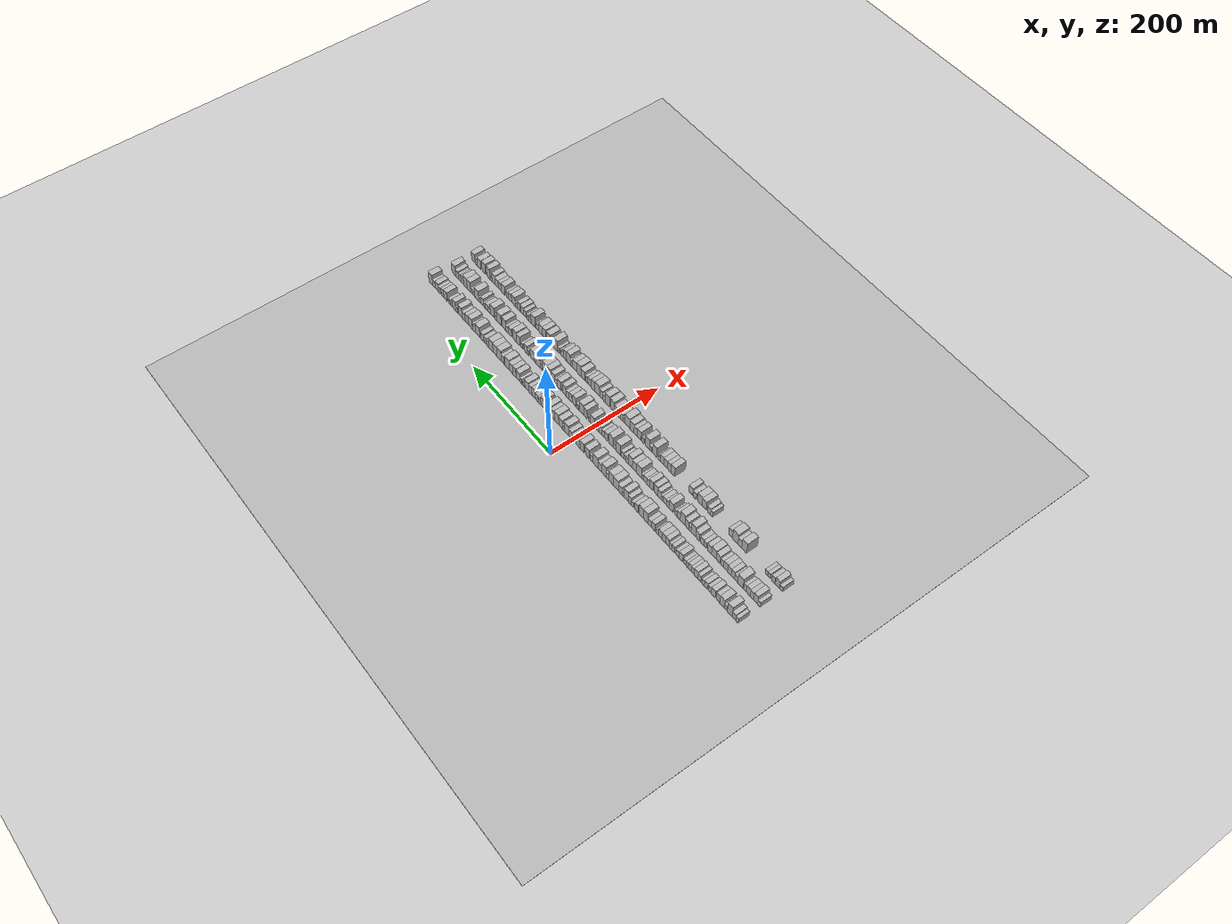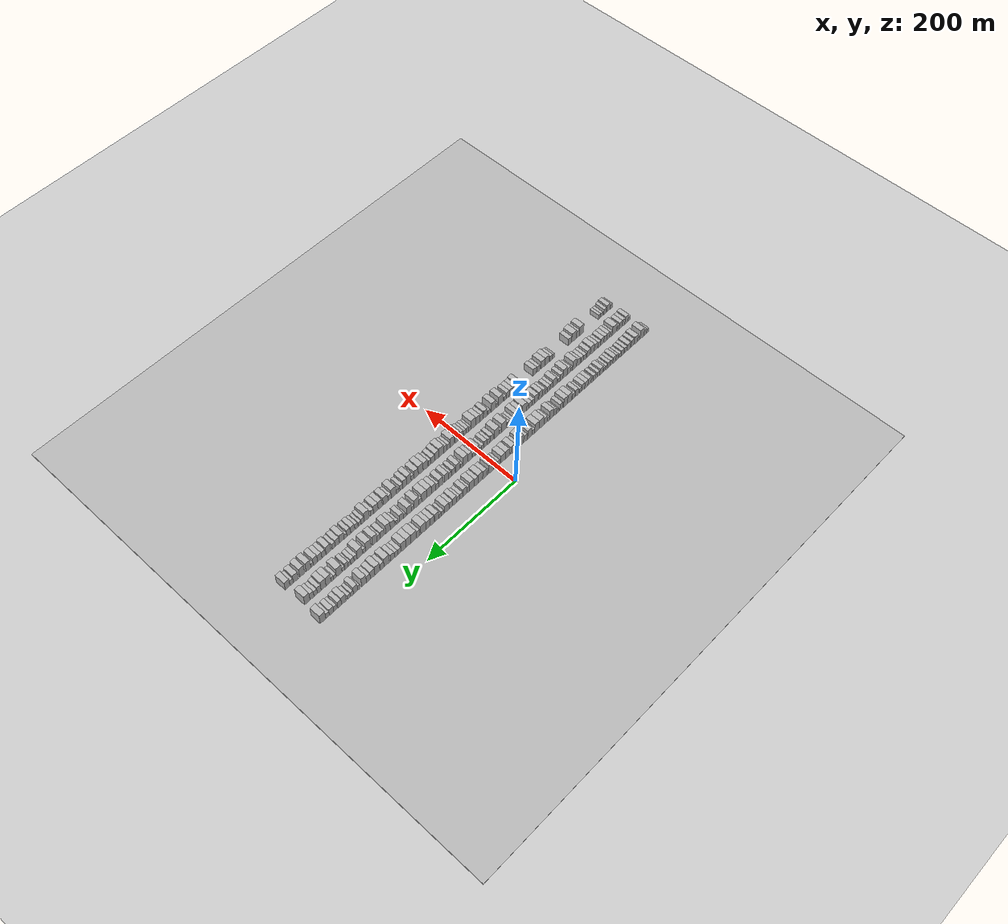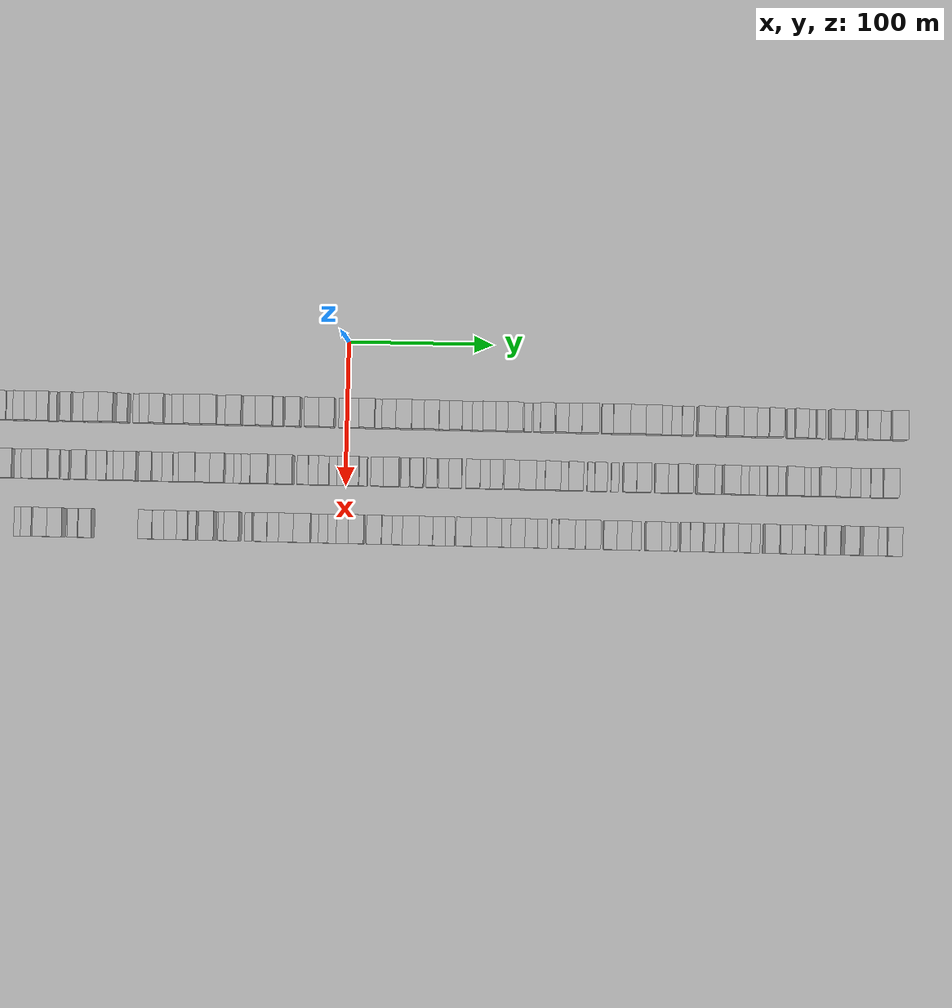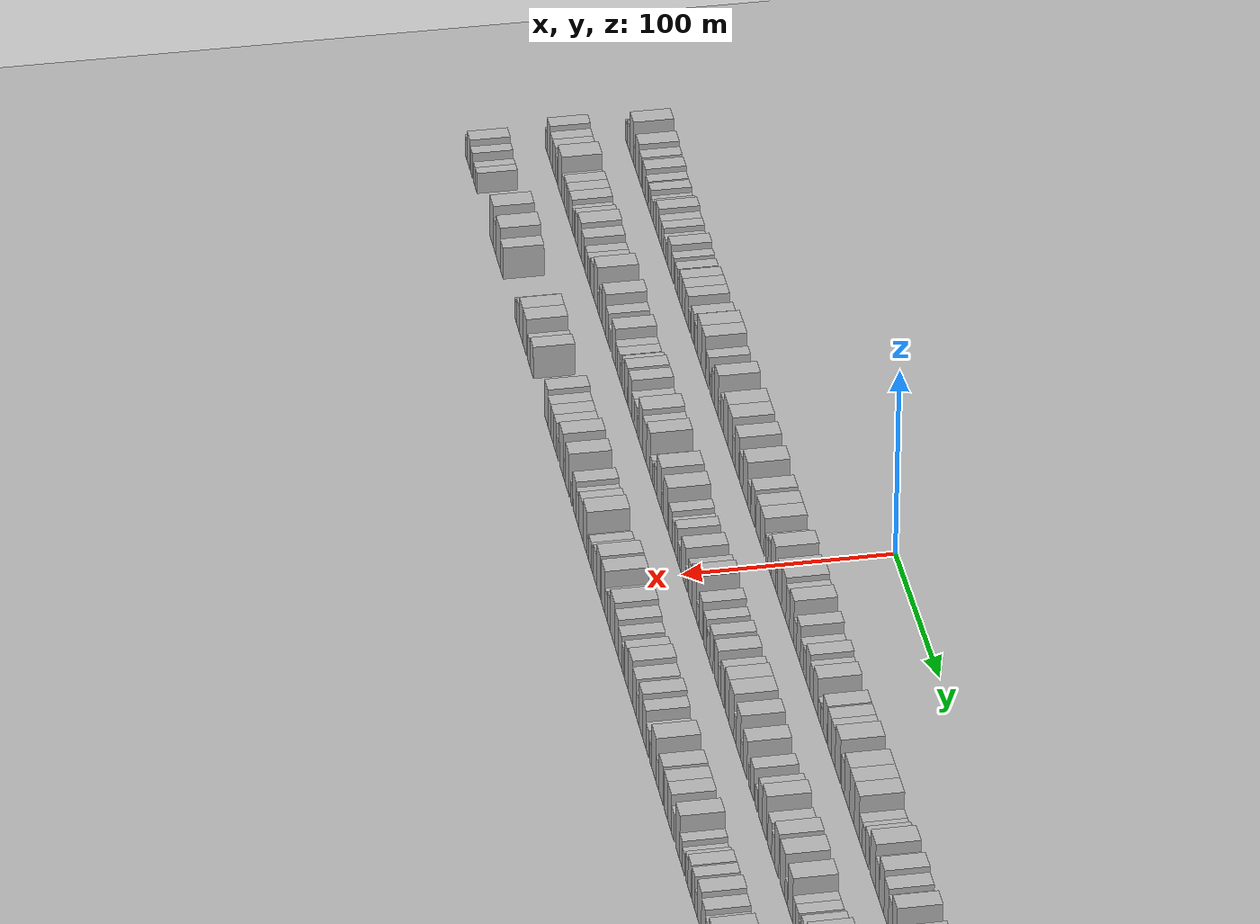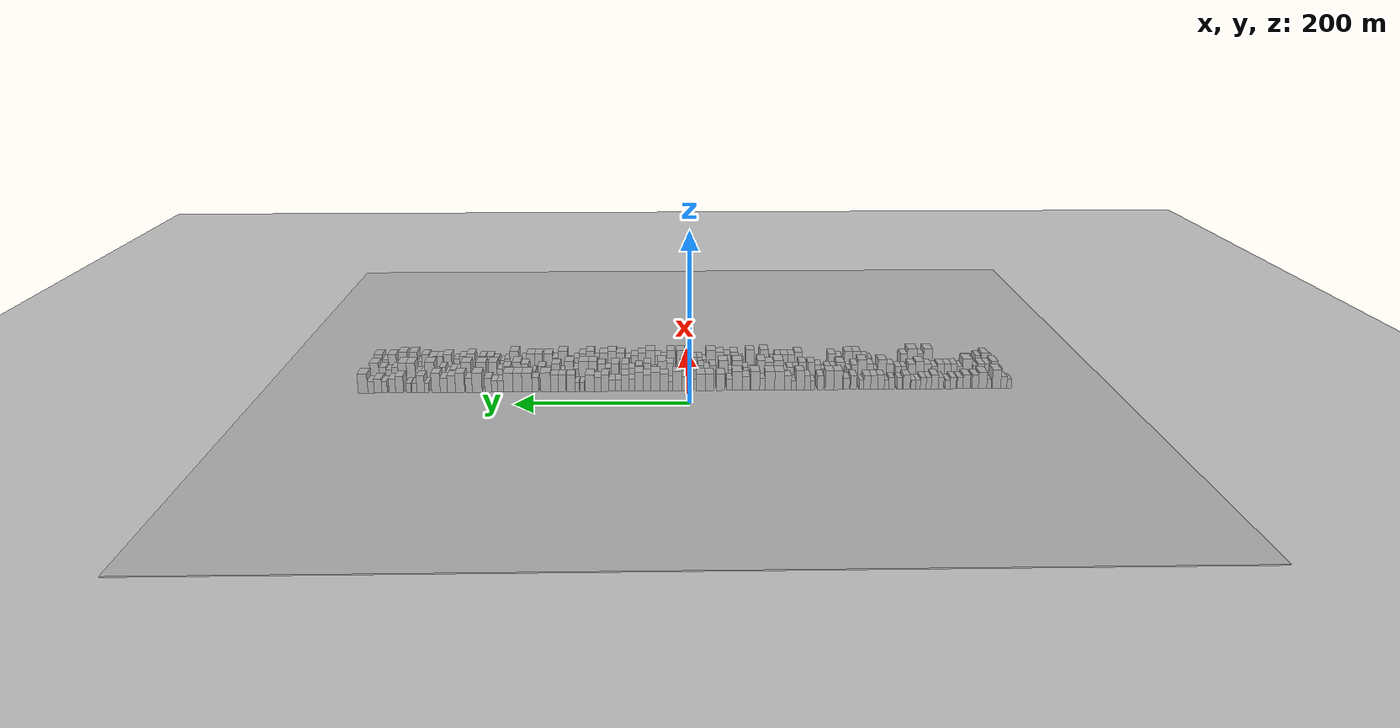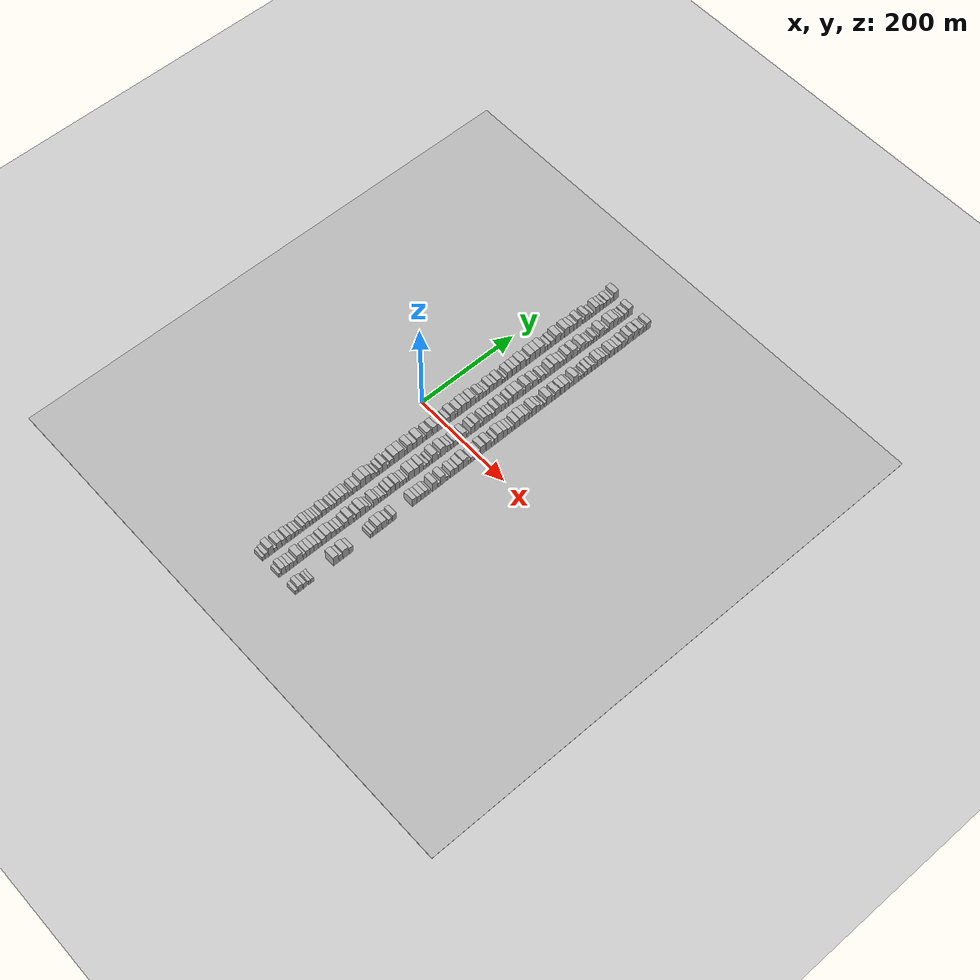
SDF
<?xml version="1.0" encoding="utf-8"?>

<sdf version="1.6">

   <world name="default">

      <gui fullscreen="0">

         <camera name="user_camera">

            <pose>-15 0 4.57585 0 0 0</pose>

            <view_controller>orbit</view_controller>

         </camera>

      </gui>

      <scene>

         <sky>

           <clouds>

             <speed>12</speed>

           </clouds>

         </sky>

         <ambient>0.4 0.4 0.4 1</ambient>

         <background>0.7 0.7 0.7 1</background>

         <shadows>1</shadows>

      </scene>

      <gravity>0 0 -9.8066</gravity>

      <magnetic_field>6e-06 2.3e-05 -4.2e-05</magnetic_field>

      <physics default="0" name="default_physics" type="ode">

         <ode>

            <solver>

               <type>quick</type>

               <iters>10</iters>

               <sor>1.0</sor>

               <use_dynamic_moi_rescaling>0</use_dynamic_moi_rescaling>

            </solver>

            <constraints>

               <cfm>0</cfm>

               <erp>0.2</erp>

               <contact_max_correcting_vel>100</contact_max_correcting_vel>

               <contact_surface_layer>0.001</contact_surface_layer>

            </constraints>

         </ode>

         <max_step_size>0.004</max_step_size>

         <real_time_factor>1</real_time_factor>

         <real_time_update_rate>250</real_time_update_rate>

      </physics>

      <light name="sun" type="directional">

         <cast_shadows>1</cast_shadows>

         <pose>0 0 10 0 0 0</pose>

         <diffuse>0.8 0.8 0.8 1</diffuse>

         <specular>0.2 0.2 0.2 1</specular>

         <attenuation>

            <range>1000</range>

            <constant>0.9</constant>

            <linear>0.01</linear>

            <quadratic>0.001</quadratic>

         </attenuation>

         <direction>-0.5 0.1 -0.9</direction>

      </light>

      <include>

         <name>ground_plane_1</name>

         <uri>model://HANNAS_ground_plane</uri>

         <pose>0 0 0  0 0 0</pose>

      </include>

      <include>

         <name>ground_plane_2</name>

         <uri>model://HANNAS_ground_plane</uri>

         <pose>100 0 0  0 0 0</pose>

      </include>

      <model name="building_1">

         <static>1</static>

         <pose frame="">50.0000 -377.2630 0 0.000000 0.000000 0.000000</pose>

         <link name="link">

            <pose frame="">0 0 6.00 0 0 0</pose>

            <collision name="collision">

               <geometry>

                  <box>

                     <size>20.0000 5.4741 12.0000</size>

                  </box>

               </geometry>

               <max_contacts>10</max_contacts>

               <surface>

                  <contact>

                     <ode/>

                  </contact>

                  <bounce/>

                  <friction>

                     <torsional>

                        <ode/>

                     </torsional>

                     <ode/>

                  </friction>

               </surface>

            </collision>

            <visual name="visual">

               <cast_shadows>0</cast_shadows>

               <geometry>

                  <box>

                     <size>20.0000 5.4741 12.0000</size>

                  </box>

               </geometry>

               <material>

                  <script>

                     <uri>model://HANNAS_wall/materials/scripts</uri>

                     <uri>model://HANNAS_wall/materials/textures</uri>

                     <name>vrc/HANNAS_wall</name>

                  </script>

               </material>

            </visual>

            <self_collide>0</self_collide>

            <enable_wind>0</enable_wind>

            <kinematic>0</kinematic>

         </link>

      </model>

      <model name="building_2">

         <static>1</static>

         <pose frame="">50.0000 -370.8622 0 0.000000 0.000000 0.000000</pose>

         <link name="link">

            <pose frame="">0 0 7.50 0 0 0</pose>

            <collision name="collision">

               <geometry>

                  <box>

                     <size>20.0000 7.3275 15.0000</size>

                  </box>

               </geometry>

               <max_contacts>10</max_contacts>

               <surface>

                  <contact>

                     <ode/>

                  </contact>

                  <bounce/>

                  <friction>

                     <torsional>

                        <ode/>

                     </torsional>

                     <ode/>

                  </friction>

               </surface>

            </collision>

            <visual name="visual">

               <cast_shadows>0</cast_shadows>

               <geometry>

                  <box>

                     <size>20.0000 7.3275 15.0000</size>

                  </box>

               </geometry>

               <material>

                  <script>

                     <uri>model://HANNAS_wall/materials/scripts</uri>

                     <uri>model://HANNAS_wall/materials/textures</uri>

                     <name>vrc/HANNAS_wall</name>

                  </script>

               </material>

            </visual>

            <self_collide>0</self_collide>

            <enable_wind>0</enable_wind>

            <kinematic>0</kinematic>

         </link>

      </model>

      <model name="building_3">

         <static>1</static>

         <pose frame="">50.0000 -362.1280 0 0.000000 0.000000 0.000000</pose>

         <link name="link">

            <pose frame="">0 0 12.00 0 0 0</pose>

            <collision name="collision">

               <geometry>

                  <box>

                     <size>20.0000 10.1409 24.0000</size>

                  </box>

               </geometry>

               <max_contacts>10</max_contacts>

               <surface>

                  <contact>

                     <ode/>

                  </contact>

                  <bounce/>

                  <friction>

                     <torsional>

                        <ode/>

                     </torsional>

                     <ode/>

                  </friction>

               </surface>

            </collision>

            <visual name="visual">

               <cast_shadows>0</cast_shadows>

               <geometry>

                  <box>

                     <size>20.0000 10.1409 24.0000</size>

                  </box>

               </geometry>

               <material>

                  <script>

                     <uri>model://HANNAS_wall/materials/scripts</uri>

                     <uri>model://HANNAS_wall/materials/textures</uri>

                     <name>vrc/HANNAS_wall</name>

                  </script>

               </material>

            </visual>

            <self_collide>0</self_collide>

            <enable_wind>0</enable_wind>

            <kinematic>0</kinematic>

         </link>

      </model>

      <model name="building_4">

         <static>1</static>

         <pose frame="">50.0000 -353.3951 0 0.000000 0.000000 0.000000</pose>

         <link name="link">

            <pose frame="">0 0 6.00 0 0 0</pose>

            <collision name="collision">

               <geometry>

                  <box>

                     <size>20.0000 5.3250 12.0000</size>

                  </box>

               </geometry>

               <max_contacts>10</max_contacts>

               <surface>

                  <contact>

                     <ode/>

                  </contact>

                  <bounce/>

                  <friction>

                     <torsional>

                        <ode/>

                     </torsional>

                     <ode/>

                  </friction>

               </surface>

            </collision>

            <visual name="visual">

               <cast_shadows>0</cast_shadows>

               <geometry>

                  <box>

                     <size>20.0000 5.3250 12.0000</size>

                  </box>

               </geometry>

               <material>

                  <script>

                     <uri>model://HANNAS_wall/materials/scripts</uri>

                     <uri>model://HANNAS_wall/materials/textures</uri>

                     <name>vrc/HANNAS_wall</name>

                  </script>

               </material>

            </visual>

            <self_collide>0</self_collide>

            <enable_wind>0</enable_wind>

            <kinematic>0</kinematic>

         </link>

      </model>

      <model name="building_5">

         <static>1</static>

         <pose frame="">50.0000 -345.7569 0 0.000000 0.000000 0.000000</pose>

         <link name="link">

            <pose frame="">0 0 10.50 0 0 0</pose>

            <collision name="collision">

               <geometry>

                  <box>

                     <size>20.0000 9.9514 21.0000</size>

                  </box>

               </geometry>

               <max_contacts>10</max_contacts>

               <surface>

                  <contact>

                     <ode/>

                  </contact>

                  <bounce/>

                  <friction>

                     <torsional>

                        <ode/>

                     </torsional>

                     <ode/>

                  </friction>

               </surface>

            </collision>

            <visual name="visual">

               <cast_shadows>0</cast_shadows>

               <geometry>

                  <box>

                     <size>20.0000 9.9514 21.0000</size>

                  </box>

               </geometry>

               <material>

                  <script>

                     <uri>model://HANNAS_wall/materials/scripts</uri>

                     <uri>model://HANNAS_wall/materials/textures</uri>

                     <name>vrc/HANNAS_wall</name>

                  </script>

               </material>

            </visual>

            <self_collide>0</self_collide>

            <enable_wind>0</enable_wind>

            <kinematic>0</kinematic>

         </link>

      </model>

      <model name="building_6">

         <static>1</static>

         <pose frame="">50.0000 -336.9452 0 0.000000 0.000000 0.000000</pose>

         <link name="link">

            <pose frame="">0 0 9.00 0 0 0</pose>

            <collision name="collision">

               <geometry>

                  <box>

                     <size>20.0000 7.6719 18.0000</size>

                  </box>

               </geometry>

               <max_contacts>10</max_contacts>

               <surface>

                  <contact>

                     <ode/>

                  </contact>

                  <bounce/>

                  <friction>

                     <torsional>

                        <ode/>

                     </torsional>

                     <ode/>

                  </friction>

               </surface>

            </collision>

            <visual name="visual">

               <cast_shadows>0</cast_shadows>

               <geometry>

                  <box>

                     <size>20.0000 7.6719 18.0000</size>

                  </box>

               </geometry>

               <material>

                  <script>

                     <uri>model://HANNAS_wall/materials/scripts</uri>

                     <uri>model://HANNAS_wall/materials/textures</uri>

                     <name>vrc/HANNAS_wall</name>

                  </script>

               </material>

            </visual>

            <self_collide>0</self_collide>

            <enable_wind>0</enable_wind>

            <kinematic>0</kinematic>

         </link>

      </model>

      <model name="building_7">

         <static>1</static>

         <pose frame="">50.0000 -326.7164 0 0.000000 0.000000 0.000000</pose>

         <link name="link">

            <pose frame="">0 0 9.00 0 0 0</pose>

            <collision name="collision">

               <geometry>

                  <box>

                     <size>20.0000 8.7857 18.0000</size>

                  </box>

               </geometry>

               <max_contacts>10</max_contacts>

               <surface>

                  <contact>

                     <ode/>

                  </contact>

                  <bounce/>

                  <friction>

                     <torsional>

                        <ode/>

                     </torsional>

                     <ode/>

                  </friction>

               </surface>

            </collision>

            <visual name="visual">

               <cast_shadows>0</cast_shadows>

               <geometry>

                  <box>

                     <size>20.0000 8.7857 18.0000</size>

                  </box>

               </geometry>

               <material>

                  <script>

                     <uri>model://HANNAS_wall/materials/scripts</uri>

                     <uri>model://HANNAS_wall/materials/textures</uri>

                     <name>vrc/HANNAS_wall</name>

                  </script>

               </material>

            </visual>

            <self_collide>0</self_collide>

            <enable_wind>0</enable_wind>

            <kinematic>0</kinematic>

         </link>

      </model>

      <model name="building_8">

         <static>1</static>

         <pose frame="">50.0000 -318.9342 0 0.000000 0.000000 0.000000</pose>

         <link name="link">

            <pose frame="">0 0 7.50 0 0 0</pose>

            <collision name="collision">

               <geometry>

                  <box>

                     <size>20.0000 6.7786 15.0000</size>

                  </box>

               </geometry>

               <max_contacts>10</max_contacts>

               <surface>

                  <contact>

                     <ode/>

                  </contact>

                  <bounce/>

                  <friction>

                     <torsional>

                        <ode/>

                     </torsional>

                     <ode/>

                  </friction>

               </surface>

            </collision>

            <visual name="visual">

               <cast_shadows>0</cast_shadows>

               <geometry>

                  <box>

                     <size>20.0000 6.7786 15.0000</size>

                  </box>

               </geometry>

               <material>

                  <script>

                     <uri>model://HANNAS_wall/materials/scripts</uri>

                     <uri>model://HANNAS_wall/materials/textures</uri>

                     <name>vrc/HANNAS_wall</name>

                  </script>

               </material>

            </visual>

            <self_collide>0</self_collide>

            <enable_wind>0</enable_wind>

            <kinematic>0</kinematic>

         </link>

      </model>

      <model name="building_9">

         <static>1</static>

         <pose frame="">50.0000 -310.9785 0 0.000000 0.000000 0.000000</pose>

         <link name="link">

            <pose frame="">0 0 7.50 0 0 0</pose>

            <collision name="collision">

               <geometry>

                  <box>

                     <size>20.0000 7.1328 15.0000</size>

                  </box>

               </geometry>

               <max_contacts>10</max_contacts>

               <surface>

                  <contact>

                     <ode/>

                  </contact>

                  <bounce/>

                  <friction>

                     <torsional>

                        <ode/>

                     </torsional>

                     <ode/>

                  </friction>

               </surface>

            </collision>

            <visual name="visual">

               <cast_shadows>0</cast_shadows>

               <geometry>

                  <box>

                     <size>20.0000 7.1328 15.0000</size>

                  </box>

               </geometry>

               <material>

                  <script>

                     <uri>model://HANNAS_wall/materials/scripts</uri>

                     <uri>model://HANNAS_wall/materials/textures</uri>

                     <name>vrc/HANNAS_wall</name>

                  </script>

               </material>

            </visual>

            <self_collide>0</self_collide>

            <enable_wind>0</enable_wind>

            <kinematic>0</kinematic>

         </link>

      </model>

      <model name="building_10">

         <static>1</static>

         <pose frame="">50.0000 -304.5359 0 0.000000 0.000000 0.000000</pose>

         <link name="link">

            <pose frame="">0 0 6.00 0 0 0</pose>

            <collision name="collision">

               <geometry>

                  <box>

                     <size>20.0000 5.7526 12.0000</size>

                  </box>

               </geometry>

               <max_contacts>10</max_contacts>

               <surface>

                  <contact>

                     <ode/>

                  </contact>

                  <bounce/>

                  <friction>

                     <torsional>

                        <ode/>

                     </torsional>

                     <ode/>

                  </friction>

               </surface>

            </collision>

            <visual name="visual">

               <cast_shadows>0</cast_shadows>

               <geometry>

                  <box>

                     <size>20.0000 5.7526 12.0000</size>

                  </box>

               </geometry>

               <material>

                  <script>

                     <uri>model://HANNAS_wall/materials/scripts</uri>

                     <uri>model://HANNAS_wall/materials/textures</uri>

                     <name>vrc/HANNAS_wall</name>

                  </script>

               </material>

            </visual>

            <self_collide>0</self_collide>

            <enable_wind>0</enable_wind>

            <kinematic>0</kinematic>

         </link>

      </model>

      <model name="building_11">

         <static>1</static>

         <pose frame="">50.0000 -296.5135 0 0.000000 0.000000 0.000000</pose>

         <link name="link">

            <pose frame="">0 0 7.50 0 0 0</pose>

            <collision name="collision">

               <geometry>

                  <box>

                     <size>20.0000 6.2922 15.0000</size>

                  </box>

               </geometry>

               <max_contacts>10</max_contacts>

               <surface>

                  <contact>

                     <ode/>

                  </contact>

                  <bounce/>

                  <friction>

                     <torsional>

                        <ode/>

                     </torsional>

                     <ode/>

                  </friction>

               </surface>

            </collision>

            <visual name="visual">

               <cast_shadows>0</cast_shadows>

               <geometry>

                  <box>

                     <size>20.0000 6.2922 15.0000</size>

                  </box>

               </geometry>

               <material>

                  <script>

                     <uri>model://HANNAS_wall/materials/scripts</uri>

                     <uri>model://HANNAS_wall/materials/textures</uri>

                     <name>vrc/HANNAS_wall</name>

                  </script>

               </material>

            </visual>

            <self_collide>0</self_collide>

            <enable_wind>0</enable_wind>

            <kinematic>0</kinematic>

         </link>

      </model>

      <model name="building_12">

         <static>1</static>

         <pose frame="">50.0000 -289.2329 0 0.000000 0.000000 0.000000</pose>

         <link name="link">

            <pose frame="">0 0 9.00 0 0 0</pose>

            <collision name="collision">

               <geometry>

                  <box>

                     <size>20.0000 8.2688 18.0000</size>

                  </box>

               </geometry>

               <max_contacts>10</max_contacts>

               <surface>

                  <contact>

                     <ode/>

                  </contact>

                  <bounce/>

                  <friction>

                     <torsional>

                        <ode/>

                     </torsional>

                     <ode/>

                  </friction>

               </surface>

            </collision>

            <visual name="visual">

               <cast_shadows>0</cast_shadows>

               <geometry>

                  <box>

                     <size>20.0000 8.2688 18.0000</size>

                  </box>

               </geometry>

               <material>

                  <script>

                     <uri>model://HANNAS_wall/materials/scripts</uri>

                     <uri>model://HANNAS_wall/materials/textures</uri>

                     <name>vrc/HANNAS_wall</name>

                  </script>

               </material>

            </visual>

            <self_collide>0</self_collide>

            <enable_wind>0</enable_wind>

            <kinematic>0</kinematic>

         </link>

      </model>

      <model name="building_13">

         <static>1</static>

         <pose frame="">50.0000 -281.9908 0 0.000000 0.000000 0.000000</pose>

         <link name="link">

            <pose frame="">0 0 7.50 0 0 0</pose>

            <collision name="collision">

               <geometry>

                  <box>

                     <size>20.0000 6.2154 15.0000</size>

                  </box>

               </geometry>

               <max_contacts>10</max_contacts>

               <surface>

                  <contact>

                     <ode/>

                  </contact>

                  <bounce/>

                  <friction>

                     <torsional>

                        <ode/>

                     </torsional>

                     <ode/>

                  </friction>

               </surface>

            </collision>

            <visual name="visual">

               <cast_shadows>0</cast_shadows>

               <geometry>

                  <box>

                     <size>20.0000 6.2154 15.0000</size>

                  </box>

               </geometry>

               <material>

                  <script>

                     <uri>model://HANNAS_wall/materials/scripts</uri>

                     <uri>model://HANNAS_wall/materials/textures</uri>

                     <name>vrc/HANNAS_wall</name>

                  </script>

               </material>

            </visual>

            <self_collide>0</self_collide>

            <enable_wind>0</enable_wind>

            <kinematic>0</kinematic>

         </link>

      </model>

      <model name="building_14">

         <static>1</static>

         <pose frame="">50.0000 -275.5094 0 0.000000 0.000000 0.000000</pose>

         <link name="link">

            <pose frame="">0 0 7.50 0 0 0</pose>

            <collision name="collision">

               <geometry>

                  <box>

                     <size>20.0000 6.7475 15.0000</size>

                  </box>

               </geometry>

               <max_contacts>10</max_contacts>

               <surface>

                  <contact>

                     <ode/>

                  </contact>

                  <bounce/>

                  <friction>

                     <torsional>

                        <ode/>

                     </torsional>

                     <ode/>

                  </friction>

               </surface>

            </collision>

            <visual name="visual">

               <cast_shadows>0</cast_shadows>

               <geometry>

                  <box>

                     <size>20.0000 6.7475 15.0000</size>

                  </box>

               </geometry>

               <material>

                  <script>

                     <uri>model://HANNAS_wall/materials/scripts</uri>

                     <uri>model://HANNAS_wall/materials/textures</uri>

                     <name>vrc/HANNAS_wall</name>

                  </script>

               </material>

            </visual>

            <self_collide>0</self_collide>

            <enable_wind>0</enable_wind>

            <kinematic>0</kinematic>

         </link>

      </model>

      <model name="building_15">

         <static>1</static>

         <pose frame="">50.0000 -269.4608 0 0.000000 0.000000 0.000000</pose>

         <link name="link">

            <pose frame="">0 0 6.00 0 0 0</pose>

            <collision name="collision">

               <geometry>

                  <box>

                     <size>20.0000 5.3496 12.0000</size>

                  </box>

               </geometry>

               <max_contacts>10</max_contacts>

               <surface>

                  <contact>

                     <ode/>

                  </contact>

                  <bounce/>

                  <friction>

                     <torsional>

                        <ode/>

                     </torsional>

                     <ode/>

                  </friction>

               </surface>

            </collision>

            <visual name="visual">

               <cast_shadows>0</cast_shadows>

               <geometry>

                  <box>

                     <size>20.0000 5.3496 12.0000</size>

                  </box>

               </geometry>

               <material>

                  <script>

                     <uri>model://HANNAS_wall/materials/scripts</uri>

                     <uri>model://HANNAS_wall/materials/textures</uri>

                     <name>vrc/HANNAS_wall</name>

                  </script>

               </material>

            </visual>

            <self_collide>0</self_collide>

            <enable_wind>0</enable_wind>

            <kinematic>0</kinematic>

         </link>

      </model>

      <model name="building_16">

         <static>1</static>

         <pose frame="">50.0000 -263.8933 0 0.000000 0.000000 0.000000</pose>

         <link name="link">

            <pose frame="">0 0 6.00 0 0 0</pose>

            <collision name="collision">

               <geometry>

                  <box>

                     <size>20.0000 5.7854 12.0000</size>

                  </box>

               </geometry>

               <max_contacts>10</max_contacts>

               <surface>

                  <contact>

                     <ode/>

                  </contact>

                  <bounce/>

                  <friction>

                     <torsional>

                        <ode/>

                     </torsional>

                     <ode/>

                  </friction>

               </surface>

            </collision>

            <visual name="visual">

               <cast_shadows>0</cast_shadows>

               <geometry>

                  <box>

                     <size>20.0000 5.7854 12.0000</size>

                  </box>

               </geometry>

               <material>

                  <script>

                     <uri>model://HANNAS_wall/materials/scripts</uri>

                     <uri>model://HANNAS_wall/materials/textures</uri>

                     <name>vrc/HANNAS_wall</name>

                  </script>

               </material>

            </visual>

            <self_collide>0</self_collide>

            <enable_wind>0</enable_wind>

            <kinematic>0</kinematic>

         </link>

      </model>

      <model name="building_17">

         <static>1</static>

         <pose frame="">50.0000 -255.8511 0 0.000000 0.000000 0.000000</pose>

         <link name="link">

            <pose frame="">0 0 9.00 0 0 0</pose>

            <collision name="collision">

               <geometry>

                  <box>

                     <size>20.0000 8.2990 18.0000</size>

                  </box>

               </geometry>

               <max_contacts>10</max_contacts>

               <surface>

                  <contact>

                     <ode/>

                  </contact>

                  <bounce/>

                  <friction>

                     <torsional>

                        <ode/>

                     </torsional>

                     <ode/>

                  </friction>

               </surface>

            </collision>

            <visual name="visual">

               <cast_shadows>0</cast_shadows>

               <geometry>

                  <box>

                     <size>20.0000 8.2990 18.0000</size>

                  </box>

               </geometry>

               <material>

                  <script>

                     <uri>model://HANNAS_wall/materials/scripts</uri>

                     <uri>model://HANNAS_wall/materials/textures</uri>

                     <name>vrc/HANNAS_wall</name>

                  </script>

               </material>

            </visual>

            <self_collide>0</self_collide>

            <enable_wind>0</enable_wind>

            <kinematic>0</kinematic>

         </link>

      </model>

      <model name="building_18">

         <static>1</static>

         <pose frame="">50.0000 -247.6414 0 0.000000 0.000000 0.000000</pose>

         <link name="link">

            <pose frame="">0 0 7.50 0 0 0</pose>

            <collision name="collision">

               <geometry>

                  <box>

                     <size>20.0000 6.1203 15.0000</size>

                  </box>

               </geometry>

               <max_contacts>10</max_contacts>

               <surface>

                  <contact>

                     <ode/>

                  </contact>

                  <bounce/>

                  <friction>

                     <torsional>

                        <ode/>

                     </torsional>

                     <ode/>

                  </friction>

               </surface>

            </collision>

            <visual name="visual">

               <cast_shadows>0</cast_shadows>

               <geometry>

                  <box>

                     <size>20.0000 6.1203 15.0000</size>

                  </box>

               </geometry>

               <material>

                  <script>

                     <uri>model://HANNAS_wall/materials/scripts</uri>

                     <uri>model://HANNAS_wall/materials/textures</uri>

                     <name>vrc/HANNAS_wall</name>

                  </script>

               </material>

            </visual>

            <self_collide>0</self_collide>

            <enable_wind>0</enable_wind>

            <kinematic>0</kinematic>

         </link>

      </model>

      <model name="building_19">

         <static>1</static>

         <pose frame="">50.0000 -238.1910 0 0.000000 0.000000 0.000000</pose>

         <link name="link">

            <pose frame="">0 0 7.50 0 0 0</pose>

            <collision name="collision">

               <geometry>

                  <box>

                     <size>20.0000 6.7805 15.0000</size>

                  </box>

               </geometry>

               <max_contacts>10</max_contacts>

               <surface>

                  <contact>

                     <ode/>

                  </contact>

                  <bounce/>

                  <friction>

                     <torsional>

                        <ode/>

                     </torsional>

                     <ode/>

                  </friction>

               </surface>

            </collision>

            <visual name="visual">

               <cast_shadows>0</cast_shadows>

               <geometry>

                  <box>

                     <size>20.0000 6.7805 15.0000</size>

                  </box>

               </geometry>

               <material>

                  <script>

                     <uri>model://HANNAS_wall/materials/scripts</uri>

                     <uri>model://HANNAS_wall/materials/textures</uri>

                     <name>vrc/HANNAS_wall</name>

                  </script>

               </material>

            </visual>

            <self_collide>0</self_collide>

            <enable_wind>0</enable_wind>

            <kinematic>0</kinematic>

         </link>

      </model>

      <model name="building_20">

         <static>1</static>

         <pose frame="">50.0000 -232.1118 0 0.000000 0.000000 0.000000</pose>

         <link name="link">

            <pose frame="">0 0 6.00 0 0 0</pose>

            <collision name="collision">

               <geometry>

                  <box>

                     <size>20.0000 5.3778 12.0000</size>

                  </box>

               </geometry>

               <max_contacts>10</max_contacts>

               <surface>

                  <contact>

                     <ode/>

                  </contact>

                  <bounce/>

                  <friction>

                     <torsional>

                        <ode/>

                     </torsional>

                     <ode/>

                  </friction>

               </surface>

            </collision>

            <visual name="visual">

               <cast_shadows>0</cast_shadows>

               <geometry>

                  <box>

                     <size>20.0000 5.3778 12.0000</size>

                  </box>

               </geometry>

               <material>

                  <script>

                     <uri>model://HANNAS_wall/materials/scripts</uri>

                     <uri>model://HANNAS_wall/materials/textures</uri>

                     <name>vrc/HANNAS_wall</name>

                  </script>

               </material>

            </visual>

            <self_collide>0</self_collide>

            <enable_wind>0</enable_wind>

            <kinematic>0</kinematic>

         </link>

      </model>

      <model name="building_21">

         <static>1</static>

         <pose frame="">50.0000 -225.5577 0 0.000000 0.000000 0.000000</pose>

         <link name="link">

            <pose frame="">0 0 9.00 0 0 0</pose>

            <collision name="collision">

               <geometry>

                  <box>

                     <size>20.0000 7.7305 18.0000</size>

                  </box>

               </geometry>

               <max_contacts>10</max_contacts>

               <surface>

                  <contact>

                     <ode/>

                  </contact>

                  <bounce/>

                  <friction>

                     <torsional>

                        <ode/>

                     </torsional>

                     <ode/>

                  </friction>

               </surface>

            </collision>

            <visual name="visual">

               <cast_shadows>0</cast_shadows>

               <geometry>

                  <box>

                     <size>20.0000 7.7305 18.0000</size>

                  </box>

               </geometry>

               <material>

                  <script>

                     <uri>model://HANNAS_wall/materials/scripts</uri>

                     <uri>model://HANNAS_wall/materials/textures</uri>

                     <name>vrc/HANNAS_wall</name>

                  </script>

               </material>

            </visual>

            <self_collide>0</self_collide>

            <enable_wind>0</enable_wind>

            <kinematic>0</kinematic>

         </link>

      </model>

      <model name="building_22">

         <static>1</static>

         <pose frame="">50.0000 -217.5257 0 0.000000 0.000000 0.000000</pose>

         <link name="link">

            <pose frame="">0 0 9.00 0 0 0</pose>

            <collision name="collision">

               <geometry>

                  <box>

                     <size>20.0000 8.3334 18.0000</size>

                  </box>

               </geometry>

               <max_contacts>10</max_contacts>

               <surface>

                  <contact>

                     <ode/>

                  </contact>

                  <bounce/>

                  <friction>

                     <torsional>

                        <ode/>

                     </torsional>

                     <ode/>

                  </friction>

               </surface>

            </collision>

            <visual name="visual">

               <cast_shadows>0</cast_shadows>

               <geometry>

                  <box>

                     <size>20.0000 8.3334 18.0000</size>

                  </box>

               </geometry>

               <material>

                  <script>

                     <uri>model://HANNAS_wall/materials/scripts</uri>

                     <uri>model://HANNAS_wall/materials/textures</uri>

                     <name>vrc/HANNAS_wall</name>

                  </script>

               </material>

            </visual>

            <self_collide>0</self_collide>

            <enable_wind>0</enable_wind>

            <kinematic>0</kinematic>

         </link>

      </model>

      <model name="building_23">

         <static>1</static>

         <pose frame="">50.0000 -209.2776 0 0.000000 0.000000 0.000000</pose>

         <link name="link">

            <pose frame="">0 0 9.00 0 0 0</pose>

            <collision name="collision">

               <geometry>

                  <box>

                     <size>20.0000 8.1629 18.0000</size>

                  </box>

               </geometry>

               <max_contacts>10</max_contacts>

               <surface>

                  <contact>

                     <ode/>

                  </contact>

                  <bounce/>

                  <friction>

                     <torsional>

                        <ode/>

                     </torsional>

                     <ode/>

                  </friction>

               </surface>

            </collision>

            <visual name="visual">

               <cast_shadows>0</cast_shadows>

               <geometry>

                  <box>

                     <size>20.0000 8.1629 18.0000</size>

                  </box>

               </geometry>

               <material>

                  <script>

                     <uri>model://HANNAS_wall/materials/scripts</uri>

                     <uri>model://HANNAS_wall/materials/textures</uri>

                     <name>vrc/HANNAS_wall</name>

                  </script>

               </material>

            </visual>

            <self_collide>0</self_collide>

            <enable_wind>0</enable_wind>

            <kinematic>0</kinematic>

         </link>

      </model>

      <model name="building_24">

         <static>1</static>

         <pose frame="">50.0000 -202.6628 0 0.000000 0.000000 0.000000</pose>

         <link name="link">

            <pose frame="">0 0 6.00 0 0 0</pose>

            <collision name="collision">

               <geometry>

                  <box>

                     <size>20.0000 5.0667 12.0000</size>

                  </box>

               </geometry>

               <max_contacts>10</max_contacts>

               <surface>

                  <contact>

                     <ode/>

                  </contact>

                  <bounce/>

                  <friction>

                     <torsional>

                        <ode/>

                     </torsional>

                     <ode/>

                  </friction>

               </surface>

            </collision>

            <visual name="visual">

               <cast_shadows>0</cast_shadows>

               <geometry>

                  <box>

                     <size>20.0000 5.0667 12.0000</size>

                  </box>

               </geometry>

               <material>

                  <script>

                     <uri>model://HANNAS_wall/materials/scripts</uri>

                     <uri>model://HANNAS_wall/materials/textures</uri>

                     <name>vrc/HANNAS_wall</name>

                  </script>

               </material>

            </visual>

            <self_collide>0</self_collide>

            <enable_wind>0</enable_wind>

            <kinematic>0</kinematic>

         </link>

      </model>

      <model name="building_25">

         <static>1</static>

         <pose frame="">50.0000 -193.3806 0 0.000000 0.000000 0.000000</pose>

         <link name="link">

            <pose frame="">0 0 9.00 0 0 0</pose>

            <collision name="collision">

               <geometry>

                  <box>

                     <size>20.0000 7.4976 18.0000</size>

                  </box>

               </geometry>

               <max_contacts>10</max_contacts>

               <surface>

                  <contact>

                     <ode/>

                  </contact>

                  <bounce/>

                  <friction>

                     <torsional>

                        <ode/>

                     </torsional>

                     <ode/>

                  </friction>

               </surface>

            </collision>

            <visual name="visual">

               <cast_shadows>0</cast_shadows>

               <geometry>

                  <box>

                     <size>20.0000 7.4976 18.0000</size>

                  </box>

               </geometry>

               <material>

                  <script>

                     <uri>model://HANNAS_wall/materials/scripts</uri>

                     <uri>model://HANNAS_wall/materials/textures</uri>

                     <name>vrc/HANNAS_wall</name>

                  </script>

               </material>

            </visual>

            <self_collide>0</self_collide>

            <enable_wind>0</enable_wind>

            <kinematic>0</kinematic>

         </link>

      </model>

      <model name="building_26">

         <static>1</static>

         <pose frame="">50.0000 -184.9267 0 0.000000 0.000000 0.000000</pose>

         <link name="link">

            <pose frame="">0 0 7.50 0 0 0</pose>

            <collision name="collision">

               <geometry>

                  <box>

                     <size>20.0000 7.4101 15.0000</size>

                  </box>

               </geometry>

               <max_contacts>10</max_contacts>

               <surface>

                  <contact>

                     <ode/>

                  </contact>

                  <bounce/>

                  <friction>

                     <torsional>

                        <ode/>

                     </torsional>

                     <ode/>

                  </friction>

               </surface>

            </collision>

            <visual name="visual">

               <cast_shadows>0</cast_shadows>

               <geometry>

                  <box>

                     <size>20.0000 7.4101 15.0000</size>

                  </box>

               </geometry>

               <material>

                  <script>

                     <uri>model://HANNAS_wall/materials/scripts</uri>

                     <uri>model://HANNAS_wall/materials/textures</uri>

                     <name>vrc/HANNAS_wall</name>

                  </script>

               </material>

            </visual>

            <self_collide>0</self_collide>

            <enable_wind>0</enable_wind>

            <kinematic>0</kinematic>

         </link>

      </model>

      <model name="building_27">

         <static>1</static>

         <pose frame="">50.0000 -175.0752 0 0.000000 0.000000 0.000000</pose>

         <link name="link">

            <pose frame="">0 0 12.00 0 0 0</pose>

            <collision name="collision">

               <geometry>

                  <box>

                     <size>20.0000 10.2930 24.0000</size>

                  </box>

               </geometry>

               <max_contacts>10</max_contacts>

               <surface>

                  <contact>

                     <ode/>

                  </contact>

                  <bounce/>

                  <friction>

                     <torsional>

                        <ode/>

                     </torsional>

                     <ode/>

                  </friction>

               </surface>

            </collision>

            <visual name="visual">

               <cast_shadows>0</cast_shadows>

               <geometry>

                  <box>

                     <size>20.0000 10.2930 24.0000</size>

                  </box>

               </geometry>

               <material>

                  <script>

                     <uri>model://HANNAS_wall/materials/scripts</uri>

                     <uri>model://HANNAS_wall/materials/textures</uri>

                     <name>vrc/HANNAS_wall</name>

                  </script>

               </material>

            </visual>

            <self_collide>0</self_collide>

            <enable_wind>0</enable_wind>

            <kinematic>0</kinematic>

         </link>

      </model>

      <model name="building_28">

         <static>1</static>

         <pose frame="">50.0000 -164.9547 0 0.000000 0.000000 0.000000</pose>

         <link name="link">

            <pose frame="">0 0 12.00 0 0 0</pose>

            <collision name="collision">

               <geometry>

                  <box>

                     <size>20.0000 9.9480 24.0000</size>

                  </box>

               </geometry>

               <max_contacts>10</max_contacts>

               <surface>

                  <contact>

                     <ode/>

                  </contact>

                  <bounce/>

                  <friction>

                     <torsional>

                        <ode/>

                     </torsional>

                     <ode/>

                  </friction>

               </surface>

            </collision>

            <visual name="visual">

               <cast_shadows>0</cast_shadows>

               <geometry>

                  <box>

                     <size>20.0000 9.9480 24.0000</size>

                  </box>

               </geometry>

               <material>

                  <script>

                     <uri>model://HANNAS_wall/materials/scripts</uri>

                     <uri>model://HANNAS_wall/materials/textures</uri>

                     <name>vrc/HANNAS_wall</name>

                  </script>

               </material>

            </visual>

            <self_collide>0</self_collide>

            <enable_wind>0</enable_wind>

            <kinematic>0</kinematic>

         </link>

      </model>

      <model name="building_29">

         <static>1</static>

         <pose frame="">50.0000 -154.3123 0 0.000000 0.000000 0.000000</pose>

         <link name="link">

            <pose frame="">0 0 9.00 0 0 0</pose>

            <collision name="collision">

               <geometry>

                  <box>

                     <size>20.0000 7.3368 18.0000</size>

                  </box>

               </geometry>

               <max_contacts>10</max_contacts>

               <surface>

                  <contact>

                     <ode/>

                  </contact>

                  <bounce/>

                  <friction>

                     <torsional>

                        <ode/>

                     </torsional>

                     <ode/>

                  </friction>

               </surface>

            </collision>

            <visual name="visual">

               <cast_shadows>0</cast_shadows>

               <geometry>

                  <box>

                     <size>20.0000 7.3368 18.0000</size>

                  </box>

               </geometry>

               <material>

                  <script>

                     <uri>model://HANNAS_wall/materials/scripts</uri>

                     <uri>model://HANNAS_wall/materials/textures</uri>

                     <name>vrc/HANNAS_wall</name>

                  </script>

               </material>

            </visual>

            <self_collide>0</self_collide>

            <enable_wind>0</enable_wind>

            <kinematic>0</kinematic>

         </link>

      </model>

      <model name="building_30">

         <static>1</static>

         <pose frame="">50.0000 -145.0595 0 0.000000 0.000000 0.000000</pose>

         <link name="link">

            <pose frame="">0 0 6.00 0 0 0</pose>

            <collision name="collision">

               <geometry>

                  <box>

                     <size>20.0000 5.1688 12.0000</size>

                  </box>

               </geometry>

               <max_contacts>10</max_contacts>

               <surface>

                  <contact>

                     <ode/>

                  </contact>

                  <bounce/>

                  <friction>

                     <torsional>

                        <ode/>

                     </torsional>

                     <ode/>

                  </friction>

               </surface>

            </collision>

            <visual name="visual">

               <cast_shadows>0</cast_shadows>

               <geometry>

                  <box>

                     <size>20.0000 5.1688 12.0000</size>

                  </box>

               </geometry>

               <material>

                  <script>

                     <uri>model://HANNAS_wall/materials/scripts</uri>

                     <uri>model://HANNAS_wall/materials/textures</uri>

                     <name>vrc/HANNAS_wall</name>

                  </script>

               </material>

            </visual>

            <self_collide>0</self_collide>

            <enable_wind>0</enable_wind>

            <kinematic>0</kinematic>

         </link>

      </model>

      <model name="building_31">

         <static>1</static>

         <pose frame="">50.0000 -138.8171 0 0.000000 0.000000 0.000000</pose>

         <link name="link">

            <pose frame="">0 0 9.00 0 0 0</pose>

            <collision name="collision">

               <geometry>

                  <box>

                     <size>20.0000 7.3159 18.0000</size>

                  </box>

               </geometry>

               <max_contacts>10</max_contacts>

               <surface>

                  <contact>

                     <ode/>

                  </contact>

                  <bounce/>

                  <friction>

                     <torsional>

                        <ode/>

                     </torsional>

                     <ode/>

                  </friction>

               </surface>

            </collision>

            <visual name="visual">

               <cast_shadows>0</cast_shadows>

               <geometry>

                  <box>

                     <size>20.0000 7.3159 18.0000</size>

                  </box>

               </geometry>

               <material>

                  <script>

                     <uri>model://HANNAS_wall/materials/scripts</uri>

                     <uri>model://HANNAS_wall/materials/textures</uri>

                     <name>vrc/HANNAS_wall</name>

                  </script>

               </material>

            </visual>

            <self_collide>0</self_collide>

            <enable_wind>0</enable_wind>

            <kinematic>0</kinematic>

         </link>

      </model>

      <model name="building_32">

         <static>1</static>

         <pose frame="">50.0000 -130.2730 0 0.000000 0.000000 0.000000</pose>

         <link name="link">

            <pose frame="">0 0 12.00 0 0 0</pose>

            <collision name="collision">

               <geometry>

                  <box>

                     <size>20.0000 9.7723 24.0000</size>

                  </box>

               </geometry>

               <max_contacts>10</max_contacts>

               <surface>

                  <contact>

                     <ode/>

                  </contact>

                  <bounce/>

                  <friction>

                     <torsional>

                        <ode/>

                     </torsional>

                     <ode/>

                  </friction>

               </surface>

            </collision>

            <visual name="visual">

               <cast_shadows>0</cast_shadows>

               <geometry>

                  <box>

                     <size>20.0000 9.7723 24.0000</size>

                  </box>

               </geometry>

               <material>

                  <script>

                     <uri>model://HANNAS_wall/materials/scripts</uri>

                     <uri>model://HANNAS_wall/materials/textures</uri>

                     <name>vrc/HANNAS_wall</name>

                  </script>

               </material>

            </visual>

            <self_collide>0</self_collide>

            <enable_wind>0</enable_wind>

            <kinematic>0</kinematic>

         </link>

      </model>

      <model name="building_33">

         <static>1</static>

         <pose frame="">50.0000 -122.7039 0 0.000000 0.000000 0.000000</pose>

         <link name="link">

            <pose frame="">0 0 6.00 0 0 0</pose>

            <collision name="collision">

               <geometry>

                  <box>

                     <size>20.0000 5.3659 12.0000</size>

                  </box>

               </geometry>

               <max_contacts>10</max_contacts>

               <surface>

                  <contact>

                     <ode/>

                  </contact>

                  <bounce/>

                  <friction>

                     <torsional>

                        <ode/>

                     </torsional>

                     <ode/>

                  </friction>

               </surface>

            </collision>

            <visual name="visual">

               <cast_shadows>0</cast_shadows>

               <geometry>

                  <box>

                     <size>20.0000 5.3659 12.0000</size>

                  </box>

               </geometry>

               <material>

                  <script>

                     <uri>model://HANNAS_wall/materials/scripts</uri>

                     <uri>model://HANNAS_wall/materials/textures</uri>

                     <name>vrc/HANNAS_wall</name>

                  </script>

               </material>

            </visual>

            <self_collide>0</self_collide>

            <enable_wind>0</enable_wind>

            <kinematic>0</kinematic>

         </link>

      </model>

      <model name="building_34">

         <static>1</static>

         <pose frame="">50.0000 -115.7547 0 0.000000 0.000000 0.000000</pose>

         <link name="link">

            <pose frame="">0 0 9.00 0 0 0</pose>

            <collision name="collision">

               <geometry>

                  <box>

                     <size>20.0000 8.5325 18.0000</size>

                  </box>

               </geometry>

               <max_contacts>10</max_contacts>

               <surface>

                  <contact>

                     <ode/>

                  </contact>

                  <bounce/>

                  <friction>

                     <torsional>

                        <ode/>

                     </torsional>

                     <ode/>

                  </friction>

               </surface>

            </collision>

            <visual name="visual">

               <cast_shadows>0</cast_shadows>

               <geometry>

                  <box>

                     <size>20.0000 8.5325 18.0000</size>

                  </box>

               </geometry>

               <material>

                  <script>

                     <uri>model://HANNAS_wall/materials/scripts</uri>

                     <uri>model://HANNAS_wall/materials/textures</uri>

                     <name>vrc/HANNAS_wall</name>

                  </script>

               </material>

            </visual>

            <self_collide>0</self_collide>

            <enable_wind>0</enable_wind>

            <kinematic>0</kinematic>

         </link>

      </model>

      <model name="building_35">

         <static>1</static>

         <pose frame="">50.0000 -105.9031 0 0.000000 0.000000 0.000000</pose>

         <link name="link">

            <pose frame="">0 0 12.00 0 0 0</pose>

            <collision name="collision">

               <geometry>

                  <box>

                     <size>20.0000 11.1709 24.0000</size>

                  </box>

               </geometry>

               <max_contacts>10</max_contacts>

               <surface>

                  <contact>

                     <ode/>

                  </contact>

                  <bounce/>

                  <friction>

                     <torsional>

                        <ode/>

                     </torsional>

                     <ode/>

                  </friction>

               </surface>

            </collision>

            <visual name="visual">

               <cast_shadows>0</cast_shadows>

               <geometry>

                  <box>

                     <size>20.0000 11.1709 24.0000</size>

                  </box>

               </geometry>

               <material>

                  <script>

                     <uri>model://HANNAS_wall/materials/scripts</uri>

                     <uri>model://HANNAS_wall/materials/textures</uri>

                     <name>vrc/HANNAS_wall</name>

                  </script>

               </material>

            </visual>

            <self_collide>0</self_collide>

            <enable_wind>0</enable_wind>

            <kinematic>0</kinematic>

         </link>

      </model>

      <model name="building_36">

         <static>1</static>

         <pose frame="">50.0000 -94.6707 0 0.000000 0.000000 0.000000</pose>

         <link name="link">

            <pose frame="">0 0 12.00 0 0 0</pose>

            <collision name="collision">

               <geometry>

                  <box>

                     <size>20.0000 11.2938 24.0000</size>

                  </box>

               </geometry>

               <max_contacts>10</max_contacts>

               <surface>

                  <contact>

                     <ode/>

                  </contact>

                  <bounce/>

                  <friction>

                     <torsional>

                        <ode/>

                     </torsional>

                     <ode/>

                  </friction>

               </surface>

            </collision>

            <visual name="visual">

               <cast_shadows>0</cast_shadows>

               <geometry>

                  <box>

                     <size>20.0000 11.2938 24.0000</size>

                  </box>

               </geometry>

               <material>

                  <script>

                     <uri>model://HANNAS_wall/materials/scripts</uri>

                     <uri>model://HANNAS_wall/materials/textures</uri>

                     <name>vrc/HANNAS_wall</name>

                  </script>

               </material>

            </visual>

            <self_collide>0</self_collide>

            <enable_wind>0</enable_wind>

            <kinematic>0</kinematic>

         </link>

      </model>

      <model name="building_37">

         <static>1</static>

         <pose frame="">50.0000 -85.8320 0 0.000000 0.000000 0.000000</pose>

         <link name="link">

            <pose frame="">0 0 7.50 0 0 0</pose>

            <collision name="collision">

               <geometry>

                  <box>

                     <size>20.0000 6.3835 15.0000</size>

                  </box>

               </geometry>

               <max_contacts>10</max_contacts>

               <surface>

                  <contact>

                     <ode/>

                  </contact>

                  <bounce/>

                  <friction>

                     <torsional>

                        <ode/>

                     </torsional>

                     <ode/>

                  </friction>

               </surface>

            </collision>

            <visual name="visual">

               <cast_shadows>0</cast_shadows>

               <geometry>

                  <box>

                     <size>20.0000 6.3835 15.0000</size>

                  </box>

               </geometry>

               <material>

                  <script>

                     <uri>model://HANNAS_wall/materials/scripts</uri>

                     <uri>model://HANNAS_wall/materials/textures</uri>

                     <name>vrc/HANNAS_wall</name>

                  </script>

               </material>

            </visual>

            <self_collide>0</self_collide>

            <enable_wind>0</enable_wind>

            <kinematic>0</kinematic>

         </link>

      </model>

      <model name="building_38">

         <static>1</static>

         <pose frame="">50.0000 -77.3093 0 0.000000 0.000000 0.000000</pose>

         <link name="link">

            <pose frame="">0 0 12.00 0 0 0</pose>

            <collision name="collision">

               <geometry>

                  <box>

                     <size>20.0000 10.6619 24.0000</size>

                  </box>

               </geometry>

               <max_contacts>10</max_contacts>

               <surface>

                  <contact>

                     <ode/>

                  </contact>

                  <bounce/>

                  <friction>

                     <torsional>

                        <ode/>

                     </torsional>

                     <ode/>

                  </friction>

               </surface>

            </collision>

            <visual name="visual">

               <cast_shadows>0</cast_shadows>

               <geometry>

                  <box>

                     <size>20.0000 10.6619 24.0000</size>

                  </box>

               </geometry>

               <material>

                  <script>

                     <uri>model://HANNAS_wall/materials/scripts</uri>

                     <uri>model://HANNAS_wall/materials/textures</uri>

                     <name>vrc/HANNAS_wall</name>

                  </script>

               </material>

            </visual>

            <self_collide>0</self_collide>

            <enable_wind>0</enable_wind>

            <kinematic>0</kinematic>

         </link>

      </model>

      <model name="building_39">

         <static>1</static>

         <pose frame="">50.0000 -66.5992 0 0.000000 0.000000 0.000000</pose>

         <link name="link">

            <pose frame="">0 0 9.00 0 0 0</pose>

            <collision name="collision">

               <geometry>

                  <box>

                     <size>20.0000 8.7583 18.0000</size>

                  </box>

               </geometry>

               <max_contacts>10</max_contacts>

               <surface>

                  <contact>

                     <ode/>

                  </contact>

                  <bounce/>

                  <friction>

                     <torsional>

                        <ode/>

                     </torsional>

                     <ode/>

                  </friction>

               </surface>

            </collision>

            <visual name="visual">

               <cast_shadows>0</cast_shadows>

               <geometry>

                  <box>

                     <size>20.0000 8.7583 18.0000</size>

                  </box>

               </geometry>

               <material>

                  <script>

                     <uri>model://HANNAS_wall/materials/scripts</uri>

                     <uri>model://HANNAS_wall/materials/textures</uri>

                     <name>vrc/HANNAS_wall</name>

                  </script>

               </material>

            </visual>

            <self_collide>0</self_collide>

            <enable_wind>0</enable_wind>

            <kinematic>0</kinematic>

         </link>

      </model>

      <model name="building_40">

         <static>1</static>

         <pose frame="">50.0000 -56.3737 0 0.000000 0.000000 0.000000</pose>

         <link name="link">

            <pose frame="">0 0 12.00 0 0 0</pose>

            <collision name="collision">

               <geometry>

                  <box>

                     <size>20.0000 11.6929 24.0000</size>

                  </box>

               </geometry>

               <max_contacts>10</max_contacts>

               <surface>

                  <contact>

                     <ode/>

                  </contact>

                  <bounce/>

                  <friction>

                     <torsional>

                        <ode/>

                     </torsional>

                     <ode/>

                  </friction>

               </surface>

            </collision>

            <visual name="visual">

               <cast_shadows>0</cast_shadows>

               <geometry>

                  <box>

                     <size>20.0000 11.6929 24.0000</size>

                  </box>

               </geometry>

               <material>

                  <script>

                     <uri>model://HANNAS_wall/materials/scripts</uri>

                     <uri>model://HANNAS_wall/materials/textures</uri>

                     <name>vrc/HANNAS_wall</name>

                  </script>

               </material>

            </visual>

            <self_collide>0</self_collide>

            <enable_wind>0</enable_wind>

            <kinematic>0</kinematic>

         </link>

      </model>

      <model name="building_41">

         <static>1</static>

         <pose frame="">50.0000 -47.1765 0 0.000000 0.000000 0.000000</pose>

         <link name="link">

            <pose frame="">0 0 7.50 0 0 0</pose>

            <collision name="collision">

               <geometry>

                  <box>

                     <size>20.0000 6.7015 15.0000</size>

                  </box>

               </geometry>

               <max_contacts>10</max_contacts>

               <surface>

                  <contact>

                     <ode/>

                  </contact>

                  <bounce/>

                  <friction>

                     <torsional>

                        <ode/>

                     </torsional>

                     <ode/>

                  </friction>

               </surface>

            </collision>

            <visual name="visual">

               <cast_shadows>0</cast_shadows>

               <geometry>

                  <box>

                     <size>20.0000 6.7015 15.0000</size>

                  </box>

               </geometry>

               <material>

                  <script>

                     <uri>model://HANNAS_wall/materials/scripts</uri>

                     <uri>model://HANNAS_wall/materials/textures</uri>

                     <name>vrc/HANNAS_wall</name>

                  </script>

               </material>

            </visual>

            <self_collide>0</self_collide>

            <enable_wind>0</enable_wind>

            <kinematic>0</kinematic>

         </link>

      </model>

      <model name="building_42">

         <static>1</static>

         <pose frame="">50.0000 -36.7780 0 0.000000 0.000000 0.000000</pose>

         <link name="link">

            <pose frame="">0 0 10.50 0 0 0</pose>

            <collision name="collision">

               <geometry>

                  <box>

                     <size>20.0000 10.0955 21.0000</size>

                  </box>

               </geometry>

               <max_contacts>10</max_contacts>

               <surface>

                  <contact>

                     <ode/>

                  </contact>

                  <bounce/>

                  <friction>

                     <torsional>

                        <ode/>

                     </torsional>

                     <ode/>

                  </friction>

               </surface>

            </collision>

            <visual name="visual">

               <cast_shadows>0</cast_shadows>

               <geometry>

                  <box>

                     <size>20.0000 10.0955 21.0000</size>

                  </box>

               </geometry>

               <material>

                  <script>

                     <uri>model://HANNAS_wall/materials/scripts</uri>

                     <uri>model://HANNAS_wall/materials/textures</uri>

                     <name>vrc/HANNAS_wall</name>

                  </script>

               </material>

            </visual>

            <self_collide>0</self_collide>

            <enable_wind>0</enable_wind>

            <kinematic>0</kinematic>

         </link>

      </model>

      <model name="building_43">

         <static>1</static>

         <pose frame="">50.0000 -23.6953 0 0.000000 0.000000 0.000000</pose>

         <link name="link">

            <pose frame="">0 0 10.50 0 0 0</pose>

            <collision name="collision">

               <geometry>

                  <box>

                     <size>20.0000 10.0698 21.0000</size>

                  </box>

               </geometry>

               <max_contacts>10</max_contacts>

               <surface>

                  <contact>

                     <ode/>

                  </contact>

                  <bounce/>

                  <friction>

                     <torsional>

                        <ode/>

                     </torsional>

                     <ode/>

                  </friction>

               </surface>

            </collision>

            <visual name="visual">

               <cast_shadows>0</cast_shadows>

               <geometry>

                  <box>

                     <size>20.0000 10.0698 21.0000</size>

                  </box>

               </geometry>

               <material>

                  <script>

                     <uri>model://HANNAS_wall/materials/scripts</uri>

                     <uri>model://HANNAS_wall/materials/textures</uri>

                     <name>vrc/HANNAS_wall</name>

                  </script>

               </material>

            </visual>

            <self_collide>0</self_collide>

            <enable_wind>0</enable_wind>

            <kinematic>0</kinematic>

         </link>

      </model>

      <model name="building_44">

         <static>1</static>

         <pose frame="">50.0000 -13.4348 0 0.000000 0.000000 0.000000</pose>

         <link name="link">

            <pose frame="">0 0 10.50 0 0 0</pose>

            <collision name="collision">

               <geometry>

                  <box>

                     <size>20.0000 10.4512 21.0000</size>

                  </box>

               </geometry>

               <max_contacts>10</max_contacts>

               <surface>

                  <contact>

                     <ode/>

                  </contact>

                  <bounce/>

                  <friction>

                     <torsional>

                        <ode/>

                     </torsional>

                     <ode/>

                  </friction>

               </surface>

            </collision>

            <visual name="visual">

               <cast_shadows>0</cast_shadows>

               <geometry>

                  <box>

                     <size>20.0000 10.4512 21.0000</size>

                  </box>

               </geometry>

               <material>

                  <script>

                     <uri>model://HANNAS_wall/materials/scripts</uri>

                     <uri>model://HANNAS_wall/materials/textures</uri>

                     <name>vrc/HANNAS_wall</name>

                  </script>

               </material>

            </visual>

            <self_collide>0</self_collide>

            <enable_wind>0</enable_wind>

            <kinematic>0</kinematic>

         </link>

      </model>

      <model name="building_45">

         <static>1</static>

         <pose frame="">50.0000 -2.1242 0 0.000000 0.000000 0.000000</pose>

         <link name="link">

            <pose frame="">0 0 7.50 0 0 0</pose>

            <collision name="collision">

               <geometry>

                  <box>

                     <size>20.0000 6.1701 15.0000</size>

                  </box>

               </geometry>

               <max_contacts>10</max_contacts>

               <surface>

                  <contact>

                     <ode/>

                  </contact>

                  <bounce/>

                  <friction>

                     <torsional>

                        <ode/>

                     </torsional>

                     <ode/>

                  </friction>

               </surface>

            </collision>

            <visual name="visual">

               <cast_shadows>0</cast_shadows>

               <geometry>

                  <box>

                     <size>20.0000 6.1701 15.0000</size>

                  </box>

               </geometry>

               <material>

                  <script>

                     <uri>model://HANNAS_wall/materials/scripts</uri>

                     <uri>model://HANNAS_wall/materials/textures</uri>

                     <name>vrc/HANNAS_wall</name>

                  </script>

               </material>

            </visual>

            <self_collide>0</self_collide>

            <enable_wind>0</enable_wind>

            <kinematic>0</kinematic>

         </link>

      </model>

      <model name="building_46">

         <static>1</static>

         <pose frame="">50.0000 4.9469 0 0.000000 0.000000 0.000000</pose>

         <link name="link">

            <pose frame="">0 0 9.00 0 0 0</pose>

            <collision name="collision">

               <geometry>

                  <box>

                     <size>20.0000 7.9721 18.0000</size>

                  </box>

               </geometry>

               <max_contacts>10</max_contacts>

               <surface>

                  <contact>

                     <ode/>

                  </contact>

                  <bounce/>

                  <friction>

                     <torsional>

                        <ode/>

                     </torsional>

                     <ode/>

                  </friction>

               </surface>

            </collision>

            <visual name="visual">

               <cast_shadows>0</cast_shadows>

               <geometry>

                  <box>

                     <size>20.0000 7.9721 18.0000</size>

                  </box>

               </geometry>

               <material>

                  <script>

                     <uri>model://HANNAS_wall/materials/scripts</uri>

                     <uri>model://HANNAS_wall/materials/textures</uri>

                     <name>vrc/HANNAS_wall</name>

                  </script>

               </material>

            </visual>

            <self_collide>0</self_collide>

            <enable_wind>0</enable_wind>

            <kinematic>0</kinematic>

         </link>

      </model>

      <model name="building_47">

         <static>1</static>

         <pose frame="">50.0000 14.3756 0 0.000000 0.000000 0.000000</pose>

         <link name="link">

            <pose frame="">0 0 12.00 0 0 0</pose>

            <collision name="collision">

               <geometry>

                  <box>

                     <size>20.0000 10.8852 24.0000</size>

                  </box>

               </geometry>

               <max_contacts>10</max_contacts>

               <surface>

                  <contact>

                     <ode/>

                  </contact>

                  <bounce/>

                  <friction>

                     <torsional>

                        <ode/>

                     </torsional>

                     <ode/>

                  </friction>

               </surface>

            </collision>

            <visual name="visual">

               <cast_shadows>0</cast_shadows>

               <geometry>

                  <box>

                     <size>20.0000 10.8852 24.0000</size>

                  </box>

               </geometry>

               <material>

                  <script>

                     <uri>model://HANNAS_wall/materials/scripts</uri>

                     <uri>model://HANNAS_wall/materials/textures</uri>

                     <name>vrc/HANNAS_wall</name>

                  </script>

               </material>

            </visual>

            <self_collide>0</self_collide>

            <enable_wind>0</enable_wind>

            <kinematic>0</kinematic>

         </link>

      </model>

      <model name="building_48">

         <static>1</static>

         <pose frame="">50.0000 22.2408 0 0.000000 0.000000 0.000000</pose>

         <link name="link">

            <pose frame="">0 0 6.00 0 0 0</pose>

            <collision name="collision">

               <geometry>

                  <box>

                     <size>20.0000 4.8451 12.0000</size>

                  </box>

               </geometry>

               <max_contacts>10</max_contacts>

               <surface>

                  <contact>

                     <ode/>

                  </contact>

                  <bounce/>

                  <friction>

                     <torsional>

                        <ode/>

                     </torsional>

                     <ode/>

                  </friction>

               </surface>

            </collision>

            <visual name="visual">

               <cast_shadows>0</cast_shadows>

               <geometry>

                  <box>

                     <size>20.0000 4.8451 12.0000</size>

                  </box>

               </geometry>

               <material>

                  <script>

                     <uri>model://HANNAS_wall/materials/scripts</uri>

                     <uri>model://HANNAS_wall/materials/textures</uri>

                     <name>vrc/HANNAS_wall</name>

                  </script>

               </material>

            </visual>

            <self_collide>0</self_collide>

            <enable_wind>0</enable_wind>

            <kinematic>0</kinematic>

         </link>

      </model>

      <model name="building_49">

         <static>1</static>

         <pose frame="">50.0000 29.5341 0 0.000000 0.000000 0.000000</pose>

         <link name="link">

            <pose frame="">0 0 10.50 0 0 0</pose>

            <collision name="collision">

               <geometry>

                  <box>

                     <size>20.0000 9.7415 21.0000</size>

                  </box>

               </geometry>

               <max_contacts>10</max_contacts>

               <surface>

                  <contact>

                     <ode/>

                  </contact>

                  <bounce/>

                  <friction>

                     <torsional>

                        <ode/>

                     </torsional>

                     <ode/>

                  </friction>

               </surface>

            </collision>

            <visual name="visual">

               <cast_shadows>0</cast_shadows>

               <geometry>

                  <box>

                     <size>20.0000 9.7415 21.0000</size>

                  </box>

               </geometry>

               <material>

                  <script>

                     <uri>model://HANNAS_wall/materials/scripts</uri>

                     <uri>model://HANNAS_wall/materials/textures</uri>

                     <name>vrc/HANNAS_wall</name>

                  </script>

               </material>

            </visual>

            <self_collide>0</self_collide>

            <enable_wind>0</enable_wind>

            <kinematic>0</kinematic>

         </link>

      </model>

      <model name="building_50">

         <static>1</static>

         <pose frame="">50.0000 39.8202 0 0.000000 0.000000 0.000000</pose>

         <link name="link">

            <pose frame="">0 0 12.00 0 0 0</pose>

            <collision name="collision">

               <geometry>

                  <box>

                     <size>20.0000 10.8306 24.0000</size>

                  </box>

               </geometry>

               <max_contacts>10</max_contacts>

               <surface>

                  <contact>

                     <ode/>

                  </contact>

                  <bounce/>

                  <friction>

                     <torsional>

                        <ode/>

                     </torsional>

                     <ode/>

                  </friction>

               </surface>

            </collision>

            <visual name="visual">

               <cast_shadows>0</cast_shadows>

               <geometry>

                  <box>

                     <size>20.0000 10.8306 24.0000</size>

                  </box>

               </geometry>

               <material>

                  <script>

                     <uri>model://HANNAS_wall/materials/scripts</uri>

                     <uri>model://HANNAS_wall/materials/textures</uri>

                     <name>vrc/HANNAS_wall</name>

                  </script>

               </material>

            </visual>

            <self_collide>0</self_collide>

            <enable_wind>0</enable_wind>

            <kinematic>0</kinematic>

         </link>

      </model>

      <model name="building_51">

         <static>1</static>

         <pose frame="">50.0000 49.5465 0 0.000000 0.000000 0.000000</pose>

         <link name="link">

            <pose frame="">0 0 10.50 0 0 0</pose>

            <collision name="collision">

               <geometry>

                  <box>

                     <size>20.0000 8.6221 21.0000</size>

                  </box>

               </geometry>

               <max_contacts>10</max_contacts>

               <surface>

                  <contact>

                     <ode/>

                  </contact>

                  <bounce/>

                  <friction>

                     <torsional>

                        <ode/>

                     </torsional>

                     <ode/>

                  </friction>

               </surface>

            </collision>

            <visual name="visual">

               <cast_shadows>0</cast_shadows>

               <geometry>

                  <box>

                     <size>20.0000 8.6221 21.0000</size>

                  </box>

               </geometry>

               <material>

                  <script>

                     <uri>model://HANNAS_wall/materials/scripts</uri>

                     <uri>model://HANNAS_wall/materials/textures</uri>

                     <name>vrc/HANNAS_wall</name>

                  </script>

               </material>

            </visual>

            <self_collide>0</self_collide>

            <enable_wind>0</enable_wind>

            <kinematic>0</kinematic>

         </link>

      </model>

      <model name="building_52">

         <static>1</static>

         <pose frame="">50.0000 58.9606 0 0.000000 0.000000 0.000000</pose>

         <link name="link">

            <pose frame="">0 0 12.00 0 0 0</pose>

            <collision name="collision">

               <geometry>

                  <box>

                     <size>20.0000 10.2061 24.0000</size>

                  </box>

               </geometry>

               <max_contacts>10</max_contacts>

               <surface>

                  <contact>

                     <ode/>

                  </contact>

                  <bounce/>

                  <friction>

                     <torsional>

                        <ode/>

                     </torsional>

                     <ode/>

                  </friction>

               </surface>

            </collision>

            <visual name="visual">

               <cast_shadows>0</cast_shadows>

               <geometry>

                  <box>

                     <size>20.0000 10.2061 24.0000</size>

                  </box>

               </geometry>

               <material>

                  <script>

                     <uri>model://HANNAS_wall/materials/scripts</uri>

                     <uri>model://HANNAS_wall/materials/textures</uri>

                     <name>vrc/HANNAS_wall</name>

                  </script>

               </material>

            </visual>

            <self_collide>0</self_collide>

            <enable_wind>0</enable_wind>

            <kinematic>0</kinematic>

         </link>

      </model>

      <model name="building_53">

         <static>1</static>

         <pose frame="">50.0000 67.5459 0 0.000000 0.000000 0.000000</pose>

         <link name="link">

            <pose frame="">0 0 7.50 0 0 0</pose>

            <collision name="collision">

               <geometry>

                  <box>

                     <size>20.0000 6.9645 15.0000</size>

                  </box>

               </geometry>

               <max_contacts>10</max_contacts>

               <surface>

                  <contact>

                     <ode/>

                  </contact>

                  <bounce/>

                  <friction>

                     <torsional>

                        <ode/>

                     </torsional>

                     <ode/>

                  </friction>

               </surface>

            </collision>

            <visual name="visual">

               <cast_shadows>0</cast_shadows>

               <geometry>

                  <box>

                     <size>20.0000 6.9645 15.0000</size>

                  </box>

               </geometry>

               <material>

                  <script>

                     <uri>model://HANNAS_wall/materials/scripts</uri>

                     <uri>model://HANNAS_wall/materials/textures</uri>

                     <name>vrc/HANNAS_wall</name>

                  </script>

               </material>

            </visual>

            <self_collide>0</self_collide>

            <enable_wind>0</enable_wind>

            <kinematic>0</kinematic>

         </link>

      </model>

      <model name="building_54">

         <static>1</static>

         <pose frame="">50.0000 75.4827 0 0.000000 0.000000 0.000000</pose>

         <link name="link">

            <pose frame="">0 0 10.50 0 0 0</pose>

            <collision name="collision">

               <geometry>

                  <box>

                     <size>20.0000 8.9092 21.0000</size>

                  </box>

               </geometry>

               <max_contacts>10</max_contacts>

               <surface>

                  <contact>

                     <ode/>

                  </contact>

                  <bounce/>

                  <friction>

                     <torsional>

                        <ode/>

                     </torsional>

                     <ode/>

                  </friction>

               </surface>

            </collision>

            <visual name="visual">

               <cast_shadows>0</cast_shadows>

               <geometry>

                  <box>

                     <size>20.0000 8.9092 21.0000</size>

                  </box>

               </geometry>

               <material>

                  <script>

                     <uri>model://HANNAS_wall/materials/scripts</uri>

                     <uri>model://HANNAS_wall/materials/textures</uri>

                     <name>vrc/HANNAS_wall</name>

                  </script>

               </material>

            </visual>

            <self_collide>0</self_collide>

            <enable_wind>0</enable_wind>

            <kinematic>0</kinematic>

         </link>

      </model>

      <model name="building_55">

         <static>1</static>

         <pose frame="">50.0000 83.3692 0 0.000000 0.000000 0.000000</pose>

         <link name="link">

            <pose frame="">0 0 7.50 0 0 0</pose>

            <collision name="collision">

               <geometry>

                  <box>

                     <size>20.0000 6.8637 15.0000</size>

                  </box>

               </geometry>

               <max_contacts>10</max_contacts>

               <surface>

                  <contact>

                     <ode/>

                  </contact>

                  <bounce/>

                  <friction>

                     <torsional>

                        <ode/>

                     </torsional>

                     <ode/>

                  </friction>

               </surface>

            </collision>

            <visual name="visual">

               <cast_shadows>0</cast_shadows>

               <geometry>

                  <box>

                     <size>20.0000 6.8637 15.0000</size>

                  </box>

               </geometry>

               <material>

                  <script>

                     <uri>model://HANNAS_wall/materials/scripts</uri>

                     <uri>model://HANNAS_wall/materials/textures</uri>

                     <name>vrc/HANNAS_wall</name>

                  </script>

               </material>

            </visual>

            <self_collide>0</self_collide>

            <enable_wind>0</enable_wind>

            <kinematic>0</kinematic>

         </link>

      </model>

      <model name="building_56">

         <static>1</static>

         <pose frame="">50.0000 90.4393 0 0.000000 0.000000 0.000000</pose>

         <link name="link">

            <pose frame="">0 0 7.50 0 0 0</pose>

            <collision name="collision">

               <geometry>

                  <box>

                     <size>20.0000 7.2765 15.0000</size>

                  </box>

               </geometry>

               <max_contacts>10</max_contacts>

               <surface>

                  <contact>

                     <ode/>

                  </contact>

                  <bounce/>

                  <friction>

                     <torsional>

                        <ode/>

                     </torsional>

                     <ode/>

                  </friction>

               </surface>

            </collision>

            <visual name="visual">

               <cast_shadows>0</cast_shadows>

               <geometry>

                  <box>

                     <size>20.0000 7.2765 15.0000</size>

                  </box>

               </geometry>

               <material>

                  <script>

                     <uri>model://HANNAS_wall/materials/scripts</uri>

                     <uri>model://HANNAS_wall/materials/textures</uri>

                     <name>vrc/HANNAS_wall</name>

                  </script>

               </material>

            </visual>

            <self_collide>0</self_collide>

            <enable_wind>0</enable_wind>

            <kinematic>0</kinematic>

         </link>

      </model>

      <model name="building_57">

         <static>1</static>

         <pose frame="">50.0000 98.5529 0 0.000000 0.000000 0.000000</pose>

         <link name="link">

            <pose frame="">0 0 10.50 0 0 0</pose>

            <collision name="collision">

               <geometry>

                  <box>

                     <size>20.0000 8.9506 21.0000</size>

                  </box>

               </geometry>

               <max_contacts>10</max_contacts>

               <surface>

                  <contact>

                     <ode/>

                  </contact>

                  <bounce/>

                  <friction>

                     <torsional>

                        <ode/>

                     </torsional>

                     <ode/>

                  </friction>

               </surface>

            </collision>

            <visual name="visual">

               <cast_shadows>0</cast_shadows>

               <geometry>

                  <box>

                     <size>20.0000 8.9506 21.0000</size>

                  </box>

               </geometry>

               <material>

                  <script>

                     <uri>model://HANNAS_wall/materials/scripts</uri>

                     <uri>model://HANNAS_wall/materials/textures</uri>

                     <name>vrc/HANNAS_wall</name>

                  </script>

               </material>

            </visual>

            <self_collide>0</self_collide>

            <enable_wind>0</enable_wind>

            <kinematic>0</kinematic>

         </link>

      </model>

      <model name="building_58">

         <static>1</static>

         <pose frame="">50.0000 107.1988 0 0.000000 0.000000 0.000000</pose>

         <link name="link">

            <pose frame="">0 0 9.00 0 0 0</pose>

            <collision name="collision">

               <geometry>

                  <box>

                     <size>20.0000 8.3412 18.0000</size>

                  </box>

               </geometry>

               <max_contacts>10</max_contacts>

               <surface>

                  <contact>

                     <ode/>

                  </contact>

                  <bounce/>

                  <friction>

                     <torsional>

                        <ode/>

                     </torsional>

                     <ode/>

                  </friction>

               </surface>

            </collision>

            <visual name="visual">

               <cast_shadows>0</cast_shadows>

               <geometry>

                  <box>

                     <size>20.0000 8.3412 18.0000</size>

                  </box>

               </geometry>

               <material>

                  <script>

                     <uri>model://HANNAS_wall/materials/scripts</uri>

                     <uri>model://HANNAS_wall/materials/textures</uri>

                     <name>vrc/HANNAS_wall</name>

                  </script>

               </material>

            </visual>

            <self_collide>0</self_collide>

            <enable_wind>0</enable_wind>

            <kinematic>0</kinematic>

         </link>

      </model>

      <model name="building_59">

         <static>1</static>

         <pose frame="">50.0000 116.5315 0 0.000000 0.000000 0.000000</pose>

         <link name="link">

            <pose frame="">0 0 10.50 0 0 0</pose>

            <collision name="collision">

               <geometry>

                  <box>

                     <size>20.0000 10.3242 21.0000</size>

                  </box>

               </geometry>

               <max_contacts>10</max_contacts>

               <surface>

                  <contact>

                     <ode/>

                  </contact>

                  <bounce/>

                  <friction>

                     <torsional>

                        <ode/>

                     </torsional>

                     <ode/>

                  </friction>

               </surface>

            </collision>

            <visual name="visual">

               <cast_shadows>0</cast_shadows>

               <geometry>

                  <box>

                     <size>20.0000 10.3242 21.0000</size>

                  </box>

               </geometry>

               <material>

                  <script>

                     <uri>model://HANNAS_wall/materials/scripts</uri>

                     <uri>model://HANNAS_wall/materials/textures</uri>

                     <name>vrc/HANNAS_wall</name>

                  </script>

               </material>

            </visual>

            <self_collide>0</self_collide>

            <enable_wind>0</enable_wind>

            <kinematic>0</kinematic>

         </link>

      </model>

      <model name="building_60">

         <static>1</static>

         <pose frame="">50.0000 125.3416 0 0.000000 0.000000 0.000000</pose>

         <link name="link">

            <pose frame="">0 0 6.00 0 0 0</pose>

            <collision name="collision">

               <geometry>

                  <box>

                     <size>20.0000 5.2962 12.0000</size>

                  </box>

               </geometry>

               <max_contacts>10</max_contacts>

               <surface>

                  <contact>

                     <ode/>

                  </contact>

                  <bounce/>

                  <friction>

                     <torsional>

                        <ode/>

                     </torsional>

                     <ode/>

                  </friction>

               </surface>

            </collision>

            <visual name="visual">

               <cast_shadows>0</cast_shadows>

               <geometry>

                  <box>

                     <size>20.0000 5.2962 12.0000</size>

                  </box>

               </geometry>

               <material>

                  <script>

                     <uri>model://HANNAS_wall/materials/scripts</uri>

                     <uri>model://HANNAS_wall/materials/textures</uri>

                     <name>vrc/HANNAS_wall</name>

                  </script>

               </material>

            </visual>

            <self_collide>0</self_collide>

            <enable_wind>0</enable_wind>

            <kinematic>0</kinematic>

         </link>

      </model>

      <model name="building_61">

         <static>1</static>

         <pose frame="">50.0000 131.3960 0 0.000000 0.000000 0.000000</pose>

         <link name="link">

            <pose frame="">0 0 6.00 0 0 0</pose>

            <collision name="collision">

               <geometry>

                  <box>

                     <size>20.0000 4.8125 12.0000</size>

                  </box>

               </geometry>

               <max_contacts>10</max_contacts>

               <surface>

                  <contact>

                     <ode/>

                  </contact>

                  <bounce/>

                  <friction>

                     <torsional>

                        <ode/>

                     </torsional>

                     <ode/>

                  </friction>

               </surface>

            </collision>

            <visual name="visual">

               <cast_shadows>0</cast_shadows>

               <geometry>

                  <box>

                     <size>20.0000 4.8125 12.0000</size>

                  </box>

               </geometry>

               <material>

                  <script>

                     <uri>model://HANNAS_wall/materials/scripts</uri>

                     <uri>model://HANNAS_wall/materials/textures</uri>

                     <name>vrc/HANNAS_wall</name>

                  </script>

               </material>

            </visual>

            <self_collide>0</self_collide>

            <enable_wind>0</enable_wind>

            <kinematic>0</kinematic>

         </link>

      </model>

      <model name="building_62">

         <static>1</static>

         <pose frame="">50.0000 138.6924 0 0.000000 0.000000 0.000000</pose>

         <link name="link">

            <pose frame="">0 0 10.50 0 0 0</pose>

            <collision name="collision">

               <geometry>

                  <box>

                     <size>20.0000 9.7803 21.0000</size>

                  </box>

               </geometry>

               <max_contacts>10</max_contacts>

               <surface>

                  <contact>

                     <ode/>

                  </contact>

                  <bounce/>

                  <friction>

                     <torsional>

                        <ode/>

                     </torsional>

                     <ode/>

                  </friction>

               </surface>

            </collision>

            <visual name="visual">

               <cast_shadows>0</cast_shadows>

               <geometry>

                  <box>

                     <size>20.0000 9.7803 21.0000</size>

                  </box>

               </geometry>

               <material>

                  <script>

                     <uri>model://HANNAS_wall/materials/scripts</uri>

                     <uri>model://HANNAS_wall/materials/textures</uri>

                     <name>vrc/HANNAS_wall</name>

                  </script>

               </material>

            </visual>

            <self_collide>0</self_collide>

            <enable_wind>0</enable_wind>

            <kinematic>0</kinematic>

         </link>

      </model>

      <model name="building_63">

         <static>1</static>

         <pose frame="">50.0000 148.9094 0 0.000000 0.000000 0.000000</pose>

         <link name="link">

            <pose frame="">0 0 10.50 0 0 0</pose>

            <collision name="collision">

               <geometry>

                  <box>

                     <size>20.0000 8.6538 21.0000</size>

                  </box>

               </geometry>

               <max_contacts>10</max_contacts>

               <surface>

                  <contact>

                     <ode/>

                  </contact>

                  <bounce/>

                  <friction>

                     <torsional>

                        <ode/>

                     </torsional>

                     <ode/>

                  </friction>

               </surface>

            </collision>

            <visual name="visual">

               <cast_shadows>0</cast_shadows>

               <geometry>

                  <box>

                     <size>20.0000 8.6538 21.0000</size>

                  </box>

               </geometry>

               <material>

                  <script>

                     <uri>model://HANNAS_wall/materials/scripts</uri>

                     <uri>model://HANNAS_wall/materials/textures</uri>

                     <name>vrc/HANNAS_wall</name>

                  </script>

               </material>

            </visual>

            <self_collide>0</self_collide>

            <enable_wind>0</enable_wind>

            <kinematic>0</kinematic>

         </link>

      </model>

      <model name="building_64">

         <static>1</static>

         <pose frame="">50.0000 157.7928 0 0.000000 0.000000 0.000000</pose>

         <link name="link">

            <pose frame="">0 0 10.50 0 0 0</pose>

            <collision name="collision">

               <geometry>

                  <box>

                     <size>20.0000 9.1129 21.0000</size>

                  </box>

               </geometry>

               <max_contacts>10</max_contacts>

               <surface>

                  <contact>

                     <ode/>

                  </contact>

                  <bounce/>

                  <friction>

                     <torsional>

                        <ode/>

                     </torsional>

                     <ode/>

                  </friction>

               </surface>

            </collision>

            <visual name="visual">

               <cast_shadows>0</cast_shadows>

               <geometry>

                  <box>

                     <size>20.0000 9.1129 21.0000</size>

                  </box>

               </geometry>

               <material>

                  <script>

                     <uri>model://HANNAS_wall/materials/scripts</uri>

                     <uri>model://HANNAS_wall/materials/textures</uri>

                     <name>vrc/HANNAS_wall</name>

                  </script>

               </material>

            </visual>

            <self_collide>0</self_collide>

            <enable_wind>0</enable_wind>

            <kinematic>0</kinematic>

         </link>

      </model>

      <model name="building_65">

         <static>1</static>

         <pose frame="">50.0000 168.2637 0 0.000000 0.000000 0.000000</pose>

         <link name="link">

            <pose frame="">0 0 12.00 0 0 0</pose>

            <collision name="collision">

               <geometry>

                  <box>

                     <size>20.0000 11.8289 24.0000</size>

                  </box>

               </geometry>

               <max_contacts>10</max_contacts>

               <surface>

                  <contact>

                     <ode/>

                  </contact>

                  <bounce/>

                  <friction>

                     <torsional>

                        <ode/>

                     </torsional>

                     <ode/>

                  </friction>

               </surface>

            </collision>

            <visual name="visual">

               <cast_shadows>0</cast_shadows>

               <geometry>

                  <box>

                     <size>20.0000 11.8289 24.0000</size>

                  </box>

               </geometry>

               <material>

                  <script>

                     <uri>model://HANNAS_wall/materials/scripts</uri>

                     <uri>model://HANNAS_wall/materials/textures</uri>

                     <name>vrc/HANNAS_wall</name>

                  </script>

               </material>

            </visual>

            <self_collide>0</self_collide>

            <enable_wind>0</enable_wind>

            <kinematic>0</kinematic>

         </link>

      </model>

      <model name="building_66">

         <static>1</static>

         <pose frame="">50.0000 180.0565 0 0.000000 0.000000 0.000000</pose>

         <link name="link">

            <pose frame="">0 0 9.00 0 0 0</pose>

            <collision name="collision">

               <geometry>

                  <box>

                     <size>20.0000 7.7568 18.0000</size>

                  </box>

               </geometry>

               <max_contacts>10</max_contacts>

               <surface>

                  <contact>

                     <ode/>

                  </contact>

                  <bounce/>

                  <friction>

                     <torsional>

                        <ode/>

                     </torsional>

                     <ode/>

                  </friction>

               </surface>

            </collision>

            <visual name="visual">

               <cast_shadows>0</cast_shadows>

               <geometry>

                  <box>

                     <size>20.0000 7.7568 18.0000</size>

                  </box>

               </geometry>

               <material>

                  <script>

                     <uri>model://HANNAS_wall/materials/scripts</uri>

                     <uri>model://HANNAS_wall/materials/textures</uri>

                     <name>vrc/HANNAS_wall</name>

                  </script>

               </material>

            </visual>

            <self_collide>0</self_collide>

            <enable_wind>0</enable_wind>

            <kinematic>0</kinematic>

         </link>

      </model>

      <model name="building_67">

         <static>1</static>

         <pose frame="">50.0000 189.7821 0 0.000000 0.000000 0.000000</pose>

         <link name="link">

            <pose frame="">0 0 12.00 0 0 0</pose>

            <collision name="collision">

               <geometry>

                  <box>

                     <size>20.0000 11.6945 24.0000</size>

                  </box>

               </geometry>

               <max_contacts>10</max_contacts>

               <surface>

                  <contact>

                     <ode/>

                  </contact>

                  <bounce/>

                  <friction>

                     <torsional>

                        <ode/>

                     </torsional>

                     <ode/>

                  </friction>

               </surface>

            </collision>

            <visual name="visual">

               <cast_shadows>0</cast_shadows>

               <geometry>

                  <box>

                     <size>20.0000 11.6945 24.0000</size>

                  </box>

               </geometry>

               <material>

                  <script>

                     <uri>model://HANNAS_wall/materials/scripts</uri>

                     <uri>model://HANNAS_wall/materials/textures</uri>

                     <name>vrc/HANNAS_wall</name>

                  </script>

               </material>

            </visual>

            <self_collide>0</self_collide>

            <enable_wind>0</enable_wind>

            <kinematic>0</kinematic>

         </link>

      </model>

      <model name="building_68">

         <static>1</static>

         <pose frame="">50.0000 200.9179 0 0.000000 0.000000 0.000000</pose>

         <link name="link">

            <pose frame="">0 0 12.00 0 0 0</pose>

            <collision name="collision">

               <geometry>

                  <box>

                     <size>20.0000 10.5770 24.0000</size>

                  </box>

               </geometry>

               <max_contacts>10</max_contacts>

               <surface>

                  <contact>

                     <ode/>

                  </contact>

                  <bounce/>

                  <friction>

                     <torsional>

                        <ode/>

                     </torsional>

                     <ode/>

                  </friction>

               </surface>

            </collision>

            <visual name="visual">

               <cast_shadows>0</cast_shadows>

               <geometry>

                  <box>

                     <size>20.0000 10.5770 24.0000</size>

                  </box>

               </geometry>

               <material>

                  <script>

                     <uri>model://HANNAS_wall/materials/scripts</uri>

                     <uri>model://HANNAS_wall/materials/textures</uri>

                     <name>vrc/HANNAS_wall</name>

                  </script>

               </material>

            </visual>

            <self_collide>0</self_collide>

            <enable_wind>0</enable_wind>

            <kinematic>0</kinematic>

         </link>

      </model>

      <model name="building_69">

         <static>1</static>

         <pose frame="">50.0000 211.7810 0 0.000000 0.000000 0.000000</pose>

         <link name="link">

            <pose frame="">0 0 12.00 0 0 0</pose>

            <collision name="collision">

               <geometry>

                  <box>

                     <size>20.0000 11.1493 24.0000</size>

                  </box>

               </geometry>

               <max_contacts>10</max_contacts>

               <surface>

                  <contact>

                     <ode/>

                  </contact>

                  <bounce/>

                  <friction>

                     <torsional>

                        <ode/>

                     </torsional>

                     <ode/>

                  </friction>

               </surface>

            </collision>

            <visual name="visual">

               <cast_shadows>0</cast_shadows>

               <geometry>

                  <box>

                     <size>20.0000 11.1493 24.0000</size>

                  </box>

               </geometry>

               <material>

                  <script>

                     <uri>model://HANNAS_wall/materials/scripts</uri>

                     <uri>model://HANNAS_wall/materials/textures</uri>

                     <name>vrc/HANNAS_wall</name>

                  </script>

               </material>

            </visual>

            <self_collide>0</self_collide>

            <enable_wind>0</enable_wind>

            <kinematic>0</kinematic>

         </link>

      </model>

      <model name="building_70">

         <static>1</static>

         <pose frame="">50.0000 220.8269 0 0.000000 0.000000 0.000000</pose>

         <link name="link">

            <pose frame="">0 0 7.50 0 0 0</pose>

            <collision name="collision">

               <geometry>

                  <box>

                     <size>20.0000 6.9425 15.0000</size>

                  </box>

               </geometry>

               <max_contacts>10</max_contacts>

               <surface>

                  <contact>

                     <ode/>

                  </contact>

                  <bounce/>

                  <friction>

                     <torsional>

                        <ode/>

                     </torsional>

                     <ode/>

                  </friction>

               </surface>

            </collision>

            <visual name="visual">

               <cast_shadows>0</cast_shadows>

               <geometry>

                  <box>

                     <size>20.0000 6.9425 15.0000</size>

                  </box>

               </geometry>

               <material>

                  <script>

                     <uri>model://HANNAS_wall/materials/scripts</uri>

                     <uri>model://HANNAS_wall/materials/textures</uri>

                     <name>vrc/HANNAS_wall</name>

                  </script>

               </material>

            </visual>

            <self_collide>0</self_collide>

            <enable_wind>0</enable_wind>

            <kinematic>0</kinematic>

         </link>

      </model>

      <model name="building_71">

         <static>1</static>

         <pose frame="">50.0000 227.8247 0 0.000000 0.000000 0.000000</pose>

         <link name="link">

            <pose frame="">0 0 7.50 0 0 0</pose>

            <collision name="collision">

               <geometry>

                  <box>

                     <size>20.0000 7.0530 15.0000</size>

                  </box>

               </geometry>

               <max_contacts>10</max_contacts>

               <surface>

                  <contact>

                     <ode/>

                  </contact>

                  <bounce/>

                  <friction>

                     <torsional>

                        <ode/>

                     </torsional>

                     <ode/>

                  </friction>

               </surface>

            </collision>

            <visual name="visual">

               <cast_shadows>0</cast_shadows>

               <geometry>

                  <box>

                     <size>20.0000 7.0530 15.0000</size>

                  </box>

               </geometry>

               <material>

                  <script>

                     <uri>model://HANNAS_wall/materials/scripts</uri>

                     <uri>model://HANNAS_wall/materials/textures</uri>

                     <name>vrc/HANNAS_wall</name>

                  </script>

               </material>

            </visual>

            <self_collide>0</self_collide>

            <enable_wind>0</enable_wind>

            <kinematic>0</kinematic>

         </link>

      </model>

      <model name="building_72">

         <static>1</static>

         <pose frame="">50.0000 235.3184 0 0.000000 0.000000 0.000000</pose>

         <link name="link">

            <pose frame="">0 0 9.00 0 0 0</pose>

            <collision name="collision">

               <geometry>

                  <box>

                     <size>20.0000 7.9345 18.0000</size>

                  </box>

               </geometry>

               <max_contacts>10</max_contacts>

               <surface>

                  <contact>

                     <ode/>

                  </contact>

                  <bounce/>

                  <friction>

                     <torsional>

                        <ode/>

                     </torsional>

                     <ode/>

                  </friction>

               </surface>

            </collision>

            <visual name="visual">

               <cast_shadows>0</cast_shadows>

               <geometry>

                  <box>

                     <size>20.0000 7.9345 18.0000</size>

                  </box>

               </geometry>

               <material>

                  <script>

                     <uri>model://HANNAS_wall/materials/scripts</uri>

                     <uri>model://HANNAS_wall/materials/textures</uri>

                     <name>vrc/HANNAS_wall</name>

                  </script>

               </material>

            </visual>

            <self_collide>0</self_collide>

            <enable_wind>0</enable_wind>

            <kinematic>0</kinematic>

         </link>

      </model>

      <model name="building_73">

         <static>1</static>

         <pose frame="">50.0000 248.0648 0 0.000000 0.000000 0.000000</pose>

         <link name="link">

            <pose frame="">0 0 12.00 0 0 0</pose>

            <collision name="collision">

               <geometry>

                  <box>

                     <size>20.0000 11.5583 24.0000</size>

                  </box>

               </geometry>

               <max_contacts>10</max_contacts>

               <surface>

                  <contact>

                     <ode/>

                  </contact>

                  <bounce/>

                  <friction>

                     <torsional>

                        <ode/>

                     </torsional>

                     <ode/>

                  </friction>

               </surface>

            </collision>

            <visual name="visual">

               <cast_shadows>0</cast_shadows>

               <geometry>

                  <box>

                     <size>20.0000 11.5583 24.0000</size>

                  </box>

               </geometry>

               <material>

                  <script>

                     <uri>model://HANNAS_wall/materials/scripts</uri>

                     <uri>model://HANNAS_wall/materials/textures</uri>

                     <name>vrc/HANNAS_wall</name>

                  </script>

               </material>

            </visual>

            <self_collide>0</self_collide>

            <enable_wind>0</enable_wind>

            <kinematic>0</kinematic>

         </link>

      </model>

      <model name="building_74">

         <static>1</static>

         <pose frame="">50.0000 257.7547 0 0.000000 0.000000 0.000000</pose>

         <link name="link">

            <pose frame="">0 0 9.00 0 0 0</pose>

            <collision name="collision">

               <geometry>

                  <box>

                     <size>20.0000 7.8214 18.0000</size>

                  </box>

               </geometry>

               <max_contacts>10</max_contacts>

               <surface>

                  <contact>

                     <ode/>

                  </contact>

                  <bounce/>

                  <friction>

                     <torsional>

                        <ode/>

                     </torsional>

                     <ode/>

                  </friction>

               </surface>

            </collision>

            <visual name="visual">

               <cast_shadows>0</cast_shadows>

               <geometry>

                  <box>

                     <size>20.0000 7.8214 18.0000</size>

                  </box>

               </geometry>

               <material>

                  <script>

                     <uri>model://HANNAS_wall/materials/scripts</uri>

                     <uri>model://HANNAS_wall/materials/textures</uri>

                     <name>vrc/HANNAS_wall</name>

                  </script>

               </material>

            </visual>

            <self_collide>0</self_collide>

            <enable_wind>0</enable_wind>

            <kinematic>0</kinematic>

         </link>

      </model>

      <model name="building_75">

         <static>1</static>

         <pose frame="">50.0000 267.9823 0 0.000000 0.000000 0.000000</pose>

         <link name="link">

            <pose frame="">0 0 12.00 0 0 0</pose>

            <collision name="collision">

               <geometry>

                  <box>

                     <size>20.0000 10.6339 24.0000</size>

                  </box>

               </geometry>

               <max_contacts>10</max_contacts>

               <surface>

                  <contact>

                     <ode/>

                  </contact>

                  <bounce/>

                  <friction>

                     <torsional>

                        <ode/>

                     </torsional>

                     <ode/>

                  </friction>

               </surface>

            </collision>

            <visual name="visual">

               <cast_shadows>0</cast_shadows>

               <geometry>

                  <box>

                     <size>20.0000 10.6339 24.0000</size>

                  </box>

               </geometry>

               <material>

                  <script>

                     <uri>model://HANNAS_wall/materials/scripts</uri>

                     <uri>model://HANNAS_wall/materials/textures</uri>

                     <name>vrc/HANNAS_wall</name>

                  </script>

               </material>

            </visual>

            <self_collide>0</self_collide>

            <enable_wind>0</enable_wind>

            <kinematic>0</kinematic>

         </link>

      </model>

      <model name="building_76">

         <static>1</static>

         <pose frame="">50.0000 278.0014 0 0.000000 0.000000 0.000000</pose>

         <link name="link">

            <pose frame="">0 0 10.50 0 0 0</pose>

            <collision name="collision">

               <geometry>

                  <box>

                     <size>20.0000 9.4041 21.0000</size>

                  </box>

               </geometry>

               <max_contacts>10</max_contacts>

               <surface>

                  <contact>

                     <ode/>

                  </contact>

                  <bounce/>

                  <friction>

                     <torsional>

                        <ode/>

                     </torsional>

                     <ode/>

                  </friction>

               </surface>

            </collision>

            <visual name="visual">

               <cast_shadows>0</cast_shadows>

               <geometry>

                  <box>

                     <size>20.0000 9.4041 21.0000</size>

                  </box>

               </geometry>

               <material>

                  <script>

                     <uri>model://HANNAS_wall/materials/scripts</uri>

                     <uri>model://HANNAS_wall/materials/textures</uri>

                     <name>vrc/HANNAS_wall</name>

                  </script>

               </material>

            </visual>

            <self_collide>0</self_collide>

            <enable_wind>0</enable_wind>

            <kinematic>0</kinematic>

         </link>

      </model>

      <model name="building_77">

         <static>1</static>

         <pose frame="">50.0000 286.9192 0 0.000000 0.000000 0.000000</pose>

         <link name="link">

            <pose frame="">0 0 9.00 0 0 0</pose>

            <collision name="collision">

               <geometry>

                  <box>

                     <size>20.0000 8.4316 18.0000</size>

                  </box>

               </geometry>

               <max_contacts>10</max_contacts>

               <surface>

                  <contact>

                     <ode/>

                  </contact>

                  <bounce/>

                  <friction>

                     <torsional>

                        <ode/>

                     </torsional>

                     <ode/>

                  </friction>

               </surface>

            </collision>

            <visual name="visual">

               <cast_shadows>0</cast_shadows>

               <geometry>

                  <box>

                     <size>20.0000 8.4316 18.0000</size>

                  </box>

               </geometry>

               <material>

                  <script>

                     <uri>model://HANNAS_wall/materials/scripts</uri>

                     <uri>model://HANNAS_wall/materials/textures</uri>

                     <name>vrc/HANNAS_wall</name>

                  </script>

               </material>

            </visual>

            <self_collide>0</self_collide>

            <enable_wind>0</enable_wind>

            <kinematic>0</kinematic>

         </link>

      </model>

      <model name="building_78">

         <static>1</static>

         <pose frame="">50.0000 296.1577 0 0.000000 0.000000 0.000000</pose>

         <link name="link">

            <pose frame="">0 0 12.00 0 0 0</pose>

            <collision name="collision">

               <geometry>

                  <box>

                     <size>20.0000 10.0453 24.0000</size>

                  </box>

               </geometry>

               <max_contacts>10</max_contacts>

               <surface>

                  <contact>

                     <ode/>

                  </contact>

                  <bounce/>

                  <friction>

                     <torsional>

                        <ode/>

                     </torsional>

                     <ode/>

                  </friction>

               </surface>

            </collision>

            <visual name="visual">

               <cast_shadows>0</cast_shadows>

               <geometry>

                  <box>

                     <size>20.0000 10.0453 24.0000</size>

                  </box>

               </geometry>

               <material>

                  <script>

                     <uri>model://HANNAS_wall/materials/scripts</uri>

                     <uri>model://HANNAS_wall/materials/textures</uri>

                     <name>vrc/HANNAS_wall</name>

                  </script>

               </material>

            </visual>

            <self_collide>0</self_collide>

            <enable_wind>0</enable_wind>

            <kinematic>0</kinematic>

         </link>

      </model>

      <model name="building_79">

         <static>1</static>

         <pose frame="">50.0000 306.7409 0 0.000000 0.000000 0.000000</pose>

         <link name="link">

            <pose frame="">0 0 6.00 0 0 0</pose>

            <collision name="collision">

               <geometry>

                  <box>

                     <size>20.0000 5.1210 12.0000</size>

                  </box>

               </geometry>

               <max_contacts>10</max_contacts>

               <surface>

                  <contact>

                     <ode/>

                  </contact>

                  <bounce/>

                  <friction>

                     <torsional>

                        <ode/>

                     </torsional>

                     <ode/>

                  </friction>

               </surface>

            </collision>

            <visual name="visual">

               <cast_shadows>0</cast_shadows>

               <geometry>

                  <box>

                     <size>20.0000 5.1210 12.0000</size>

                  </box>

               </geometry>

               <material>

                  <script>

                     <uri>model://HANNAS_wall/materials/scripts</uri>

                     <uri>model://HANNAS_wall/materials/textures</uri>

                     <name>vrc/HANNAS_wall</name>

                  </script>

               </material>

            </visual>

            <self_collide>0</self_collide>

            <enable_wind>0</enable_wind>

            <kinematic>0</kinematic>

         </link>

      </model>

      <model name="building_80">

         <static>1</static>

         <pose frame="">50.0000 313.7798 0 0.000000 0.000000 0.000000</pose>

         <link name="link">

            <pose frame="">0 0 10.50 0 0 0</pose>

            <collision name="collision">

               <geometry>

                  <box>

                     <size>20.0000 8.9568 21.0000</size>

                  </box>

               </geometry>

               <max_contacts>10</max_contacts>

               <surface>

                  <contact>

                     <ode/>

                  </contact>

                  <bounce/>

                  <friction>

                     <torsional>

                        <ode/>

                     </torsional>

                     <ode/>

                  </friction>

               </surface>

            </collision>

            <visual name="visual">

               <cast_shadows>0</cast_shadows>

               <geometry>

                  <box>

                     <size>20.0000 8.9568 21.0000</size>

                  </box>

               </geometry>

               <material>

                  <script>

                     <uri>model://HANNAS_wall/materials/scripts</uri>

                     <uri>model://HANNAS_wall/materials/textures</uri>

                     <name>vrc/HANNAS_wall</name>

                  </script>

               </material>

            </visual>

            <self_collide>0</self_collide>

            <enable_wind>0</enable_wind>

            <kinematic>0</kinematic>

         </link>

      </model>

      <model name="building_81">

         <static>1</static>

         <pose frame="">50.0000 321.1036 0 0.000000 0.000000 0.000000</pose>

         <link name="link">

            <pose frame="">0 0 6.00 0 0 0</pose>

            <collision name="collision">

               <geometry>

                  <box>

                     <size>20.0000 5.6908 12.0000</size>

                  </box>

               </geometry>

               <max_contacts>10</max_contacts>

               <surface>

                  <contact>

                     <ode/>

                  </contact>

                  <bounce/>

                  <friction>

                     <torsional>

                        <ode/>

                     </torsional>

                     <ode/>

                  </friction>

               </surface>

            </collision>

            <visual name="visual">

               <cast_shadows>0</cast_shadows>

               <geometry>

                  <box>

                     <size>20.0000 5.6908 12.0000</size>

                  </box>

               </geometry>

               <material>

                  <script>

                     <uri>model://HANNAS_wall/materials/scripts</uri>

                     <uri>model://HANNAS_wall/materials/textures</uri>

                     <name>vrc/HANNAS_wall</name>

                  </script>

               </material>

            </visual>

            <self_collide>0</self_collide>

            <enable_wind>0</enable_wind>

            <kinematic>0</kinematic>

         </link>

      </model>

      <model name="building_82">

         <static>1</static>

         <pose frame="">50.0000 327.7999 0 0.000000 0.000000 0.000000</pose>

         <link name="link">

            <pose frame="">0 0 6.00 0 0 0</pose>

            <collision name="collision">

               <geometry>

                  <box>

                     <size>20.0000 5.7016 12.0000</size>

                  </box>

               </geometry>

               <max_contacts>10</max_contacts>

               <surface>

                  <contact>

                     <ode/>

                  </contact>

                  <bounce/>

                  <friction>

                     <torsional>

                        <ode/>

                     </torsional>

                     <ode/>

                  </friction>

               </surface>

            </collision>

            <visual name="visual">

               <cast_shadows>0</cast_shadows>

               <geometry>

                  <box>

                     <size>20.0000 5.7016 12.0000</size>

                  </box>

               </geometry>

               <material>

                  <script>

                     <uri>model://HANNAS_wall/materials/scripts</uri>

                     <uri>model://HANNAS_wall/materials/textures</uri>

                     <name>vrc/HANNAS_wall</name>

                  </script>

               </material>

            </visual>

            <self_collide>0</self_collide>

            <enable_wind>0</enable_wind>

            <kinematic>0</kinematic>

         </link>

      </model>

      <model name="building_83">

         <static>1</static>

         <pose frame="">50.0000 338.3224 0 0.000000 0.000000 0.000000</pose>

         <link name="link">

            <pose frame="">0 0 10.50 0 0 0</pose>

            <collision name="collision">

               <geometry>

                  <box>

                     <size>20.0000 9.3435 21.0000</size>

                  </box>

               </geometry>

               <max_contacts>10</max_contacts>

               <surface>

                  <contact>

                     <ode/>

                  </contact>

                  <bounce/>

                  <friction>

                     <torsional>

                        <ode/>

                     </torsional>

                     <ode/>

                  </friction>

               </surface>

            </collision>

            <visual name="visual">

               <cast_shadows>0</cast_shadows>

               <geometry>

                  <box>

                     <size>20.0000 9.3435 21.0000</size>

                  </box>

               </geometry>

               <material>

                  <script>

                     <uri>model://HANNAS_wall/materials/scripts</uri>

                     <uri>model://HANNAS_wall/materials/textures</uri>

                     <name>vrc/HANNAS_wall</name>

                  </script>

               </material>

            </visual>

            <self_collide>0</self_collide>

            <enable_wind>0</enable_wind>

            <kinematic>0</kinematic>

         </link>

      </model>

      <model name="building_84">

         <static>1</static>

         <pose frame="">50.0000 346.8448 0 0.000000 0.000000 0.000000</pose>

         <link name="link">

            <pose frame="">0 0 9.00 0 0 0</pose>

            <collision name="collision">

               <geometry>

                  <box>

                     <size>20.0000 7.7013 18.0000</size>

                  </box>

               </geometry>

               <max_contacts>10</max_contacts>

               <surface>

                  <contact>

                     <ode/>

                  </contact>

                  <bounce/>

                  <friction>

                     <torsional>

                        <ode/>

                     </torsional>

                     <ode/>

                  </friction>

               </surface>

            </collision>

            <visual name="visual">

               <cast_shadows>0</cast_shadows>

               <geometry>

                  <box>

                     <size>20.0000 7.7013 18.0000</size>

                  </box>

               </geometry>

               <material>

                  <script>

                     <uri>model://HANNAS_wall/materials/scripts</uri>

                     <uri>model://HANNAS_wall/materials/textures</uri>

                     <name>vrc/HANNAS_wall</name>

                  </script>

               </material>

            </visual>

            <self_collide>0</self_collide>

            <enable_wind>0</enable_wind>

            <kinematic>0</kinematic>

         </link>

      </model>

      <model name="building_85">

         <static>1</static>

         <pose frame="">50.0000 355.8475 0 0.000000 0.000000 0.000000</pose>

         <link name="link">

            <pose frame="">0 0 7.50 0 0 0</pose>

            <collision name="collision">

               <geometry>

                  <box>

                     <size>20.0000 6.3040 15.0000</size>

                  </box>

               </geometry>

               <max_contacts>10</max_contacts>

               <surface>

                  <contact>

                     <ode/>

                  </contact>

                  <bounce/>

                  <friction>

                     <torsional>

                        <ode/>

                     </torsional>

                     <ode/>

                  </friction>

               </surface>

            </collision>

            <visual name="visual">

               <cast_shadows>0</cast_shadows>

               <geometry>

                  <box>

                     <size>20.0000 6.3040 15.0000</size>

                  </box>

               </geometry>

               <material>

                  <script>

                     <uri>model://HANNAS_wall/materials/scripts</uri>

                     <uri>model://HANNAS_wall/materials/textures</uri>

                     <name>vrc/HANNAS_wall</name>

                  </script>

               </material>

            </visual>

            <self_collide>0</self_collide>

            <enable_wind>0</enable_wind>

            <kinematic>0</kinematic>

         </link>

      </model>

      <model name="building_86">

         <static>1</static>

         <pose frame="">50.0000 363.4536 0 0.000000 0.000000 0.000000</pose>

         <link name="link">

            <pose frame="">0 0 9.00 0 0 0</pose>

            <collision name="collision">

               <geometry>

                  <box>

                     <size>20.0000 8.9084 18.0000</size>

                  </box>

               </geometry>

               <max_contacts>10</max_contacts>

               <surface>

                  <contact>

                     <ode/>

                  </contact>

                  <bounce/>

                  <friction>

                     <torsional>

                        <ode/>

                     </torsional>

                     <ode/>

                  </friction>

               </surface>

            </collision>

            <visual name="visual">

               <cast_shadows>0</cast_shadows>

               <geometry>

                  <box>

                     <size>20.0000 8.9084 18.0000</size>

                  </box>

               </geometry>

               <material>

                  <script>

                     <uri>model://HANNAS_wall/materials/scripts</uri>

                     <uri>model://HANNAS_wall/materials/textures</uri>

                     <name>vrc/HANNAS_wall</name>

                  </script>

               </material>

            </visual>

            <self_collide>0</self_collide>

            <enable_wind>0</enable_wind>

            <kinematic>0</kinematic>

         </link>

      </model>

      <model name="building_87">

         <static>1</static>

         <pose frame="">50.0000 371.5803 0 0.000000 0.000000 0.000000</pose>

         <link name="link">

            <pose frame="">0 0 7.50 0 0 0</pose>

            <collision name="collision">

               <geometry>

                  <box>

                     <size>20.0000 7.3449 15.0000</size>

                  </box>

               </geometry>

               <max_contacts>10</max_contacts>

               <surface>

                  <contact>

                     <ode/>

                  </contact>

                  <bounce/>

                  <friction>

                     <torsional>

                        <ode/>

                     </torsional>

                     <ode/>

                  </friction>

               </surface>

            </collision>

            <visual name="visual">

               <cast_shadows>0</cast_shadows>

               <geometry>

                  <box>

                     <size>20.0000 7.3449 15.0000</size>

                  </box>

               </geometry>

               <material>

                  <script>

                     <uri>model://HANNAS_wall/materials/scripts</uri>

                     <uri>model://HANNAS_wall/materials/textures</uri>

                     <name>vrc/HANNAS_wall</name>

                  </script>

               </material>

            </visual>

            <self_collide>0</self_collide>

            <enable_wind>0</enable_wind>

            <kinematic>0</kinematic>

         </link>

      </model>

      <model name="building_88">

         <static>1</static>

         <pose frame="">50.0000 380.8869 0 0.000000 0.000000 0.000000</pose>

         <link name="link">

            <pose frame="">0 0 12.00 0 0 0</pose>

            <collision name="collision">

               <geometry>

                  <box>

                     <size>20.0000 11.2684 24.0000</size>

                  </box>

               </geometry>

               <max_contacts>10</max_contacts>

               <surface>

                  <contact>

                     <ode/>

                  </contact>

                  <bounce/>

                  <friction>

                     <torsional>

                        <ode/>

                     </torsional>

                     <ode/>

                  </friction>

               </surface>

            </collision>

            <visual name="visual">

               <cast_shadows>0</cast_shadows>

               <geometry>

                  <box>

                     <size>20.0000 11.2684 24.0000</size>

                  </box>

               </geometry>

               <material>

                  <script>

                     <uri>model://HANNAS_wall/materials/scripts</uri>

                     <uri>model://HANNAS_wall/materials/textures</uri>

                     <name>vrc/HANNAS_wall</name>

                  </script>

               </material>

            </visual>

            <self_collide>0</self_collide>

            <enable_wind>0</enable_wind>

            <kinematic>0</kinematic>

         </link>

      </model>

      <model name="building_89">

         <static>1</static>

         <pose frame="">90.0000 -376.1775 0 0.000000 0.000000 0.000000</pose>

         <link name="link">

            <pose frame="">0 0 6.00 0 0 0</pose>

            <collision name="collision">

               <geometry>

                  <box>

                     <size>20.0000 5.6451 12.0000</size>

                  </box>

               </geometry>

               <max_contacts>10</max_contacts>

               <surface>

                  <contact>

                     <ode/>

                  </contact>

                  <bounce/>

                  <friction>

                     <torsional>

                        <ode/>

                     </torsional>

                     <ode/>

                  </friction>

               </surface>

            </collision>

            <visual name="visual">

               <cast_shadows>0</cast_shadows>

               <geometry>

                  <box>

                     <size>20.0000 5.6451 12.0000</size>

                  </box>

               </geometry>

               <material>

                  <script>

                     <uri>model://HANNAS_wall/materials/scripts</uri>

                     <uri>model://HANNAS_wall/materials/textures</uri>

                     <name>vrc/HANNAS_wall</name>

                  </script>

               </material>

            </visual>

            <self_collide>0</self_collide>

            <enable_wind>0</enable_wind>

            <kinematic>0</kinematic>

         </link>

      </model>

      <model name="building_90">

         <static>1</static>

         <pose frame="">90.0000 -369.1262 0 0.000000 0.000000 0.000000</pose>

         <link name="link">

            <pose frame="">0 0 10.50 0 0 0</pose>

            <collision name="collision">

               <geometry>

                  <box>

                     <size>20.0000 8.4574 21.0000</size>

                  </box>

               </geometry>

               <max_contacts>10</max_contacts>

               <surface>

                  <contact>

                     <ode/>

                  </contact>

                  <bounce/>

                  <friction>

                     <torsional>

                        <ode/>

                     </torsional>

                     <ode/>

                  </friction>

               </surface>

            </collision>

            <visual name="visual">

               <cast_shadows>0</cast_shadows>

               <geometry>

                  <box>

                     <size>20.0000 8.4574 21.0000</size>

                  </box>

               </geometry>

               <material>

                  <script>

                     <uri>model://HANNAS_wall/materials/scripts</uri>

                     <uri>model://HANNAS_wall/materials/textures</uri>

                     <name>vrc/HANNAS_wall</name>

                  </script>

               </material>

            </visual>

            <self_collide>0</self_collide>

            <enable_wind>0</enable_wind>

            <kinematic>0</kinematic>

         </link>

      </model>

      <model name="building_91">

         <static>1</static>

         <pose frame="">90.0000 -361.2629 0 0.000000 0.000000 0.000000</pose>

         <link name="link">

            <pose frame="">0 0 9.00 0 0 0</pose>

            <collision name="collision">

               <geometry>

                  <box>

                     <size>20.0000 7.2692 18.0000</size>

                  </box>

               </geometry>

               <max_contacts>10</max_contacts>

               <surface>

                  <contact>

                     <ode/>

                  </contact>

                  <bounce/>

                  <friction>

                     <torsional>

                        <ode/>

                     </torsional>

                     <ode/>

                  </friction>

               </surface>

            </collision>

            <visual name="visual">

               <cast_shadows>0</cast_shadows>

               <geometry>

                  <box>

                     <size>20.0000 7.2692 18.0000</size>

                  </box>

               </geometry>

               <material>

                  <script>

                     <uri>model://HANNAS_wall/materials/scripts</uri>

                     <uri>model://HANNAS_wall/materials/textures</uri>

                     <name>vrc/HANNAS_wall</name>

                  </script>

               </material>

            </visual>

            <self_collide>0</self_collide>

            <enable_wind>0</enable_wind>

            <kinematic>0</kinematic>

         </link>

      </model>

      <model name="building_92">

         <static>1</static>

         <pose frame="">90.0000 -353.6041 0 0.000000 0.000000 0.000000</pose>

         <link name="link">

            <pose frame="">0 0 9.00 0 0 0</pose>

            <collision name="collision">

               <geometry>

                  <box>

                     <size>20.0000 8.0483 18.0000</size>

                  </box>

               </geometry>

               <max_contacts>10</max_contacts>

               <surface>

                  <contact>

                     <ode/>

                  </contact>

                  <bounce/>

                  <friction>

                     <torsional>

                        <ode/>

                     </torsional>

                     <ode/>

                  </friction>

               </surface>

            </collision>

            <visual name="visual">

               <cast_shadows>0</cast_shadows>

               <geometry>

                  <box>

                     <size>20.0000 8.0483 18.0000</size>

                  </box>

               </geometry>

               <material>

                  <script>

                     <uri>model://HANNAS_wall/materials/scripts</uri>

                     <uri>model://HANNAS_wall/materials/textures</uri>

                     <name>vrc/HANNAS_wall</name>

                  </script>

               </material>

            </visual>

            <self_collide>0</self_collide>

            <enable_wind>0</enable_wind>

            <kinematic>0</kinematic>

         </link>

      </model>

      <model name="building_93">

         <static>1</static>

         <pose frame="">90.0000 -346.4735 0 0.000000 0.000000 0.000000</pose>

         <link name="link">

            <pose frame="">0 0 7.50 0 0 0</pose>

            <collision name="collision">

               <geometry>

                  <box>

                     <size>20.0000 6.2129 15.0000</size>

                  </box>

               </geometry>

               <max_contacts>10</max_contacts>

               <surface>

                  <contact>

                     <ode/>

                  </contact>

                  <bounce/>

                  <friction>

                     <torsional>

                        <ode/>

                     </torsional>

                     <ode/>

                  </friction>

               </surface>

            </collision>

            <visual name="visual">

               <cast_shadows>0</cast_shadows>

               <geometry>

                  <box>

                     <size>20.0000 6.2129 15.0000</size>

                  </box>

               </geometry>

               <material>

                  <script>

                     <uri>model://HANNAS_wall/materials/scripts</uri>

                     <uri>model://HANNAS_wall/materials/textures</uri>

                     <name>vrc/HANNAS_wall</name>

                  </script>

               </material>

            </visual>

            <self_collide>0</self_collide>

            <enable_wind>0</enable_wind>

            <kinematic>0</kinematic>

         </link>

      </model>

      <model name="building_94">

         <static>1</static>

         <pose frame="">90.0000 -336.5170 0 0.000000 0.000000 0.000000</pose>

         <link name="link">

            <pose frame="">0 0 12.00 0 0 0</pose>

            <collision name="collision">

               <geometry>

                  <box>

                     <size>20.0000 11.7001 24.0000</size>

                  </box>

               </geometry>

               <max_contacts>10</max_contacts>

               <surface>

                  <contact>

                     <ode/>

                  </contact>

                  <bounce/>

                  <friction>

                     <torsional>

                        <ode/>

                     </torsional>

                     <ode/>

                  </friction>

               </surface>

            </collision>

            <visual name="visual">

               <cast_shadows>0</cast_shadows>

               <geometry>

                  <box>

                     <size>20.0000 11.7001 24.0000</size>

                  </box>

               </geometry>

               <material>

                  <script>

                     <uri>model://HANNAS_wall/materials/scripts</uri>

                     <uri>model://HANNAS_wall/materials/textures</uri>

                     <name>vrc/HANNAS_wall</name>

                  </script>

               </material>

            </visual>

            <self_collide>0</self_collide>

            <enable_wind>0</enable_wind>

            <kinematic>0</kinematic>

         </link>

      </model>

      <model name="building_95">

         <static>1</static>

         <pose frame="">90.0000 -327.4513 0 0.000000 0.000000 0.000000</pose>

         <link name="link">

            <pose frame="">0 0 7.50 0 0 0</pose>

            <collision name="collision">

               <geometry>

                  <box>

                     <size>20.0000 6.4314 15.0000</size>

                  </box>

               </geometry>

               <max_contacts>10</max_contacts>

               <surface>

                  <contact>

                     <ode/>

                  </contact>

                  <bounce/>

                  <friction>

                     <torsional>

                        <ode/>

                     </torsional>

                     <ode/>

                  </friction>

               </surface>

            </collision>

            <visual name="visual">

               <cast_shadows>0</cast_shadows>

               <geometry>

                  <box>

                     <size>20.0000 6.4314 15.0000</size>

                  </box>

               </geometry>

               <material>

                  <script>

                     <uri>model://HANNAS_wall/materials/scripts</uri>

                     <uri>model://HANNAS_wall/materials/textures</uri>

                     <name>vrc/HANNAS_wall</name>

                  </script>

               </material>

            </visual>

            <self_collide>0</self_collide>

            <enable_wind>0</enable_wind>

            <kinematic>0</kinematic>

         </link>

      </model>

      <model name="building_96">

         <static>1</static>

         <pose frame="">90.0000 -320.4558 0 0.000000 0.000000 0.000000</pose>

         <link name="link">

            <pose frame="">0 0 9.00 0 0 0</pose>

            <collision name="collision">

               <geometry>

                  <box>

                     <size>20.0000 7.5596 18.0000</size>

                  </box>

               </geometry>

               <max_contacts>10</max_contacts>

               <surface>

                  <contact>

                     <ode/>

                  </contact>

                  <bounce/>

                  <friction>

                     <torsional>

                        <ode/>

                     </torsional>

                     <ode/>

                  </friction>

               </surface>

            </collision>

            <visual name="visual">

               <cast_shadows>0</cast_shadows>

               <geometry>

                  <box>

                     <size>20.0000 7.5596 18.0000</size>

                  </box>

               </geometry>

               <material>

                  <script>

                     <uri>model://HANNAS_wall/materials/scripts</uri>

                     <uri>model://HANNAS_wall/materials/textures</uri>

                     <name>vrc/HANNAS_wall</name>

                  </script>

               </material>

            </visual>

            <self_collide>0</self_collide>

            <enable_wind>0</enable_wind>

            <kinematic>0</kinematic>

         </link>

      </model>

      <model name="building_97">

         <static>1</static>

         <pose frame="">90.0000 -312.8033 0 0.000000 0.000000 0.000000</pose>

         <link name="link">

            <pose frame="">0 0 9.00 0 0 0</pose>

            <collision name="collision">

               <geometry>

                  <box>

                     <size>20.0000 7.7454 18.0000</size>

                  </box>

               </geometry>

               <max_contacts>10</max_contacts>

               <surface>

                  <contact>

                     <ode/>

                  </contact>

                  <bounce/>

                  <friction>

                     <torsional>

                        <ode/>

                     </torsional>

                     <ode/>

                  </friction>

               </surface>

            </collision>

            <visual name="visual">

               <cast_shadows>0</cast_shadows>

               <geometry>

                  <box>

                     <size>20.0000 7.7454 18.0000</size>

                  </box>

               </geometry>

               <material>

                  <script>

                     <uri>model://HANNAS_wall/materials/scripts</uri>

                     <uri>model://HANNAS_wall/materials/textures</uri>

                     <name>vrc/HANNAS_wall</name>

                  </script>

               </material>

            </visual>

            <self_collide>0</self_collide>

            <enable_wind>0</enable_wind>

            <kinematic>0</kinematic>

         </link>

      </model>

      <model name="building_98">

         <static>1</static>

         <pose frame="">90.0000 -304.7247 0 0.000000 0.000000 0.000000</pose>

         <link name="link">

            <pose frame="">0 0 9.00 0 0 0</pose>

            <collision name="collision">

               <geometry>

                  <box>

                     <size>20.0000 8.4118 18.0000</size>

                  </box>

               </geometry>

               <max_contacts>10</max_contacts>

               <surface>

                  <contact>

                     <ode/>

                  </contact>

                  <bounce/>

                  <friction>

                     <torsional>

                        <ode/>

                     </torsional>

                     <ode/>

                  </friction>

               </surface>

            </collision>

            <visual name="visual">

               <cast_shadows>0</cast_shadows>

               <geometry>

                  <box>

                     <size>20.0000 8.4118 18.0000</size>

                  </box>

               </geometry>

               <material>

                  <script>

                     <uri>model://HANNAS_wall/materials/scripts</uri>

                     <uri>model://HANNAS_wall/materials/textures</uri>

                     <name>vrc/HANNAS_wall</name>

                  </script>

               </material>

            </visual>

            <self_collide>0</self_collide>

            <enable_wind>0</enable_wind>

            <kinematic>0</kinematic>

         </link>

      </model>

      <model name="building_99">

         <static>1</static>

         <pose frame="">90.0000 -297.1620 0 0.000000 0.000000 0.000000</pose>

         <link name="link">

            <pose frame="">0 0 7.50 0 0 0</pose>

            <collision name="collision">

               <geometry>

                  <box>

                     <size>20.0000 6.7135 15.0000</size>

                  </box>

               </geometry>

               <max_contacts>10</max_contacts>

               <surface>

                  <contact>

                     <ode/>

                  </contact>

                  <bounce/>

                  <friction>

                     <torsional>

                        <ode/>

                     </torsional>

                     <ode/>

                  </friction>

               </surface>

            </collision>

            <visual name="visual">

               <cast_shadows>0</cast_shadows>

               <geometry>

                  <box>

                     <size>20.0000 6.7135 15.0000</size>

                  </box>

               </geometry>

               <material>

                  <script>

                     <uri>model://HANNAS_wall/materials/scripts</uri>

                     <uri>model://HANNAS_wall/materials/textures</uri>

                     <name>vrc/HANNAS_wall</name>

                  </script>

               </material>

            </visual>

            <self_collide>0</self_collide>

            <enable_wind>0</enable_wind>

            <kinematic>0</kinematic>

         </link>

      </model>

      <model name="building_100">

         <static>1</static>

         <pose frame="">90.0000 -288.4362 0 0.000000 0.000000 0.000000</pose>

         <link name="link">

            <pose frame="">0 0 9.00 0 0 0</pose>

            <collision name="collision">

               <geometry>

                  <box>

                     <size>20.0000 8.7381 18.0000</size>

                  </box>

               </geometry>

               <max_contacts>10</max_contacts>

               <surface>

                  <contact>

                     <ode/>

                  </contact>

                  <bounce/>

                  <friction>

                     <torsional>

                        <ode/>

                     </torsional>

                     <ode/>

                  </friction>

               </surface>

            </collision>

            <visual name="visual">

               <cast_shadows>0</cast_shadows>

               <geometry>

                  <box>

                     <size>20.0000 8.7381 18.0000</size>

                  </box>

               </geometry>

               <material>

                  <script>

                     <uri>model://HANNAS_wall/materials/scripts</uri>

                     <uri>model://HANNAS_wall/materials/textures</uri>

                     <name>vrc/HANNAS_wall</name>

                  </script>

               </material>

            </visual>

            <self_collide>0</self_collide>

            <enable_wind>0</enable_wind>

            <kinematic>0</kinematic>

         </link>

      </model>

      <model name="building_101">

         <static>1</static>

         <pose frame="">90.0000 -278.9937 0 0.000000 0.000000 0.000000</pose>

         <link name="link">

            <pose frame="">0 0 10.50 0 0 0</pose>

            <collision name="collision">

               <geometry>

                  <box>

                     <size>20.0000 10.1469 21.0000</size>

                  </box>

               </geometry>

               <max_contacts>10</max_contacts>

               <surface>

                  <contact>

                     <ode/>

                  </contact>

                  <bounce/>

                  <friction>

                     <torsional>

                        <ode/>

                     </torsional>

                     <ode/>

                  </friction>

               </surface>

            </collision>

            <visual name="visual">

               <cast_shadows>0</cast_shadows>

               <geometry>

                  <box>

                     <size>20.0000 10.1469 21.0000</size>

                  </box>

               </geometry>

               <material>

                  <script>

                     <uri>model://HANNAS_wall/materials/scripts</uri>

                     <uri>model://HANNAS_wall/materials/textures</uri>

                     <name>vrc/HANNAS_wall</name>

                  </script>

               </material>

            </visual>

            <self_collide>0</self_collide>

            <enable_wind>0</enable_wind>

            <kinematic>0</kinematic>

         </link>

      </model>

      <model name="building_102">

         <static>1</static>

         <pose frame="">90.0000 -269.5476 0 0.000000 0.000000 0.000000</pose>

         <link name="link">

            <pose frame="">0 0 9.00 0 0 0</pose>

            <collision name="collision">

               <geometry>

                  <box>

                     <size>20.0000 8.7453 18.0000</size>

                  </box>

               </geometry>

               <max_contacts>10</max_contacts>

               <surface>

                  <contact>

                     <ode/>

                  </contact>

                  <bounce/>

                  <friction>

                     <torsional>

                        <ode/>

                     </torsional>

                     <ode/>

                  </friction>

               </surface>

            </collision>

            <visual name="visual">

               <cast_shadows>0</cast_shadows>

               <geometry>

                  <box>

                     <size>20.0000 8.7453 18.0000</size>

                  </box>

               </geometry>

               <material>

                  <script>

                     <uri>model://HANNAS_wall/materials/scripts</uri>

                     <uri>model://HANNAS_wall/materials/textures</uri>

                     <name>vrc/HANNAS_wall</name>

                  </script>

               </material>

            </visual>

            <self_collide>0</self_collide>

            <enable_wind>0</enable_wind>

            <kinematic>0</kinematic>

         </link>

      </model>

      <model name="building_103">

         <static>1</static>

         <pose frame="">90.0000 -259.9544 0 0.000000 0.000000 0.000000</pose>

         <link name="link">

            <pose frame="">0 0 7.50 0 0 0</pose>

            <collision name="collision">

               <geometry>

                  <box>

                     <size>20.0000 6.4412 15.0000</size>

                  </box>

               </geometry>

               <max_contacts>10</max_contacts>

               <surface>

                  <contact>

                     <ode/>

                  </contact>

                  <bounce/>

                  <friction>

                     <torsional>

                        <ode/>

                     </torsional>

                     <ode/>

                  </friction>

               </surface>

            </collision>

            <visual name="visual">

               <cast_shadows>0</cast_shadows>

               <geometry>

                  <box>

                     <size>20.0000 6.4412 15.0000</size>

                  </box>

               </geometry>

               <material>

                  <script>

                     <uri>model://HANNAS_wall/materials/scripts</uri>

                     <uri>model://HANNAS_wall/materials/textures</uri>

                     <name>vrc/HANNAS_wall</name>

                  </script>

               </material>

            </visual>

            <self_collide>0</self_collide>

            <enable_wind>0</enable_wind>

            <kinematic>0</kinematic>

         </link>

      </model>

      <model name="building_104">

         <static>1</static>

         <pose frame="">90.0000 -253.0996 0 0.000000 0.000000 0.000000</pose>

         <link name="link">

            <pose frame="">0 0 7.50 0 0 0</pose>

            <collision name="collision">

               <geometry>

                  <box>

                     <size>20.0000 7.2683 15.0000</size>

                  </box>

               </geometry>

               <max_contacts>10</max_contacts>

               <surface>

                  <contact>

                     <ode/>

                  </contact>

                  <bounce/>

                  <friction>

                     <torsional>

                        <ode/>

                     </torsional>

                     <ode/>

                  </friction>

               </surface>

            </collision>

            <visual name="visual">

               <cast_shadows>0</cast_shadows>

               <geometry>

                  <box>

                     <size>20.0000 7.2683 15.0000</size>

                  </box>

               </geometry>

               <material>

                  <script>

                     <uri>model://HANNAS_wall/materials/scripts</uri>

                     <uri>model://HANNAS_wall/materials/textures</uri>

                     <name>vrc/HANNAS_wall</name>

                  </script>

               </material>

            </visual>

            <self_collide>0</self_collide>

            <enable_wind>0</enable_wind>

            <kinematic>0</kinematic>

         </link>

      </model>

      <model name="building_105">

         <static>1</static>

         <pose frame="">90.0000 -242.9985 0 0.000000 0.000000 0.000000</pose>

         <link name="link">

            <pose frame="">0 0 9.00 0 0 0</pose>

            <collision name="collision">

               <geometry>

                  <box>

                     <size>20.0000 8.9339 18.0000</size>

                  </box>

               </geometry>

               <max_contacts>10</max_contacts>

               <surface>

                  <contact>

                     <ode/>

                  </contact>

                  <bounce/>

                  <friction>

                     <torsional>

                        <ode/>

                     </torsional>

                     <ode/>

                  </friction>

               </surface>

            </collision>

            <visual name="visual">

               <cast_shadows>0</cast_shadows>

               <geometry>

                  <box>

                     <size>20.0000 8.9339 18.0000</size>

                  </box>

               </geometry>

               <material>

                  <script>

                     <uri>model://HANNAS_wall/materials/scripts</uri>

                     <uri>model://HANNAS_wall/materials/textures</uri>

                     <name>vrc/HANNAS_wall</name>

                  </script>

               </material>

            </visual>

            <self_collide>0</self_collide>

            <enable_wind>0</enable_wind>

            <kinematic>0</kinematic>

         </link>

      </model>

      <model name="building_106">

         <static>1</static>

         <pose frame="">90.0000 -233.4489 0 0.000000 0.000000 0.000000</pose>

         <link name="link">

            <pose frame="">0 0 12.00 0 0 0</pose>

            <collision name="collision">

               <geometry>

                  <box>

                     <size>20.0000 10.1653 24.0000</size>

                  </box>

               </geometry>

               <max_contacts>10</max_contacts>

               <surface>

                  <contact>

                     <ode/>

                  </contact>

                  <bounce/>

                  <friction>

                     <torsional>

                        <ode/>

                     </torsional>

                     <ode/>

                  </friction>

               </surface>

            </collision>

            <visual name="visual">

               <cast_shadows>0</cast_shadows>

               <geometry>

                  <box>

                     <size>20.0000 10.1653 24.0000</size>

                  </box>

               </geometry>

               <material>

                  <script>

                     <uri>model://HANNAS_wall/materials/scripts</uri>

                     <uri>model://HANNAS_wall/materials/textures</uri>

                     <name>vrc/HANNAS_wall</name>

                  </script>

               </material>

            </visual>

            <self_collide>0</self_collide>

            <enable_wind>0</enable_wind>

            <kinematic>0</kinematic>

         </link>

      </model>

      <model name="building_107">

         <static>1</static>

         <pose frame="">90.0000 -225.6178 0 0.000000 0.000000 0.000000</pose>

         <link name="link">

            <pose frame="">0 0 6.00 0 0 0</pose>

            <collision name="collision">

               <geometry>

                  <box>

                     <size>20.0000 5.4969 12.0000</size>

                  </box>

               </geometry>

               <max_contacts>10</max_contacts>

               <surface>

                  <contact>

                     <ode/>

                  </contact>

                  <bounce/>

                  <friction>

                     <torsional>

                        <ode/>

                     </torsional>

                     <ode/>

                  </friction>

               </surface>

            </collision>

            <visual name="visual">

               <cast_shadows>0</cast_shadows>

               <geometry>

                  <box>

                     <size>20.0000 5.4969 12.0000</size>

                  </box>

               </geometry>

               <material>

                  <script>

                     <uri>model://HANNAS_wall/materials/scripts</uri>

                     <uri>model://HANNAS_wall/materials/textures</uri>

                     <name>vrc/HANNAS_wall</name>

                  </script>

               </material>

            </visual>

            <self_collide>0</self_collide>

            <enable_wind>0</enable_wind>

            <kinematic>0</kinematic>

         </link>

      </model>

      <model name="building_108">

         <static>1</static>

         <pose frame="">90.0000 -218.7518 0 0.000000 0.000000 0.000000</pose>

         <link name="link">

            <pose frame="">0 0 9.00 0 0 0</pose>

            <collision name="collision">

               <geometry>

                  <box>

                     <size>20.0000 8.2350 18.0000</size>

                  </box>

               </geometry>

               <max_contacts>10</max_contacts>

               <surface>

                  <contact>

                     <ode/>

                  </contact>

                  <bounce/>

                  <friction>

                     <torsional>

                        <ode/>

                     </torsional>

                     <ode/>

                  </friction>

               </surface>

            </collision>

            <visual name="visual">

               <cast_shadows>0</cast_shadows>

               <geometry>

                  <box>

                     <size>20.0000 8.2350 18.0000</size>

                  </box>

               </geometry>

               <material>

                  <script>

                     <uri>model://HANNAS_wall/materials/scripts</uri>

                     <uri>model://HANNAS_wall/materials/textures</uri>

                     <name>vrc/HANNAS_wall</name>

                  </script>

               </material>

            </visual>

            <self_collide>0</self_collide>

            <enable_wind>0</enable_wind>

            <kinematic>0</kinematic>

         </link>

      </model>

      <model name="building_109">

         <static>1</static>

         <pose frame="">90.0000 -209.3263 0 0.000000 0.000000 0.000000</pose>

         <link name="link">

            <pose frame="">0 0 12.00 0 0 0</pose>

            <collision name="collision">

               <geometry>

                  <box>

                     <size>20.0000 10.6162 24.0000</size>

                  </box>

               </geometry>

               <max_contacts>10</max_contacts>

               <surface>

                  <contact>

                     <ode/>

                  </contact>

                  <bounce/>

                  <friction>

                     <torsional>

                        <ode/>

                     </torsional>

                     <ode/>

                  </friction>

               </surface>

            </collision>

            <visual name="visual">

               <cast_shadows>0</cast_shadows>

               <geometry>

                  <box>

                     <size>20.0000 10.6162 24.0000</size>

                  </box>

               </geometry>

               <material>

                  <script>

                     <uri>model://HANNAS_wall/materials/scripts</uri>

                     <uri>model://HANNAS_wall/materials/textures</uri>

                     <name>vrc/HANNAS_wall</name>

                  </script>

               </material>

            </visual>

            <self_collide>0</self_collide>

            <enable_wind>0</enable_wind>

            <kinematic>0</kinematic>

         </link>

      </model>

      <model name="building_110">

         <static>1</static>

         <pose frame="">90.0000 -200.2328 0 0.000000 0.000000 0.000000</pose>

         <link name="link">

            <pose frame="">0 0 9.00 0 0 0</pose>

            <collision name="collision">

               <geometry>

                  <box>

                     <size>20.0000 7.5708 18.0000</size>

                  </box>

               </geometry>

               <max_contacts>10</max_contacts>

               <surface>

                  <contact>

                     <ode/>

                  </contact>

                  <bounce/>

                  <friction>

                     <torsional>

                        <ode/>

                     </torsional>

                     <ode/>

                  </friction>

               </surface>

            </collision>

            <visual name="visual">

               <cast_shadows>0</cast_shadows>

               <geometry>

                  <box>

                     <size>20.0000 7.5708 18.0000</size>

                  </box>

               </geometry>

               <material>

                  <script>

                     <uri>model://HANNAS_wall/materials/scripts</uri>

                     <uri>model://HANNAS_wall/materials/textures</uri>

                     <name>vrc/HANNAS_wall</name>

                  </script>

               </material>

            </visual>

            <self_collide>0</self_collide>

            <enable_wind>0</enable_wind>

            <kinematic>0</kinematic>

         </link>

      </model>

      <model name="building_111">

         <static>1</static>

         <pose frame="">90.0000 -193.6752 0 0.000000 0.000000 0.000000</pose>

         <link name="link">

            <pose frame="">0 0 6.00 0 0 0</pose>

            <collision name="collision">

               <geometry>

                  <box>

                     <size>20.0000 5.5443 12.0000</size>

                  </box>

               </geometry>

               <max_contacts>10</max_contacts>

               <surface>

                  <contact>

                     <ode/>

                  </contact>

                  <bounce/>

                  <friction>

                     <torsional>

                        <ode/>

                     </torsional>

                     <ode/>

                  </friction>

               </surface>

            </collision>

            <visual name="visual">

               <cast_shadows>0</cast_shadows>

               <geometry>

                  <box>

                     <size>20.0000 5.5443 12.0000</size>

                  </box>

               </geometry>

               <material>

                  <script>

                     <uri>model://HANNAS_wall/materials/scripts</uri>

                     <uri>model://HANNAS_wall/materials/textures</uri>

                     <name>vrc/HANNAS_wall</name>

                  </script>

               </material>

            </visual>

            <self_collide>0</self_collide>

            <enable_wind>0</enable_wind>

            <kinematic>0</kinematic>

         </link>

      </model>

      <model name="building_112">

         <static>1</static>

         <pose frame="">90.0000 -182.9634 0 0.000000 0.000000 0.000000</pose>

         <link name="link">

            <pose frame="">0 0 10.50 0 0 0</pose>

            <collision name="collision">

               <geometry>

                  <box>

                     <size>20.0000 9.8793 21.0000</size>

                  </box>

               </geometry>

               <max_contacts>10</max_contacts>

               <surface>

                  <contact>

                     <ode/>

                  </contact>

                  <bounce/>

                  <friction>

                     <torsional>

                        <ode/>

                     </torsional>

                     <ode/>

                  </friction>

               </surface>

            </collision>

            <visual name="visual">

               <cast_shadows>0</cast_shadows>

               <geometry>

                  <box>

                     <size>20.0000 9.8793 21.0000</size>

                  </box>

               </geometry>

               <material>

                  <script>

                     <uri>model://HANNAS_wall/materials/scripts</uri>

                     <uri>model://HANNAS_wall/materials/textures</uri>

                     <name>vrc/HANNAS_wall</name>

                  </script>

               </material>

            </visual>

            <self_collide>0</self_collide>

            <enable_wind>0</enable_wind>

            <kinematic>0</kinematic>

         </link>

      </model>

      <model name="building_113">

         <static>1</static>

         <pose frame="">90.0000 -174.8866 0 0.000000 0.000000 0.000000</pose>

         <link name="link">

            <pose frame="">0 0 7.50 0 0 0</pose>

            <collision name="collision">

               <geometry>

                  <box>

                     <size>20.0000 6.2742 15.0000</size>

                  </box>

               </geometry>

               <max_contacts>10</max_contacts>

               <surface>

                  <contact>

                     <ode/>

                  </contact>

                  <bounce/>

                  <friction>

                     <torsional>

                        <ode/>

                     </torsional>

                     <ode/>

                  </friction>

               </surface>

            </collision>

            <visual name="visual">

               <cast_shadows>0</cast_shadows>

               <geometry>

                  <box>

                     <size>20.0000 6.2742 15.0000</size>

                  </box>

               </geometry>

               <material>

                  <script>

                     <uri>model://HANNAS_wall/materials/scripts</uri>

                     <uri>model://HANNAS_wall/materials/textures</uri>

                     <name>vrc/HANNAS_wall</name>

                  </script>

               </material>

            </visual>

            <self_collide>0</self_collide>

            <enable_wind>0</enable_wind>

            <kinematic>0</kinematic>

         </link>

      </model>

      <model name="building_114">

         <static>1</static>

         <pose frame="">90.0000 -168.1521 0 0.000000 0.000000 0.000000</pose>

         <link name="link">

            <pose frame="">0 0 7.50 0 0 0</pose>

            <collision name="collision">

               <geometry>

                  <box>

                     <size>20.0000 7.1948 15.0000</size>

                  </box>

               </geometry>

               <max_contacts>10</max_contacts>

               <surface>

                  <contact>

                     <ode/>

                  </contact>

                  <bounce/>

                  <friction>

                     <torsional>

                        <ode/>

                     </torsional>

                     <ode/>

                  </friction>

               </surface>

            </collision>

            <visual name="visual">

               <cast_shadows>0</cast_shadows>

               <geometry>

                  <box>

                     <size>20.0000 7.1948 15.0000</size>

                  </box>

               </geometry>

               <material>

                  <script>

                     <uri>model://HANNAS_wall/materials/scripts</uri>

                     <uri>model://HANNAS_wall/materials/textures</uri>

                     <name>vrc/HANNAS_wall</name>

                  </script>

               </material>

            </visual>

            <self_collide>0</self_collide>

            <enable_wind>0</enable_wind>

            <kinematic>0</kinematic>

         </link>

      </model>

      <model name="building_115">

         <static>1</static>

         <pose frame="">90.0000 -162.0318 0 0.000000 0.000000 0.000000</pose>

         <link name="link">

            <pose frame="">0 0 6.00 0 0 0</pose>

            <collision name="collision">

               <geometry>

                  <box>

                     <size>20.0000 5.0458 12.0000</size>

                  </box>

               </geometry>

               <max_contacts>10</max_contacts>

               <surface>

                  <contact>

                     <ode/>

                  </contact>

                  <bounce/>

                  <friction>

                     <torsional>

                        <ode/>

                     </torsional>

                     <ode/>

                  </friction>

               </surface>

            </collision>

            <visual name="visual">

               <cast_shadows>0</cast_shadows>

               <geometry>

                  <box>

                     <size>20.0000 5.0458 12.0000</size>

                  </box>

               </geometry>

               <material>

                  <script>

                     <uri>model://HANNAS_wall/materials/scripts</uri>

                     <uri>model://HANNAS_wall/materials/textures</uri>

                     <name>vrc/HANNAS_wall</name>

                  </script>

               </material>

            </visual>

            <self_collide>0</self_collide>

            <enable_wind>0</enable_wind>

            <kinematic>0</kinematic>

         </link>

      </model>

      <model name="building_116">

         <static>1</static>

         <pose frame="">90.0000 -155.7580 0 0.000000 0.000000 0.000000</pose>

         <link name="link">

            <pose frame="">0 0 9.00 0 0 0</pose>

            <collision name="collision">

               <geometry>

                  <box>

                     <size>20.0000 7.5017 18.0000</size>

                  </box>

               </geometry>

               <max_contacts>10</max_contacts>

               <surface>

                  <contact>

                     <ode/>

                  </contact>

                  <bounce/>

                  <friction>

                     <torsional>

                        <ode/>

                     </torsional>

                     <ode/>

                  </friction>

               </surface>

            </collision>

            <visual name="visual">

               <cast_shadows>0</cast_shadows>

               <geometry>

                  <box>

                     <size>20.0000 7.5017 18.0000</size>

                  </box>

               </geometry>

               <material>

                  <script>

                     <uri>model://HANNAS_wall/materials/scripts</uri>

                     <uri>model://HANNAS_wall/materials/textures</uri>

                     <name>vrc/HANNAS_wall</name>

                  </script>

               </material>

            </visual>

            <self_collide>0</self_collide>

            <enable_wind>0</enable_wind>

            <kinematic>0</kinematic>

         </link>

      </model>

      <model name="building_117">

         <static>1</static>

         <pose frame="">90.0000 -147.7885 0 0.000000 0.000000 0.000000</pose>

         <link name="link">

            <pose frame="">0 0 10.50 0 0 0</pose>

            <collision name="collision">

               <geometry>

                  <box>

                     <size>20.0000 8.4375 21.0000</size>

                  </box>

               </geometry>

               <max_contacts>10</max_contacts>

               <surface>

                  <contact>

                     <ode/>

                  </contact>

                  <bounce/>

                  <friction>

                     <torsional>

                        <ode/>

                     </torsional>

                     <ode/>

                  </friction>

               </surface>

            </collision>

            <visual name="visual">

               <cast_shadows>0</cast_shadows>

               <geometry>

                  <box>

                     <size>20.0000 8.4375 21.0000</size>

                  </box>

               </geometry>

               <material>

                  <script>

                     <uri>model://HANNAS_wall/materials/scripts</uri>

                     <uri>model://HANNAS_wall/materials/textures</uri>

                     <name>vrc/HANNAS_wall</name>

                  </script>

               </material>

            </visual>

            <self_collide>0</self_collide>

            <enable_wind>0</enable_wind>

            <kinematic>0</kinematic>

         </link>

      </model>

      <model name="building_118">

         <static>1</static>

         <pose frame="">90.0000 -137.2436 0 0.000000 0.000000 0.000000</pose>

         <link name="link">

            <pose frame="">0 0 10.50 0 0 0</pose>

            <collision name="collision">

               <geometry>

                  <box>

                     <size>20.0000 8.6522 21.0000</size>

                  </box>

               </geometry>

               <max_contacts>10</max_contacts>

               <surface>

                  <contact>

                     <ode/>

                  </contact>

                  <bounce/>

                  <friction>

                     <torsional>

                        <ode/>

                     </torsional>

                     <ode/>

                  </friction>

               </surface>

            </collision>

            <visual name="visual">

               <cast_shadows>0</cast_shadows>

               <geometry>

                  <box>

                     <size>20.0000 8.6522 21.0000</size>

                  </box>

               </geometry>

               <material>

                  <script>

                     <uri>model://HANNAS_wall/materials/scripts</uri>

                     <uri>model://HANNAS_wall/materials/textures</uri>

                     <name>vrc/HANNAS_wall</name>

                  </script>

               </material>

            </visual>

            <self_collide>0</self_collide>

            <enable_wind>0</enable_wind>

            <kinematic>0</kinematic>

         </link>

      </model>

      <model name="building_119">

         <static>1</static>

         <pose frame="">90.0000 -129.5872 0 0.000000 0.000000 0.000000</pose>

         <link name="link">

            <pose frame="">0 0 7.50 0 0 0</pose>

            <collision name="collision">

               <geometry>

                  <box>

                     <size>20.0000 6.6606 15.0000</size>

                  </box>

               </geometry>

               <max_contacts>10</max_contacts>

               <surface>

                  <contact>

                     <ode/>

                  </contact>

                  <bounce/>

                  <friction>

                     <torsional>

                        <ode/>

                     </torsional>

                     <ode/>

                  </friction>

               </surface>

            </collision>

            <visual name="visual">

               <cast_shadows>0</cast_shadows>

               <geometry>

                  <box>

                     <size>20.0000 6.6606 15.0000</size>

                  </box>

               </geometry>

               <material>

                  <script>

                     <uri>model://HANNAS_wall/materials/scripts</uri>

                     <uri>model://HANNAS_wall/materials/textures</uri>

                     <name>vrc/HANNAS_wall</name>

                  </script>

               </material>

            </visual>

            <self_collide>0</self_collide>

            <enable_wind>0</enable_wind>

            <kinematic>0</kinematic>

         </link>

      </model>

      <model name="building_120">

         <static>1</static>

         <pose frame="">90.0000 -122.5111 0 0.000000 0.000000 0.000000</pose>

         <link name="link">

            <pose frame="">0 0 7.50 0 0 0</pose>

            <collision name="collision">

               <geometry>

                  <box>

                     <size>20.0000 7.4914 15.0000</size>

                  </box>

               </geometry>

               <max_contacts>10</max_contacts>

               <surface>

                  <contact>

                     <ode/>

                  </contact>

                  <bounce/>

                  <friction>

                     <torsional>

                        <ode/>

                     </torsional>

                     <ode/>

                  </friction>

               </surface>

            </collision>

            <visual name="visual">

               <cast_shadows>0</cast_shadows>

               <geometry>

                  <box>

                     <size>20.0000 7.4914 15.0000</size>

                  </box>

               </geometry>

               <material>

                  <script>

                     <uri>model://HANNAS_wall/materials/scripts</uri>

                     <uri>model://HANNAS_wall/materials/textures</uri>

                     <name>vrc/HANNAS_wall</name>

                  </script>

               </material>

            </visual>

            <self_collide>0</self_collide>

            <enable_wind>0</enable_wind>

            <kinematic>0</kinematic>

         </link>

      </model>

      <model name="building_121">

         <static>1</static>

         <pose frame="">90.0000 -116.3215 0 0.000000 0.000000 0.000000</pose>

         <link name="link">

            <pose frame="">0 0 6.00 0 0 0</pose>

            <collision name="collision">

               <geometry>

                  <box>

                     <size>20.0000 4.8878 12.0000</size>

                  </box>

               </geometry>

               <max_contacts>10</max_contacts>

               <surface>

                  <contact>

                     <ode/>

                  </contact>

                  <bounce/>

                  <friction>

                     <torsional>

                        <ode/>

                     </torsional>

                     <ode/>

                  </friction>

               </surface>

            </collision>

            <visual name="visual">

               <cast_shadows>0</cast_shadows>

               <geometry>

                  <box>

                     <size>20.0000 4.8878 12.0000</size>

                  </box>

               </geometry>

               <material>

                  <script>

                     <uri>model://HANNAS_wall/materials/scripts</uri>

                     <uri>model://HANNAS_wall/materials/textures</uri>

                     <name>vrc/HANNAS_wall</name>

                  </script>

               </material>

            </visual>

            <self_collide>0</self_collide>

            <enable_wind>0</enable_wind>

            <kinematic>0</kinematic>

         </link>

      </model>

      <model name="building_122">

         <static>1</static>

         <pose frame="">90.0000 -108.2476 0 0.000000 0.000000 0.000000</pose>

         <link name="link">

            <pose frame="">0 0 12.00 0 0 0</pose>

            <collision name="collision">

               <geometry>

                  <box>

                     <size>20.0000 11.2600 24.0000</size>

                  </box>

               </geometry>

               <max_contacts>10</max_contacts>

               <surface>

                  <contact>

                     <ode/>

                  </contact>

                  <bounce/>

                  <friction>

                     <torsional>

                        <ode/>

                     </torsional>

                     <ode/>

                  </friction>

               </surface>

            </collision>

            <visual name="visual">

               <cast_shadows>0</cast_shadows>

               <geometry>

                  <box>

                     <size>20.0000 11.2600 24.0000</size>

                  </box>

               </geometry>

               <material>

                  <script>

                     <uri>model://HANNAS_wall/materials/scripts</uri>

                     <uri>model://HANNAS_wall/materials/textures</uri>

                     <name>vrc/HANNAS_wall</name>

                  </script>

               </material>

            </visual>

            <self_collide>0</self_collide>

            <enable_wind>0</enable_wind>

            <kinematic>0</kinematic>

         </link>

      </model>

      <model name="building_123">

         <static>1</static>

         <pose frame="">90.0000 -97.5231 0 0.000000 0.000000 0.000000</pose>

         <link name="link">

            <pose frame="">0 0 10.50 0 0 0</pose>

            <collision name="collision">

               <geometry>

                  <box>

                     <size>20.0000 10.1890 21.0000</size>

                  </box>

               </geometry>

               <max_contacts>10</max_contacts>

               <surface>

                  <contact>

                     <ode/>

                  </contact>

                  <bounce/>

                  <friction>

                     <torsional>

                        <ode/>

                     </torsional>

                     <ode/>

                  </friction>

               </surface>

            </collision>

            <visual name="visual">

               <cast_shadows>0</cast_shadows>

               <geometry>

                  <box>

                     <size>20.0000 10.1890 21.0000</size>

                  </box>

               </geometry>

               <material>

                  <script>

                     <uri>model://HANNAS_wall/materials/scripts</uri>

                     <uri>model://HANNAS_wall/materials/textures</uri>

                     <name>vrc/HANNAS_wall</name>

                  </script>

               </material>

            </visual>

            <self_collide>0</self_collide>

            <enable_wind>0</enable_wind>

            <kinematic>0</kinematic>

         </link>

      </model>

      <model name="building_124">

         <static>1</static>

         <pose frame="">90.0000 -87.5817 0 0.000000 0.000000 0.000000</pose>

         <link name="link">

            <pose frame="">0 0 12.00 0 0 0</pose>

            <collision name="collision">

               <geometry>

                  <box>

                     <size>20.0000 9.6939 24.0000</size>

                  </box>

               </geometry>

               <max_contacts>10</max_contacts>

               <surface>

                  <contact>

                     <ode/>

                  </contact>

                  <bounce/>

                  <friction>

                     <torsional>

                        <ode/>

                     </torsional>

                     <ode/>

                  </friction>

               </surface>

            </collision>

            <visual name="visual">

               <cast_shadows>0</cast_shadows>

               <geometry>

                  <box>

                     <size>20.0000 9.6939 24.0000</size>

                  </box>

               </geometry>

               <material>

                  <script>

                     <uri>model://HANNAS_wall/materials/scripts</uri>

                     <uri>model://HANNAS_wall/materials/textures</uri>

                     <name>vrc/HANNAS_wall</name>

                  </script>

               </material>

            </visual>

            <self_collide>0</self_collide>

            <enable_wind>0</enable_wind>

            <kinematic>0</kinematic>

         </link>

      </model>

      <model name="building_125">

         <static>1</static>

         <pose frame="">90.0000 -79.8986 0 0.000000 0.000000 0.000000</pose>

         <link name="link">

            <pose frame="">0 0 6.00 0 0 0</pose>

            <collision name="collision">

               <geometry>

                  <box>

                     <size>20.0000 5.6722 12.0000</size>

                  </box>

               </geometry>

               <max_contacts>10</max_contacts>

               <surface>

                  <contact>

                     <ode/>

                  </contact>

                  <bounce/>

                  <friction>

                     <torsional>

                        <ode/>

                     </torsional>

                     <ode/>

                  </friction>

               </surface>

            </collision>

            <visual name="visual">

               <cast_shadows>0</cast_shadows>

               <geometry>

                  <box>

                     <size>20.0000 5.6722 12.0000</size>

                  </box>

               </geometry>

               <material>

                  <script>

                     <uri>model://HANNAS_wall/materials/scripts</uri>

                     <uri>model://HANNAS_wall/materials/textures</uri>

                     <name>vrc/HANNAS_wall</name>

                  </script>

               </material>

            </visual>

            <self_collide>0</self_collide>

            <enable_wind>0</enable_wind>

            <kinematic>0</kinematic>

         </link>

      </model>

      <model name="building_126">

         <static>1</static>

         <pose frame="">90.0000 -74.3514 0 0.000000 0.000000 0.000000</pose>

         <link name="link">

            <pose frame="">0 0 6.00 0 0 0</pose>

            <collision name="collision">

               <geometry>

                  <box>

                     <size>20.0000 5.4222 12.0000</size>

                  </box>

               </geometry>

               <max_contacts>10</max_contacts>

               <surface>

                  <contact>

                     <ode/>

                  </contact>

                  <bounce/>

                  <friction>

                     <torsional>

                        <ode/>

                     </torsional>

                     <ode/>

                  </friction>

               </surface>

            </collision>

            <visual name="visual">

               <cast_shadows>0</cast_shadows>

               <geometry>

                  <box>

                     <size>20.0000 5.4222 12.0000</size>

                  </box>

               </geometry>

               <material>

                  <script>

                     <uri>model://HANNAS_wall/materials/scripts</uri>

                     <uri>model://HANNAS_wall/materials/textures</uri>

                     <name>vrc/HANNAS_wall</name>

                  </script>

               </material>

            </visual>

            <self_collide>0</self_collide>

            <enable_wind>0</enable_wind>

            <kinematic>0</kinematic>

         </link>

      </model>

      <model name="building_127">

         <static>1</static>

         <pose frame="">90.0000 -68.6006 0 0.000000 0.000000 0.000000</pose>

         <link name="link">

            <pose frame="">0 0 7.50 0 0 0</pose>

            <collision name="collision">

               <geometry>

                  <box>

                     <size>20.0000 6.0794 15.0000</size>

                  </box>

               </geometry>

               <max_contacts>10</max_contacts>

               <surface>

                  <contact>

                     <ode/>

                  </contact>

                  <bounce/>

                  <friction>

                     <torsional>

                        <ode/>

                     </torsional>

                     <ode/>

                  </friction>

               </surface>

            </collision>

            <visual name="visual">

               <cast_shadows>0</cast_shadows>

               <geometry>

                  <box>

                     <size>20.0000 6.0794 15.0000</size>

                  </box>

               </geometry>

               <material>

                  <script>

                     <uri>model://HANNAS_wall/materials/scripts</uri>

                     <uri>model://HANNAS_wall/materials/textures</uri>

                     <name>vrc/HANNAS_wall</name>

                  </script>

               </material>

            </visual>

            <self_collide>0</self_collide>

            <enable_wind>0</enable_wind>

            <kinematic>0</kinematic>

         </link>

      </model>

      <model name="building_128">

         <static>1</static>

         <pose frame="">90.0000 -58.7917 0 0.000000 0.000000 0.000000</pose>

         <link name="link">

            <pose frame="">0 0 12.00 0 0 0</pose>

            <collision name="collision">

               <geometry>

                  <box>

                     <size>20.0000 11.5384 24.0000</size>

                  </box>

               </geometry>

               <max_contacts>10</max_contacts>

               <surface>

                  <contact>

                     <ode/>

                  </contact>

                  <bounce/>

                  <friction>

                     <torsional>

                        <ode/>

                     </torsional>

                     <ode/>

                  </friction>

               </surface>

            </collision>

            <visual name="visual">

               <cast_shadows>0</cast_shadows>

               <geometry>

                  <box>

                     <size>20.0000 11.5384 24.0000</size>

                  </box>

               </geometry>

               <material>

                  <script>

                     <uri>model://HANNAS_wall/materials/scripts</uri>

                     <uri>model://HANNAS_wall/materials/textures</uri>

                     <name>vrc/HANNAS_wall</name>

                  </script>

               </material>

            </visual>

            <self_collide>0</self_collide>

            <enable_wind>0</enable_wind>

            <kinematic>0</kinematic>

         </link>

      </model>

      <model name="building_129">

         <static>1</static>

         <pose frame="">90.0000 -50.0943 0 0.000000 0.000000 0.000000</pose>

         <link name="link">

            <pose frame="">0 0 6.00 0 0 0</pose>

            <collision name="collision">

               <geometry>

                  <box>

                     <size>20.0000 5.8565 12.0000</size>

                  </box>

               </geometry>

               <max_contacts>10</max_contacts>

               <surface>

                  <contact>

                     <ode/>

                  </contact>

                  <bounce/>

                  <friction>

                     <torsional>

                        <ode/>

                     </torsional>

                     <ode/>

                  </friction>

               </surface>

            </collision>

            <visual name="visual">

               <cast_shadows>0</cast_shadows>

               <geometry>

                  <box>

                     <size>20.0000 5.8565 12.0000</size>

                  </box>

               </geometry>

               <material>

                  <script>

                     <uri>model://HANNAS_wall/materials/scripts</uri>

                     <uri>model://HANNAS_wall/materials/textures</uri>

                     <name>vrc/HANNAS_wall</name>

                  </script>

               </material>

            </visual>

            <self_collide>0</self_collide>

            <enable_wind>0</enable_wind>

            <kinematic>0</kinematic>

         </link>

      </model>

      <model name="building_130">

         <static>1</static>

         <pose frame="">90.0000 -41.5544 0 0.000000 0.000000 0.000000</pose>

         <link name="link">

            <pose frame="">0 0 12.00 0 0 0</pose>

            <collision name="collision">

               <geometry>

                  <box>

                     <size>20.0000 11.2233 24.0000</size>

                  </box>

               </geometry>

               <max_contacts>10</max_contacts>

               <surface>

                  <contact>

                     <ode/>

                  </contact>

                  <bounce/>

                  <friction>

                     <torsional>

                        <ode/>

                     </torsional>

                     <ode/>

                  </friction>

               </surface>

            </collision>

            <visual name="visual">

               <cast_shadows>0</cast_shadows>

               <geometry>

                  <box>

                     <size>20.0000 11.2233 24.0000</size>

                  </box>

               </geometry>

               <material>

                  <script>

                     <uri>model://HANNAS_wall/materials/scripts</uri>

                     <uri>model://HANNAS_wall/materials/textures</uri>

                     <name>vrc/HANNAS_wall</name>

                  </script>

               </material>

            </visual>

            <self_collide>0</self_collide>

            <enable_wind>0</enable_wind>

            <kinematic>0</kinematic>

         </link>

      </model>

      <model name="building_131">

         <static>1</static>

         <pose frame="">90.0000 -29.0975 0 0.000000 0.000000 0.000000</pose>

         <link name="link">

            <pose frame="">0 0 9.00 0 0 0</pose>

            <collision name="collision">

               <geometry>

                  <box>

                     <size>20.0000 7.6905 18.0000</size>

                  </box>

               </geometry>

               <max_contacts>10</max_contacts>

               <surface>

                  <contact>

                     <ode/>

                  </contact>

                  <bounce/>

                  <friction>

                     <torsional>

                        <ode/>

                     </torsional>

                     <ode/>

                  </friction>

               </surface>

            </collision>

            <visual name="visual">

               <cast_shadows>0</cast_shadows>

               <geometry>

                  <box>

                     <size>20.0000 7.6905 18.0000</size>

                  </box>

               </geometry>

               <material>

                  <script>

                     <uri>model://HANNAS_wall/materials/scripts</uri>

                     <uri>model://HANNAS_wall/materials/textures</uri>

                     <name>vrc/HANNAS_wall</name>

                  </script>

               </material>

            </visual>

            <self_collide>0</self_collide>

            <enable_wind>0</enable_wind>

            <kinematic>0</kinematic>

         </link>

      </model>

      <model name="building_132">

         <static>1</static>

         <pose frame="">90.0000 -21.7808 0 0.000000 0.000000 0.000000</pose>

         <link name="link">

            <pose frame="">0 0 7.50 0 0 0</pose>

            <collision name="collision">

               <geometry>

                  <box>

                     <size>20.0000 6.9428 15.0000</size>

                  </box>

               </geometry>

               <max_contacts>10</max_contacts>

               <surface>

                  <contact>

                     <ode/>

                  </contact>

                  <bounce/>

                  <friction>

                     <torsional>

                        <ode/>

                     </torsional>

                     <ode/>

                  </friction>

               </surface>

            </collision>

            <visual name="visual">

               <cast_shadows>0</cast_shadows>

               <geometry>

                  <box>

                     <size>20.0000 6.9428 15.0000</size>

                  </box>

               </geometry>

               <material>

                  <script>

                     <uri>model://HANNAS_wall/materials/scripts</uri>

                     <uri>model://HANNAS_wall/materials/textures</uri>

                     <name>vrc/HANNAS_wall</name>

                  </script>

               </material>

            </visual>

            <self_collide>0</self_collide>

            <enable_wind>0</enable_wind>

            <kinematic>0</kinematic>

         </link>

      </model>

      <model name="building_133">

         <static>1</static>

         <pose frame="">90.0000 -14.6648 0 0.000000 0.000000 0.000000</pose>

         <link name="link">

            <pose frame="">0 0 9.00 0 0 0</pose>

            <collision name="collision">

               <geometry>

                  <box>

                     <size>20.0000 7.2892 18.0000</size>

                  </box>

               </geometry>

               <max_contacts>10</max_contacts>

               <surface>

                  <contact>

                     <ode/>

                  </contact>

                  <bounce/>

                  <friction>

                     <torsional>

                        <ode/>

                     </torsional>

                     <ode/>

                  </friction>

               </surface>

            </collision>

            <visual name="visual">

               <cast_shadows>0</cast_shadows>

               <geometry>

                  <box>

                     <size>20.0000 7.2892 18.0000</size>

                  </box>

               </geometry>

               <material>

                  <script>

                     <uri>model://HANNAS_wall/materials/scripts</uri>

                     <uri>model://HANNAS_wall/materials/textures</uri>

                     <name>vrc/HANNAS_wall</name>

                  </script>

               </material>

            </visual>

            <self_collide>0</self_collide>

            <enable_wind>0</enable_wind>

            <kinematic>0</kinematic>

         </link>

      </model>

      <model name="building_134">

         <static>1</static>

         <pose frame="">90.0000 -8.3764 0 0.000000 0.000000 0.000000</pose>

         <link name="link">

            <pose frame="">0 0 6.00 0 0 0</pose>

            <collision name="collision">

               <geometry>

                  <box>

                     <size>20.0000 5.2877 12.0000</size>

                  </box>

               </geometry>

               <max_contacts>10</max_contacts>

               <surface>

                  <contact>

                     <ode/>

                  </contact>

                  <bounce/>

                  <friction>

                     <torsional>

                        <ode/>

                     </torsional>

                     <ode/>

                  </friction>

               </surface>

            </collision>

            <visual name="visual">

               <cast_shadows>0</cast_shadows>

               <geometry>

                  <box>

                     <size>20.0000 5.2877 12.0000</size>

                  </box>

               </geometry>

               <material>

                  <script>

                     <uri>model://HANNAS_wall/materials/scripts</uri>

                     <uri>model://HANNAS_wall/materials/textures</uri>

                     <name>vrc/HANNAS_wall</name>

                  </script>

               </material>

            </visual>

            <self_collide>0</self_collide>

            <enable_wind>0</enable_wind>

            <kinematic>0</kinematic>

         </link>

      </model>

      <model name="building_135">

         <static>1</static>

         <pose frame="">90.0000 -3.0791 0 0.000000 0.000000 0.000000</pose>

         <link name="link">

            <pose frame="">0 0 6.00 0 0 0</pose>

            <collision name="collision">

               <geometry>

                  <box>

                     <size>20.0000 5.3068 12.0000</size>

                  </box>

               </geometry>

               <max_contacts>10</max_contacts>

               <surface>

                  <contact>

                     <ode/>

                  </contact>

                  <bounce/>

                  <friction>

                     <torsional>

                        <ode/>

                     </torsional>

                     <ode/>

                  </friction>

               </surface>

            </collision>

            <visual name="visual">

               <cast_shadows>0</cast_shadows>

               <geometry>

                  <box>

                     <size>20.0000 5.3068 12.0000</size>

                  </box>

               </geometry>

               <material>

                  <script>

                     <uri>model://HANNAS_wall/materials/scripts</uri>

                     <uri>model://HANNAS_wall/materials/textures</uri>

                     <name>vrc/HANNAS_wall</name>

                  </script>

               </material>

            </visual>

            <self_collide>0</self_collide>

            <enable_wind>0</enable_wind>

            <kinematic>0</kinematic>

         </link>

      </model>

      <model name="building_136">

         <static>1</static>

         <pose frame="">90.0000 4.6169 0 0.000000 0.000000 0.000000</pose>

         <link name="link">

            <pose frame="">0 0 10.50 0 0 0</pose>

            <collision name="collision">

               <geometry>

                  <box>

                     <size>20.0000 10.0852 21.0000</size>

                  </box>

               </geometry>

               <max_contacts>10</max_contacts>

               <surface>

                  <contact>

                     <ode/>

                  </contact>

                  <bounce/>

                  <friction>

                     <torsional>

                        <ode/>

                     </torsional>

                     <ode/>

                  </friction>

               </surface>

            </collision>

            <visual name="visual">

               <cast_shadows>0</cast_shadows>

               <geometry>

                  <box>

                     <size>20.0000 10.0852 21.0000</size>

                  </box>

               </geometry>

               <material>

                  <script>

                     <uri>model://HANNAS_wall/materials/scripts</uri>

                     <uri>model://HANNAS_wall/materials/textures</uri>

                     <name>vrc/HANNAS_wall</name>

                  </script>

               </material>

            </visual>

            <self_collide>0</self_collide>

            <enable_wind>0</enable_wind>

            <kinematic>0</kinematic>

         </link>

      </model>

      <model name="building_137">

         <static>1</static>

         <pose frame="">90.0000 12.3250 0 0.000000 0.000000 0.000000</pose>

         <link name="link">

            <pose frame="">0 0 6.00 0 0 0</pose>

            <collision name="collision">

               <geometry>

                  <box>

                     <size>20.0000 5.3311 12.0000</size>

                  </box>

               </geometry>

               <max_contacts>10</max_contacts>

               <surface>

                  <contact>

                     <ode/>

                  </contact>

                  <bounce/>

                  <friction>

                     <torsional>

                        <ode/>

                     </torsional>

                     <ode/>

                  </friction>

               </surface>

            </collision>

            <visual name="visual">

               <cast_shadows>0</cast_shadows>

               <geometry>

                  <box>

                     <size>20.0000 5.3311 12.0000</size>

                  </box>

               </geometry>

               <material>

                  <script>

                     <uri>model://HANNAS_wall/materials/scripts</uri>

                     <uri>model://HANNAS_wall/materials/textures</uri>

                     <name>vrc/HANNAS_wall</name>

                  </script>

               </material>

            </visual>

            <self_collide>0</self_collide>

            <enable_wind>0</enable_wind>

            <kinematic>0</kinematic>

         </link>

      </model>

      <model name="building_138">

         <static>1</static>

         <pose frame="">90.0000 22.3408 0 0.000000 0.000000 0.000000</pose>

         <link name="link">

            <pose frame="">0 0 10.50 0 0 0</pose>

            <collision name="collision">

               <geometry>

                  <box>

                     <size>20.0000 8.7004 21.0000</size>

                  </box>

               </geometry>

               <max_contacts>10</max_contacts>

               <surface>

                  <contact>

                     <ode/>

                  </contact>

                  <bounce/>

                  <friction>

                     <torsional>

                        <ode/>

                     </torsional>

                     <ode/>

                  </friction>

               </surface>

            </collision>

            <visual name="visual">

               <cast_shadows>0</cast_shadows>

               <geometry>

                  <box>

                     <size>20.0000 8.7004 21.0000</size>

                  </box>

               </geometry>

               <material>

                  <script>

                     <uri>model://HANNAS_wall/materials/scripts</uri>

                     <uri>model://HANNAS_wall/materials/textures</uri>

                     <name>vrc/HANNAS_wall</name>

                  </script>

               </material>

            </visual>

            <self_collide>0</self_collide>

            <enable_wind>0</enable_wind>

            <kinematic>0</kinematic>

         </link>

      </model>

      <model name="building_139">

         <static>1</static>

         <pose frame="">90.0000 32.0505 0 0.000000 0.000000 0.000000</pose>

         <link name="link">

            <pose frame="">0 0 12.00 0 0 0</pose>

            <collision name="collision">

               <geometry>

                  <box>

                     <size>20.0000 10.7191 24.0000</size>

                  </box>

               </geometry>

               <max_contacts>10</max_contacts>

               <surface>

                  <contact>

                     <ode/>

                  </contact>

                  <bounce/>

                  <friction>

                     <torsional>

                        <ode/>

                     </torsional>

                     <ode/>

                  </friction>

               </surface>

            </collision>

            <visual name="visual">

               <cast_shadows>0</cast_shadows>

               <geometry>

                  <box>

                     <size>20.0000 10.7191 24.0000</size>

                  </box>

               </geometry>

               <material>

                  <script>

                     <uri>model://HANNAS_wall/materials/scripts</uri>

                     <uri>model://HANNAS_wall/materials/textures</uri>

                     <name>vrc/HANNAS_wall</name>

                  </script>

               </material>

            </visual>

            <self_collide>0</self_collide>

            <enable_wind>0</enable_wind>

            <kinematic>0</kinematic>

         </link>

      </model>

      <model name="building_140">

         <static>1</static>

         <pose frame="">90.0000 41.2873 0 0.000000 0.000000 0.000000</pose>

         <link name="link">

            <pose frame="">0 0 6.00 0 0 0</pose>

            <collision name="collision">

               <geometry>

                  <box>

                     <size>20.0000 5.7545 12.0000</size>

                  </box>

               </geometry>

               <max_contacts>10</max_contacts>

               <surface>

                  <contact>

                     <ode/>

                  </contact>

                  <bounce/>

                  <friction>

                     <torsional>

                        <ode/>

                     </torsional>

                     <ode/>

                  </friction>

               </surface>

            </collision>

            <visual name="visual">

               <cast_shadows>0</cast_shadows>

               <geometry>

                  <box>

                     <size>20.0000 5.7545 12.0000</size>

                  </box>

               </geometry>

               <material>

                  <script>

                     <uri>model://HANNAS_wall/materials/scripts</uri>

                     <uri>model://HANNAS_wall/materials/textures</uri>

                     <name>vrc/HANNAS_wall</name>

                  </script>

               </material>

            </visual>

            <self_collide>0</self_collide>

            <enable_wind>0</enable_wind>

            <kinematic>0</kinematic>

         </link>

      </model>

      <model name="building_141">

         <static>1</static>

         <pose frame="">90.0000 49.5667 0 0.000000 0.000000 0.000000</pose>

         <link name="link">

            <pose frame="">0 0 10.50 0 0 0</pose>

            <collision name="collision">

               <geometry>

                  <box>

                     <size>20.0000 8.8042 21.0000</size>

                  </box>

               </geometry>

               <max_contacts>10</max_contacts>

               <surface>

                  <contact>

                     <ode/>

                  </contact>

                  <bounce/>

                  <friction>

                     <torsional>

                        <ode/>

                     </torsional>

                     <ode/>

                  </friction>

               </surface>

            </collision>

            <visual name="visual">

               <cast_shadows>0</cast_shadows>

               <geometry>

                  <box>

                     <size>20.0000 8.8042 21.0000</size>

                  </box>

               </geometry>

               <material>

                  <script>

                     <uri>model://HANNAS_wall/materials/scripts</uri>

                     <uri>model://HANNAS_wall/materials/textures</uri>

                     <name>vrc/HANNAS_wall</name>

                  </script>

               </material>

            </visual>

            <self_collide>0</self_collide>

            <enable_wind>0</enable_wind>

            <kinematic>0</kinematic>

         </link>

      </model>

      <model name="building_142">

         <static>1</static>

         <pose frame="">90.0000 59.7171 0 0.000000 0.000000 0.000000</pose>

         <link name="link">

            <pose frame="">0 0 9.00 0 0 0</pose>

            <collision name="collision">

               <geometry>

                  <box>

                     <size>20.0000 7.4967 18.0000</size>

                  </box>

               </geometry>

               <max_contacts>10</max_contacts>

               <surface>

                  <contact>

                     <ode/>

                  </contact>

                  <bounce/>

                  <friction>

                     <torsional>

                        <ode/>

                     </torsional>

                     <ode/>

                  </friction>

               </surface>

            </collision>

            <visual name="visual">

               <cast_shadows>0</cast_shadows>

               <geometry>

                  <box>

                     <size>20.0000 7.4967 18.0000</size>

                  </box>

               </geometry>

               <material>

                  <script>

                     <uri>model://HANNAS_wall/materials/scripts</uri>

                     <uri>model://HANNAS_wall/materials/textures</uri>

                     <name>vrc/HANNAS_wall</name>

                  </script>

               </material>

            </visual>

            <self_collide>0</self_collide>

            <enable_wind>0</enable_wind>

            <kinematic>0</kinematic>

         </link>

      </model>

      <model name="building_143">

         <static>1</static>

         <pose frame="">90.0000 68.0045 0 0.000000 0.000000 0.000000</pose>

         <link name="link">

            <pose frame="">0 0 7.50 0 0 0</pose>

            <collision name="collision">

               <geometry>

                  <box>

                     <size>20.0000 7.0781 15.0000</size>

                  </box>

               </geometry>

               <max_contacts>10</max_contacts>

               <surface>

                  <contact>

                     <ode/>

                  </contact>

                  <bounce/>

                  <friction>

                     <torsional>

                        <ode/>

                     </torsional>

                     <ode/>

                  </friction>

               </surface>

            </collision>

            <visual name="visual">

               <cast_shadows>0</cast_shadows>

               <geometry>

                  <box>

                     <size>20.0000 7.0781 15.0000</size>

                  </box>

               </geometry>

               <material>

                  <script>

                     <uri>model://HANNAS_wall/materials/scripts</uri>

                     <uri>model://HANNAS_wall/materials/textures</uri>

                     <name>vrc/HANNAS_wall</name>

                  </script>

               </material>

            </visual>

            <self_collide>0</self_collide>

            <enable_wind>0</enable_wind>

            <kinematic>0</kinematic>

         </link>

      </model>

      <model name="building_144">

         <static>1</static>

         <pose frame="">90.0000 75.9724 0 0.000000 0.000000 0.000000</pose>

         <link name="link">

            <pose frame="">0 0 10.50 0 0 0</pose>

            <collision name="collision">

               <geometry>

                  <box>

                     <size>20.0000 8.8576 21.0000</size>

                  </box>

               </geometry>

               <max_contacts>10</max_contacts>

               <surface>

                  <contact>

                     <ode/>

                  </contact>

                  <bounce/>

                  <friction>

                     <torsional>

                        <ode/>

                     </torsional>

                     <ode/>

                  </friction>

               </surface>

            </collision>

            <visual name="visual">

               <cast_shadows>0</cast_shadows>

               <geometry>

                  <box>

                     <size>20.0000 8.8576 21.0000</size>

                  </box>

               </geometry>

               <material>

                  <script>

                     <uri>model://HANNAS_wall/materials/scripts</uri>

                     <uri>model://HANNAS_wall/materials/textures</uri>

                     <name>vrc/HANNAS_wall</name>

                  </script>

               </material>

            </visual>

            <self_collide>0</self_collide>

            <enable_wind>0</enable_wind>

            <kinematic>0</kinematic>

         </link>

      </model>

      <model name="building_145">

         <static>1</static>

         <pose frame="">90.0000 88.2968 0 0.000000 0.000000 0.000000</pose>

         <link name="link">

            <pose frame="">0 0 10.50 0 0 0</pose>

            <collision name="collision">

               <geometry>

                  <box>

                     <size>20.0000 9.7913 21.0000</size>

                  </box>

               </geometry>

               <max_contacts>10</max_contacts>

               <surface>

                  <contact>

                     <ode/>

                  </contact>

                  <bounce/>

                  <friction>

                     <torsional>

                        <ode/>

                     </torsional>

                     <ode/>

                  </friction>

               </surface>

            </collision>

            <visual name="visual">

               <cast_shadows>0</cast_shadows>

               <geometry>

                  <box>

                     <size>20.0000 9.7913 21.0000</size>

                  </box>

               </geometry>

               <material>

                  <script>

                     <uri>model://HANNAS_wall/materials/scripts</uri>

                     <uri>model://HANNAS_wall/materials/textures</uri>

                     <name>vrc/HANNAS_wall</name>

                  </script>

               </material>

            </visual>

            <self_collide>0</self_collide>

            <enable_wind>0</enable_wind>

            <kinematic>0</kinematic>

         </link>

      </model>

      <model name="building_146">

         <static>1</static>

         <pose frame="">90.0000 96.5865 0 0.000000 0.000000 0.000000</pose>

         <link name="link">

            <pose frame="">0 0 7.50 0 0 0</pose>

            <collision name="collision">

               <geometry>

                  <box>

                     <size>20.0000 6.7882 15.0000</size>

                  </box>

               </geometry>

               <max_contacts>10</max_contacts>

               <surface>

                  <contact>

                     <ode/>

                  </contact>

                  <bounce/>

                  <friction>

                     <torsional>

                        <ode/>

                     </torsional>

                     <ode/>

                  </friction>

               </surface>

            </collision>

            <visual name="visual">

               <cast_shadows>0</cast_shadows>

               <geometry>

                  <box>

                     <size>20.0000 6.7882 15.0000</size>

                  </box>

               </geometry>

               <material>

                  <script>

                     <uri>model://HANNAS_wall/materials/scripts</uri>

                     <uri>model://HANNAS_wall/materials/textures</uri>

                     <name>vrc/HANNAS_wall</name>

                  </script>

               </material>

            </visual>

            <self_collide>0</self_collide>

            <enable_wind>0</enable_wind>

            <kinematic>0</kinematic>

         </link>

      </model>

      <model name="building_147">

         <static>1</static>

         <pose frame="">90.0000 104.4311 0 0.000000 0.000000 0.000000</pose>

         <link name="link">

            <pose frame="">0 0 10.50 0 0 0</pose>

            <collision name="collision">

               <geometry>

                  <box>

                     <size>20.0000 8.9009 21.0000</size>

                  </box>

               </geometry>

               <max_contacts>10</max_contacts>

               <surface>

                  <contact>

                     <ode/>

                  </contact>

                  <bounce/>

                  <friction>

                     <torsional>

                        <ode/>

                     </torsional>

                     <ode/>

                  </friction>

               </surface>

            </collision>

            <visual name="visual">

               <cast_shadows>0</cast_shadows>

               <geometry>

                  <box>

                     <size>20.0000 8.9009 21.0000</size>

                  </box>

               </geometry>

               <material>

                  <script>

                     <uri>model://HANNAS_wall/materials/scripts</uri>

                     <uri>model://HANNAS_wall/materials/textures</uri>

                     <name>vrc/HANNAS_wall</name>

                  </script>

               </material>

            </visual>

            <self_collide>0</self_collide>

            <enable_wind>0</enable_wind>

            <kinematic>0</kinematic>

         </link>

      </model>

      <model name="building_148">

         <static>1</static>

         <pose frame="">90.0000 114.9832 0 0.000000 0.000000 0.000000</pose>

         <link name="link">

            <pose frame="">0 0 12.00 0 0 0</pose>

            <collision name="collision">

               <geometry>

                  <box>

                     <size>20.0000 10.2034 24.0000</size>

                  </box>

               </geometry>

               <max_contacts>10</max_contacts>

               <surface>

                  <contact>

                     <ode/>

                  </contact>

                  <bounce/>

                  <friction>

                     <torsional>

                        <ode/>

                     </torsional>

                     <ode/>

                  </friction>

               </surface>

            </collision>

            <visual name="visual">

               <cast_shadows>0</cast_shadows>

               <geometry>

                  <box>

                     <size>20.0000 10.2034 24.0000</size>

                  </box>

               </geometry>

               <material>

                  <script>

                     <uri>model://HANNAS_wall/materials/scripts</uri>

                     <uri>model://HANNAS_wall/materials/textures</uri>

                     <name>vrc/HANNAS_wall</name>

                  </script>

               </material>

            </visual>

            <self_collide>0</self_collide>

            <enable_wind>0</enable_wind>

            <kinematic>0</kinematic>

         </link>

      </model>

      <model name="building_149">

         <static>1</static>

         <pose frame="">90.0000 125.9275 0 0.000000 0.000000 0.000000</pose>

         <link name="link">

            <pose frame="">0 0 12.00 0 0 0</pose>

            <collision name="collision">

               <geometry>

                  <box>

                     <size>20.0000 11.6853 24.0000</size>

                  </box>

               </geometry>

               <max_contacts>10</max_contacts>

               <surface>

                  <contact>

                     <ode/>

                  </contact>

                  <bounce/>

                  <friction>

                     <torsional>

                        <ode/>

                     </torsional>

                     <ode/>

                  </friction>

               </surface>

            </collision>

            <visual name="visual">

               <cast_shadows>0</cast_shadows>

               <geometry>

                  <box>

                     <size>20.0000 11.6853 24.0000</size>

                  </box>

               </geometry>

               <material>

                  <script>

                     <uri>model://HANNAS_wall/materials/scripts</uri>

                     <uri>model://HANNAS_wall/materials/textures</uri>

                     <name>vrc/HANNAS_wall</name>

                  </script>

               </material>

            </visual>

            <self_collide>0</self_collide>

            <enable_wind>0</enable_wind>

            <kinematic>0</kinematic>

         </link>

      </model>

      <model name="building_150">

         <static>1</static>

         <pose frame="">90.0000 134.8440 0 0.000000 0.000000 0.000000</pose>

         <link name="link">

            <pose frame="">0 0 7.50 0 0 0</pose>

            <collision name="collision">

               <geometry>

                  <box>

                     <size>20.0000 6.1477 15.0000</size>

                  </box>

               </geometry>

               <max_contacts>10</max_contacts>

               <surface>

                  <contact>

                     <ode/>

                  </contact>

                  <bounce/>

                  <friction>

                     <torsional>

                        <ode/>

                     </torsional>

                     <ode/>

                  </friction>

               </surface>

            </collision>

            <visual name="visual">

               <cast_shadows>0</cast_shadows>

               <geometry>

                  <box>

                     <size>20.0000 6.1477 15.0000</size>

                  </box>

               </geometry>

               <material>

                  <script>

                     <uri>model://HANNAS_wall/materials/scripts</uri>

                     <uri>model://HANNAS_wall/materials/textures</uri>

                     <name>vrc/HANNAS_wall</name>

                  </script>

               </material>

            </visual>

            <self_collide>0</self_collide>

            <enable_wind>0</enable_wind>

            <kinematic>0</kinematic>

         </link>

      </model>

      <model name="building_151">

         <static>1</static>

         <pose frame="">90.0000 143.2712 0 0.000000 0.000000 0.000000</pose>

         <link name="link">

            <pose frame="">0 0 12.00 0 0 0</pose>

            <collision name="collision">

               <geometry>

                  <box>

                     <size>20.0000 10.7068 24.0000</size>

                  </box>

               </geometry>

               <max_contacts>10</max_contacts>

               <surface>

                  <contact>

                     <ode/>

                  </contact>

                  <bounce/>

                  <friction>

                     <torsional>

                        <ode/>

                     </torsional>

                     <ode/>

                  </friction>

               </surface>

            </collision>

            <visual name="visual">

               <cast_shadows>0</cast_shadows>

               <geometry>

                  <box>

                     <size>20.0000 10.7068 24.0000</size>

                  </box>

               </geometry>

               <material>

                  <script>

                     <uri>model://HANNAS_wall/materials/scripts</uri>

                     <uri>model://HANNAS_wall/materials/textures</uri>

                     <name>vrc/HANNAS_wall</name>

                  </script>

               </material>

            </visual>

            <self_collide>0</self_collide>

            <enable_wind>0</enable_wind>

            <kinematic>0</kinematic>

         </link>

      </model>

      <model name="building_152">

         <static>1</static>

         <pose frame="">90.0000 151.3386 0 0.000000 0.000000 0.000000</pose>

         <link name="link">

            <pose frame="">0 0 6.00 0 0 0</pose>

            <collision name="collision">

               <geometry>

                  <box>

                     <size>20.0000 5.4279 12.0000</size>

                  </box>

               </geometry>

               <max_contacts>10</max_contacts>

               <surface>

                  <contact>

                     <ode/>

                  </contact>

                  <bounce/>

                  <friction>

                     <torsional>

                        <ode/>

                     </torsional>

                     <ode/>

                  </friction>

               </surface>

            </collision>

            <visual name="visual">

               <cast_shadows>0</cast_shadows>

               <geometry>

                  <box>

                     <size>20.0000 5.4279 12.0000</size>

                  </box>

               </geometry>

               <material>

                  <script>

                     <uri>model://HANNAS_wall/materials/scripts</uri>

                     <uri>model://HANNAS_wall/materials/textures</uri>

                     <name>vrc/HANNAS_wall</name>

                  </script>

               </material>

            </visual>

            <self_collide>0</self_collide>

            <enable_wind>0</enable_wind>

            <kinematic>0</kinematic>

         </link>

      </model>

      <model name="building_153">

         <static>1</static>

         <pose frame="">90.0000 159.1424 0 0.000000 0.000000 0.000000</pose>

         <link name="link">

            <pose frame="">0 0 10.50 0 0 0</pose>

            <collision name="collision">

               <geometry>

                  <box>

                     <size>20.0000 10.1797 21.0000</size>

                  </box>

               </geometry>

               <max_contacts>10</max_contacts>

               <surface>

                  <contact>

                     <ode/>

                  </contact>

                  <bounce/>

                  <friction>

                     <torsional>

                        <ode/>

                     </torsional>

                     <ode/>

                  </friction>

               </surface>

            </collision>

            <visual name="visual">

               <cast_shadows>0</cast_shadows>

               <geometry>

                  <box>

                     <size>20.0000 10.1797 21.0000</size>

                  </box>

               </geometry>

               <material>

                  <script>

                     <uri>model://HANNAS_wall/materials/scripts</uri>

                     <uri>model://HANNAS_wall/materials/textures</uri>

                     <name>vrc/HANNAS_wall</name>

                  </script>

               </material>

            </visual>

            <self_collide>0</self_collide>

            <enable_wind>0</enable_wind>

            <kinematic>0</kinematic>

         </link>

      </model>

      <model name="building_154">

         <static>1</static>

         <pose frame="">90.0000 169.7015 0 0.000000 0.000000 0.000000</pose>

         <link name="link">

            <pose frame="">0 0 6.00 0 0 0</pose>

            <collision name="collision">

               <geometry>

                  <box>

                     <size>20.0000 4.9384 12.0000</size>

                  </box>

               </geometry>

               <max_contacts>10</max_contacts>

               <surface>

                  <contact>

                     <ode/>

                  </contact>

                  <bounce/>

                  <friction>

                     <torsional>

                        <ode/>

                     </torsional>

                     <ode/>

                  </friction>

               </surface>

            </collision>

            <visual name="visual">

               <cast_shadows>0</cast_shadows>

               <geometry>

                  <box>

                     <size>20.0000 4.9384 12.0000</size>

                  </box>

               </geometry>

               <material>

                  <script>

                     <uri>model://HANNAS_wall/materials/scripts</uri>

                     <uri>model://HANNAS_wall/materials/textures</uri>

                     <name>vrc/HANNAS_wall</name>

                  </script>

               </material>

            </visual>

            <self_collide>0</self_collide>

            <enable_wind>0</enable_wind>

            <kinematic>0</kinematic>

         </link>

      </model>

      <model name="building_155">

         <static>1</static>

         <pose frame="">90.0000 176.4495 0 0.000000 0.000000 0.000000</pose>

         <link name="link">

            <pose frame="">0 0 9.00 0 0 0</pose>

            <collision name="collision">

               <geometry>

                  <box>

                     <size>20.0000 8.5575 18.0000</size>

                  </box>

               </geometry>

               <max_contacts>10</max_contacts>

               <surface>

                  <contact>

                     <ode/>

                  </contact>

                  <bounce/>

                  <friction>

                     <torsional>

                        <ode/>

                     </torsional>

                     <ode/>

                  </friction>

               </surface>

            </collision>

            <visual name="visual">

               <cast_shadows>0</cast_shadows>

               <geometry>

                  <box>

                     <size>20.0000 8.5575 18.0000</size>

                  </box>

               </geometry>

               <material>

                  <script>

                     <uri>model://HANNAS_wall/materials/scripts</uri>

                     <uri>model://HANNAS_wall/materials/textures</uri>

                     <name>vrc/HANNAS_wall</name>

                  </script>

               </material>

            </visual>

            <self_collide>0</self_collide>

            <enable_wind>0</enable_wind>

            <kinematic>0</kinematic>

         </link>

      </model>

      <model name="building_156">

         <static>1</static>

         <pose frame="">90.0000 186.2856 0 0.000000 0.000000 0.000000</pose>

         <link name="link">

            <pose frame="">0 0 6.00 0 0 0</pose>

            <collision name="collision">

               <geometry>

                  <box>

                     <size>20.0000 5.1147 12.0000</size>

                  </box>

               </geometry>

               <max_contacts>10</max_contacts>

               <surface>

                  <contact>

                     <ode/>

                  </contact>

                  <bounce/>

                  <friction>

                     <torsional>

                        <ode/>

                     </torsional>

                     <ode/>

                  </friction>

               </surface>

            </collision>

            <visual name="visual">

               <cast_shadows>0</cast_shadows>

               <geometry>

                  <box>

                     <size>20.0000 5.1147 12.0000</size>

                  </box>

               </geometry>

               <material>

                  <script>

                     <uri>model://HANNAS_wall/materials/scripts</uri>

                     <uri>model://HANNAS_wall/materials/textures</uri>

                     <name>vrc/HANNAS_wall</name>

                  </script>

               </material>

            </visual>

            <self_collide>0</self_collide>

            <enable_wind>0</enable_wind>

            <kinematic>0</kinematic>

         </link>

      </model>

      <model name="building_157">

         <static>1</static>

         <pose frame="">90.0000 196.3096 0 0.000000 0.000000 0.000000</pose>

         <link name="link">

            <pose frame="">0 0 10.50 0 0 0</pose>

            <collision name="collision">

               <geometry>

                  <box>

                     <size>20.0000 8.9333 21.0000</size>

                  </box>

               </geometry>

               <max_contacts>10</max_contacts>

               <surface>

                  <contact>

                     <ode/>

                  </contact>

                  <bounce/>

                  <friction>

                     <torsional>

                        <ode/>

                     </torsional>

                     <ode/>

                  </friction>

               </surface>

            </collision>

            <visual name="visual">

               <cast_shadows>0</cast_shadows>

               <geometry>

                  <box>

                     <size>20.0000 8.9333 21.0000</size>

                  </box>

               </geometry>

               <material>

                  <script>

                     <uri>model://HANNAS_wall/materials/scripts</uri>

                     <uri>model://HANNAS_wall/materials/textures</uri>

                     <name>vrc/HANNAS_wall</name>

                  </script>

               </material>

            </visual>

            <self_collide>0</self_collide>

            <enable_wind>0</enable_wind>

            <kinematic>0</kinematic>

         </link>

      </model>

      <model name="building_158">

         <static>1</static>

         <pose frame="">90.0000 205.8210 0 0.000000 0.000000 0.000000</pose>

         <link name="link">

            <pose frame="">0 0 12.00 0 0 0</pose>

            <collision name="collision">

               <geometry>

                  <box>

                     <size>20.0000 10.0894 24.0000</size>

                  </box>

               </geometry>

               <max_contacts>10</max_contacts>

               <surface>

                  <contact>

                     <ode/>

                  </contact>

                  <bounce/>

                  <friction>

                     <torsional>

                        <ode/>

                     </torsional>

                     <ode/>

                  </friction>

               </surface>

            </collision>

            <visual name="visual">

               <cast_shadows>0</cast_shadows>

               <geometry>

                  <box>

                     <size>20.0000 10.0894 24.0000</size>

                  </box>

               </geometry>

               <material>

                  <script>

                     <uri>model://HANNAS_wall/materials/scripts</uri>

                     <uri>model://HANNAS_wall/materials/textures</uri>

                     <name>vrc/HANNAS_wall</name>

                  </script>

               </material>

            </visual>

            <self_collide>0</self_collide>

            <enable_wind>0</enable_wind>

            <kinematic>0</kinematic>

         </link>

      </model>

      <model name="building_159">

         <static>1</static>

         <pose frame="">90.0000 218.2884 0 0.000000 0.000000 0.000000</pose>

         <link name="link">

            <pose frame="">0 0 9.00 0 0 0</pose>

            <collision name="collision">

               <geometry>

                  <box>

                     <size>20.0000 8.8454 18.0000</size>

                  </box>

               </geometry>

               <max_contacts>10</max_contacts>

               <surface>

                  <contact>

                     <ode/>

                  </contact>

                  <bounce/>

                  <friction>

                     <torsional>

                        <ode/>

                     </torsional>

                     <ode/>

                  </friction>

               </surface>

            </collision>

            <visual name="visual">

               <cast_shadows>0</cast_shadows>

               <geometry>

                  <box>

                     <size>20.0000 8.8454 18.0000</size>

                  </box>

               </geometry>

               <material>

                  <script>

                     <uri>model://HANNAS_wall/materials/scripts</uri>

                     <uri>model://HANNAS_wall/materials/textures</uri>

                     <name>vrc/HANNAS_wall</name>

                  </script>

               </material>

            </visual>

            <self_collide>0</self_collide>

            <enable_wind>0</enable_wind>

            <kinematic>0</kinematic>

         </link>

      </model>

      <model name="building_160">

         <static>1</static>

         <pose frame="">90.0000 226.0633 0 0.000000 0.000000 0.000000</pose>

         <link name="link">

            <pose frame="">0 0 7.50 0 0 0</pose>

            <collision name="collision">

               <geometry>

                  <box>

                     <size>20.0000 6.7044 15.0000</size>

                  </box>

               </geometry>

               <max_contacts>10</max_contacts>

               <surface>

                  <contact>

                     <ode/>

                  </contact>

                  <bounce/>

                  <friction>

                     <torsional>

                        <ode/>

                     </torsional>

                     <ode/>

                  </friction>

               </surface>

            </collision>

            <visual name="visual">

               <cast_shadows>0</cast_shadows>

               <geometry>

                  <box>

                     <size>20.0000 6.7044 15.0000</size>

                  </box>

               </geometry>

               <material>

                  <script>

                     <uri>model://HANNAS_wall/materials/scripts</uri>

                     <uri>model://HANNAS_wall/materials/textures</uri>

                     <name>vrc/HANNAS_wall</name>

                  </script>

               </material>

            </visual>

            <self_collide>0</self_collide>

            <enable_wind>0</enable_wind>

            <kinematic>0</kinematic>

         </link>

      </model>

      <model name="building_161">

         <static>1</static>

         <pose frame="">90.0000 234.4934 0 0.000000 0.000000 0.000000</pose>

         <link name="link">

            <pose frame="">0 0 12.00 0 0 0</pose>

            <collision name="collision">

               <geometry>

                  <box>

                     <size>20.0000 10.1559 24.0000</size>

                  </box>

               </geometry>

               <max_contacts>10</max_contacts>

               <surface>

                  <contact>

                     <ode/>

                  </contact>

                  <bounce/>

                  <friction>

                     <torsional>

                        <ode/>

                     </torsional>

                     <ode/>

                  </friction>

               </surface>

            </collision>

            <visual name="visual">

               <cast_shadows>0</cast_shadows>

               <geometry>

                  <box>

                     <size>20.0000 10.1559 24.0000</size>

                  </box>

               </geometry>

               <material>

                  <script>

                     <uri>model://HANNAS_wall/materials/scripts</uri>

                     <uri>model://HANNAS_wall/materials/textures</uri>

                     <name>vrc/HANNAS_wall</name>

                  </script>

               </material>

            </visual>

            <self_collide>0</self_collide>

            <enable_wind>0</enable_wind>

            <kinematic>0</kinematic>

         </link>

      </model>

      <model name="building_162">

         <static>1</static>

         <pose frame="">90.0000 248.3686 0 0.000000 0.000000 0.000000</pose>

         <link name="link">

            <pose frame="">0 0 12.00 0 0 0</pose>

            <collision name="collision">

               <geometry>

                  <box>

                     <size>20.0000 11.5945 24.0000</size>

                  </box>

               </geometry>

               <max_contacts>10</max_contacts>

               <surface>

                  <contact>

                     <ode/>

                  </contact>

                  <bounce/>

                  <friction>

                     <torsional>

                        <ode/>

                     </torsional>

                     <ode/>

                  </friction>

               </surface>

            </collision>

            <visual name="visual">

               <cast_shadows>0</cast_shadows>

               <geometry>

                  <box>

                     <size>20.0000 11.5945 24.0000</size>

                  </box>

               </geometry>

               <material>

                  <script>

                     <uri>model://HANNAS_wall/materials/scripts</uri>

                     <uri>model://HANNAS_wall/materials/textures</uri>

                     <name>vrc/HANNAS_wall</name>

                  </script>

               </material>

            </visual>

            <self_collide>0</self_collide>

            <enable_wind>0</enable_wind>

            <kinematic>0</kinematic>

         </link>

      </model>

      <model name="building_163">

         <static>1</static>

         <pose frame="">90.0000 256.9920 0 0.000000 0.000000 0.000000</pose>

         <link name="link">

            <pose frame="">0 0 6.00 0 0 0</pose>

            <collision name="collision">

               <geometry>

                  <box>

                     <size>20.0000 5.6522 12.0000</size>

                  </box>

               </geometry>

               <max_contacts>10</max_contacts>

               <surface>

                  <contact>

                     <ode/>

                  </contact>

                  <bounce/>

                  <friction>

                     <torsional>

                        <ode/>

                     </torsional>

                     <ode/>

                  </friction>

               </surface>

            </collision>

            <visual name="visual">

               <cast_shadows>0</cast_shadows>

               <geometry>

                  <box>

                     <size>20.0000 5.6522 12.0000</size>

                  </box>

               </geometry>

               <material>

                  <script>

                     <uri>model://HANNAS_wall/materials/scripts</uri>

                     <uri>model://HANNAS_wall/materials/textures</uri>

                     <name>vrc/HANNAS_wall</name>

                  </script>

               </material>

            </visual>

            <self_collide>0</self_collide>

            <enable_wind>0</enable_wind>

            <kinematic>0</kinematic>

         </link>

      </model>

      <model name="building_164">

         <static>1</static>

         <pose frame="">90.0000 266.5095 0 0.000000 0.000000 0.000000</pose>

         <link name="link">

            <pose frame="">0 0 12.00 0 0 0</pose>

            <collision name="collision">

               <geometry>

                  <box>

                     <size>20.0000 11.3828 24.0000</size>

                  </box>

               </geometry>

               <max_contacts>10</max_contacts>

               <surface>

                  <contact>

                     <ode/>

                  </contact>

                  <bounce/>

                  <friction>

                     <torsional>

                        <ode/>

                     </torsional>

                     <ode/>

                  </friction>

               </surface>

            </collision>

            <visual name="visual">

               <cast_shadows>0</cast_shadows>

               <geometry>

                  <box>

                     <size>20.0000 11.3828 24.0000</size>

                  </box>

               </geometry>

               <material>

                  <script>

                     <uri>model://HANNAS_wall/materials/scripts</uri>

                     <uri>model://HANNAS_wall/materials/textures</uri>

                     <name>vrc/HANNAS_wall</name>

                  </script>

               </material>

            </visual>

            <self_collide>0</self_collide>

            <enable_wind>0</enable_wind>

            <kinematic>0</kinematic>

         </link>

      </model>

      <model name="building_165">

         <static>1</static>

         <pose frame="">90.0000 275.3521 0 0.000000 0.000000 0.000000</pose>

         <link name="link">

            <pose frame="">0 0 7.50 0 0 0</pose>

            <collision name="collision">

               <geometry>

                  <box>

                     <size>20.0000 6.3025 15.0000</size>

                  </box>

               </geometry>

               <max_contacts>10</max_contacts>

               <surface>

                  <contact>

                     <ode/>

                  </contact>

                  <bounce/>

                  <friction>

                     <torsional>

                        <ode/>

                     </torsional>

                     <ode/>

                  </friction>

               </surface>

            </collision>

            <visual name="visual">

               <cast_shadows>0</cast_shadows>

               <geometry>

                  <box>

                     <size>20.0000 6.3025 15.0000</size>

                  </box>

               </geometry>

               <material>

                  <script>

                     <uri>model://HANNAS_wall/materials/scripts</uri>

                     <uri>model://HANNAS_wall/materials/textures</uri>

                     <name>vrc/HANNAS_wall</name>

                  </script>

               </material>

            </visual>

            <self_collide>0</self_collide>

            <enable_wind>0</enable_wind>

            <kinematic>0</kinematic>

         </link>

      </model>

      <model name="building_166">

         <static>1</static>

         <pose frame="">90.0000 282.1165 0 0.000000 0.000000 0.000000</pose>

         <link name="link">

            <pose frame="">0 0 7.50 0 0 0</pose>

            <collision name="collision">

               <geometry>

                  <box>

                     <size>20.0000 7.2263 15.0000</size>

                  </box>

               </geometry>

               <max_contacts>10</max_contacts>

               <surface>

                  <contact>

                     <ode/>

                  </contact>

                  <bounce/>

                  <friction>

                     <torsional>

                        <ode/>

                     </torsional>

                     <ode/>

                  </friction>

               </surface>

            </collision>

            <visual name="visual">

               <cast_shadows>0</cast_shadows>

               <geometry>

                  <box>

                     <size>20.0000 7.2263 15.0000</size>

                  </box>

               </geometry>

               <material>

                  <script>

                     <uri>model://HANNAS_wall/materials/scripts</uri>

                     <uri>model://HANNAS_wall/materials/textures</uri>

                     <name>vrc/HANNAS_wall</name>

                  </script>

               </material>

            </visual>

            <self_collide>0</self_collide>

            <enable_wind>0</enable_wind>

            <kinematic>0</kinematic>

         </link>

      </model>

      <model name="building_167">

         <static>1</static>

         <pose frame="">90.0000 288.3420 0 0.000000 0.000000 0.000000</pose>

         <link name="link">

            <pose frame="">0 0 6.00 0 0 0</pose>

            <collision name="collision">

               <geometry>

                  <box>

                     <size>20.0000 5.2246 12.0000</size>

                  </box>

               </geometry>

               <max_contacts>10</max_contacts>

               <surface>

                  <contact>

                     <ode/>

                  </contact>

                  <bounce/>

                  <friction>

                     <torsional>

                        <ode/>

                     </torsional>

                     <ode/>

                  </friction>

               </surface>

            </collision>

            <visual name="visual">

               <cast_shadows>0</cast_shadows>

               <geometry>

                  <box>

                     <size>20.0000 5.2246 12.0000</size>

                  </box>

               </geometry>

               <material>

                  <script>

                     <uri>model://HANNAS_wall/materials/scripts</uri>

                     <uri>model://HANNAS_wall/materials/textures</uri>

                     <name>vrc/HANNAS_wall</name>

                  </script>

               </material>

            </visual>

            <self_collide>0</self_collide>

            <enable_wind>0</enable_wind>

            <kinematic>0</kinematic>

         </link>

      </model>

      <model name="building_168">

         <static>1</static>

         <pose frame="">90.0000 294.5865 0 0.000000 0.000000 0.000000</pose>

         <link name="link">

            <pose frame="">0 0 9.00 0 0 0</pose>

            <collision name="collision">

               <geometry>

                  <box>

                     <size>20.0000 7.2645 18.0000</size>

                  </box>

               </geometry>

               <max_contacts>10</max_contacts>

               <surface>

                  <contact>

                     <ode/>

                  </contact>

                  <bounce/>

                  <friction>

                     <torsional>

                        <ode/>

                     </torsional>

                     <ode/>

                  </friction>

               </surface>

            </collision>

            <visual name="visual">

               <cast_shadows>0</cast_shadows>

               <geometry>

                  <box>

                     <size>20.0000 7.2645 18.0000</size>

                  </box>

               </geometry>

               <material>

                  <script>

                     <uri>model://HANNAS_wall/materials/scripts</uri>

                     <uri>model://HANNAS_wall/materials/textures</uri>

                     <name>vrc/HANNAS_wall</name>

                  </script>

               </material>

            </visual>

            <self_collide>0</self_collide>

            <enable_wind>0</enable_wind>

            <kinematic>0</kinematic>

         </link>

      </model>

      <model name="building_169">

         <static>1</static>

         <pose frame="">90.0000 301.1651 0 0.000000 0.000000 0.000000</pose>

         <link name="link">

            <pose frame="">0 0 6.00 0 0 0</pose>

            <collision name="collision">

               <geometry>

                  <box>

                     <size>20.0000 5.8927 12.0000</size>

                  </box>

               </geometry>

               <max_contacts>10</max_contacts>

               <surface>

                  <contact>

                     <ode/>

                  </contact>

                  <bounce/>

                  <friction>

                     <torsional>

                        <ode/>

                     </torsional>

                     <ode/>

                  </friction>

               </surface>

            </collision>

            <visual name="visual">

               <cast_shadows>0</cast_shadows>

               <geometry>

                  <box>

                     <size>20.0000 5.8927 12.0000</size>

                  </box>

               </geometry>

               <material>

                  <script>

                     <uri>model://HANNAS_wall/materials/scripts</uri>

                     <uri>model://HANNAS_wall/materials/textures</uri>

                     <name>vrc/HANNAS_wall</name>

                  </script>

               </material>

            </visual>

            <self_collide>0</self_collide>

            <enable_wind>0</enable_wind>

            <kinematic>0</kinematic>

         </link>

      </model>

      <model name="building_170">

         <static>1</static>

         <pose frame="">90.0000 309.9028 0 0.000000 0.000000 0.000000</pose>

         <link name="link">

            <pose frame="">0 0 12.00 0 0 0</pose>

            <collision name="collision">

               <geometry>

                  <box>

                     <size>20.0000 11.5827 24.0000</size>

                  </box>

               </geometry>

               <max_contacts>10</max_contacts>

               <surface>

                  <contact>

                     <ode/>

                  </contact>

                  <bounce/>

                  <friction>

                     <torsional>

                        <ode/>

                     </torsional>

                     <ode/>

                  </friction>

               </surface>

            </collision>

            <visual name="visual">

               <cast_shadows>0</cast_shadows>

               <geometry>

                  <box>

                     <size>20.0000 11.5827 24.0000</size>

                  </box>

               </geometry>

               <material>

                  <script>

                     <uri>model://HANNAS_wall/materials/scripts</uri>

                     <uri>model://HANNAS_wall/materials/textures</uri>

                     <name>vrc/HANNAS_wall</name>

                  </script>

               </material>

            </visual>

            <self_collide>0</self_collide>

            <enable_wind>0</enable_wind>

            <kinematic>0</kinematic>

         </link>

      </model>

      <model name="building_171">

         <static>1</static>

         <pose frame="">90.0000 318.5635 0 0.000000 0.000000 0.000000</pose>

         <link name="link">

            <pose frame="">0 0 6.00 0 0 0</pose>

            <collision name="collision">

               <geometry>

                  <box>

                     <size>20.0000 5.7387 12.0000</size>

                  </box>

               </geometry>

               <max_contacts>10</max_contacts>

               <surface>

                  <contact>

                     <ode/>

                  </contact>

                  <bounce/>

                  <friction>

                     <torsional>

                        <ode/>

                     </torsional>

                     <ode/>

                  </friction>

               </surface>

            </collision>

            <visual name="visual">

               <cast_shadows>0</cast_shadows>

               <geometry>

                  <box>

                     <size>20.0000 5.7387 12.0000</size>

                  </box>

               </geometry>

               <material>

                  <script>

                     <uri>model://HANNAS_wall/materials/scripts</uri>

                     <uri>model://HANNAS_wall/materials/textures</uri>

                     <name>vrc/HANNAS_wall</name>

                  </script>

               </material>

            </visual>

            <self_collide>0</self_collide>

            <enable_wind>0</enable_wind>

            <kinematic>0</kinematic>

         </link>

      </model>

      <model name="building_172">

         <static>1</static>

         <pose frame="">90.0000 324.2413 0 0.000000 0.000000 0.000000</pose>

         <link name="link">

            <pose frame="">0 0 6.00 0 0 0</pose>

            <collision name="collision">

               <geometry>

                  <box>

                     <size>20.0000 5.6168 12.0000</size>

                  </box>

               </geometry>

               <max_contacts>10</max_contacts>

               <surface>

                  <contact>

                     <ode/>

                  </contact>

                  <bounce/>

                  <friction>

                     <torsional>

                        <ode/>

                     </torsional>

                     <ode/>

                  </friction>

               </surface>

            </collision>

            <visual name="visual">

               <cast_shadows>0</cast_shadows>

               <geometry>

                  <box>

                     <size>20.0000 5.6168 12.0000</size>

                  </box>

               </geometry>

               <material>

                  <script>

                     <uri>model://HANNAS_wall/materials/scripts</uri>

                     <uri>model://HANNAS_wall/materials/textures</uri>

                     <name>vrc/HANNAS_wall</name>

                  </script>

               </material>

            </visual>

            <self_collide>0</self_collide>

            <enable_wind>0</enable_wind>

            <kinematic>0</kinematic>

         </link>

      </model>

      <model name="building_173">

         <static>1</static>

         <pose frame="">90.0000 332.1966 0 0.000000 0.000000 0.000000</pose>

         <link name="link">

            <pose frame="">0 0 12.00 0 0 0</pose>

            <collision name="collision">

               <geometry>

                  <box>

                     <size>20.0000 10.2939 24.0000</size>

                  </box>

               </geometry>

               <max_contacts>10</max_contacts>

               <surface>

                  <contact>

                     <ode/>

                  </contact>

                  <bounce/>

                  <friction>

                     <torsional>

                        <ode/>

                     </torsional>

                     <ode/>

                  </friction>

               </surface>

            </collision>

            <visual name="visual">

               <cast_shadows>0</cast_shadows>

               <geometry>

                  <box>

                     <size>20.0000 10.2939 24.0000</size>

                  </box>

               </geometry>

               <material>

                  <script>

                     <uri>model://HANNAS_wall/materials/scripts</uri>

                     <uri>model://HANNAS_wall/materials/textures</uri>

                     <name>vrc/HANNAS_wall</name>

                  </script>

               </material>

            </visual>

            <self_collide>0</self_collide>

            <enable_wind>0</enable_wind>

            <kinematic>0</kinematic>

         </link>

      </model>

      <model name="building_174">

         <static>1</static>

         <pose frame="">90.0000 342.3704 0 0.000000 0.000000 0.000000</pose>

         <link name="link">

            <pose frame="">0 0 12.00 0 0 0</pose>

            <collision name="collision">

               <geometry>

                  <box>

                     <size>20.0000 10.0538 24.0000</size>

                  </box>

               </geometry>

               <max_contacts>10</max_contacts>

               <surface>

                  <contact>

                     <ode/>

                  </contact>

                  <bounce/>

                  <friction>

                     <torsional>

                        <ode/>

                     </torsional>

                     <ode/>

                  </friction>

               </surface>

            </collision>

            <visual name="visual">

               <cast_shadows>0</cast_shadows>

               <geometry>

                  <box>

                     <size>20.0000 10.0538 24.0000</size>

                  </box>

               </geometry>

               <material>

                  <script>

                     <uri>model://HANNAS_wall/materials/scripts</uri>

                     <uri>model://HANNAS_wall/materials/textures</uri>

                     <name>vrc/HANNAS_wall</name>

                  </script>

               </material>

            </visual>

            <self_collide>0</self_collide>

            <enable_wind>0</enable_wind>

            <kinematic>0</kinematic>

         </link>

      </model>

      <model name="building_175">

         <static>1</static>

         <pose frame="">90.0000 351.1864 0 0.000000 0.000000 0.000000</pose>

         <link name="link">

            <pose frame="">0 0 9.00 0 0 0</pose>

            <collision name="collision">

               <geometry>

                  <box>

                     <size>20.0000 7.5781 18.0000</size>

                  </box>

               </geometry>

               <max_contacts>10</max_contacts>

               <surface>

                  <contact>

                     <ode/>

                  </contact>

                  <bounce/>

                  <friction>

                     <torsional>

                        <ode/>

                     </torsional>

                     <ode/>

                  </friction>

               </surface>

            </collision>

            <visual name="visual">

               <cast_shadows>0</cast_shadows>

               <geometry>

                  <box>

                     <size>20.0000 7.5781 18.0000</size>

                  </box>

               </geometry>

               <material>

                  <script>

                     <uri>model://HANNAS_wall/materials/scripts</uri>

                     <uri>model://HANNAS_wall/materials/textures</uri>

                     <name>vrc/HANNAS_wall</name>

                  </script>

               </material>

            </visual>

            <self_collide>0</self_collide>

            <enable_wind>0</enable_wind>

            <kinematic>0</kinematic>

         </link>

      </model>

      <model name="building_176">

         <static>1</static>

         <pose frame="">90.0000 358.5273 0 0.000000 0.000000 0.000000</pose>

         <link name="link">

            <pose frame="">0 0 7.50 0 0 0</pose>

            <collision name="collision">

               <geometry>

                  <box>

                     <size>20.0000 7.1037 15.0000</size>

                  </box>

               </geometry>

               <max_contacts>10</max_contacts>

               <surface>

                  <contact>

                     <ode/>

                  </contact>

                  <bounce/>

                  <friction>

                     <torsional>

                        <ode/>

                     </torsional>

                     <ode/>

                  </friction>

               </surface>

            </collision>

            <visual name="visual">

               <cast_shadows>0</cast_shadows>

               <geometry>

                  <box>

                     <size>20.0000 7.1037 15.0000</size>

                  </box>

               </geometry>

               <material>

                  <script>

                     <uri>model://HANNAS_wall/materials/scripts</uri>

                     <uri>model://HANNAS_wall/materials/textures</uri>

                     <name>vrc/HANNAS_wall</name>

                  </script>

               </material>

            </visual>

            <self_collide>0</self_collide>

            <enable_wind>0</enable_wind>

            <kinematic>0</kinematic>

         </link>

      </model>

      <model name="building_177">

         <static>1</static>

         <pose frame="">90.0000 366.1492 0 0.000000 0.000000 0.000000</pose>

         <link name="link">

            <pose frame="">0 0 9.00 0 0 0</pose>

            <collision name="collision">

               <geometry>

                  <box>

                     <size>20.0000 8.1400 18.0000</size>

                  </box>

               </geometry>

               <max_contacts>10</max_contacts>

               <surface>

                  <contact>

                     <ode/>

                  </contact>

                  <bounce/>

                  <friction>

                     <torsional>

                        <ode/>

                     </torsional>

                     <ode/>

                  </friction>

               </surface>

            </collision>

            <visual name="visual">

               <cast_shadows>0</cast_shadows>

               <geometry>

                  <box>

                     <size>20.0000 8.1400 18.0000</size>

                  </box>

               </geometry>

               <material>

                  <script>

                     <uri>model://HANNAS_wall/materials/scripts</uri>

                     <uri>model://HANNAS_wall/materials/textures</uri>

                     <name>vrc/HANNAS_wall</name>

                  </script>

               </material>

            </visual>

            <self_collide>0</self_collide>

            <enable_wind>0</enable_wind>

            <kinematic>0</kinematic>

         </link>

      </model>

      <model name="building_178">

         <static>1</static>

         <pose frame="">90.0000 375.6449 0 0.000000 0.000000 0.000000</pose>

         <link name="link">

            <pose frame="">0 0 12.00 0 0 0</pose>

            <collision name="collision">

               <geometry>

                  <box>

                     <size>20.0000 10.8514 24.0000</size>

                  </box>

               </geometry>

               <max_contacts>10</max_contacts>

               <surface>

                  <contact>

                     <ode/>

                  </contact>

                  <bounce/>

                  <friction>

                     <torsional>

                        <ode/>

                     </torsional>

                     <ode/>

                  </friction>

               </surface>

            </collision>

            <visual name="visual">

               <cast_shadows>0</cast_shadows>

               <geometry>

                  <box>

                     <size>20.0000 10.8514 24.0000</size>

                  </box>

               </geometry>

               <material>

                  <script>

                     <uri>model://HANNAS_wall/materials/scripts</uri>

                     <uri>model://HANNAS_wall/materials/textures</uri>

                     <name>vrc/HANNAS_wall</name>

                  </script>

               </material>

            </visual>

            <self_collide>0</self_collide>

            <enable_wind>0</enable_wind>

            <kinematic>0</kinematic>

         </link>

      </model>

      <model name="building_179">

         <static>1</static>

         <pose frame="">130.0000 -376.1456 0 0.000000 0.000000 0.000000</pose>

         <link name="link">

            <pose frame="">0 0 6.00 0 0 0</pose>

            <collision name="collision">

               <geometry>

                  <box>

                     <size>20.0000 5.7088 12.0000</size>

                  </box>

               </geometry>

               <max_contacts>10</max_contacts>

               <surface>

                  <contact>

                     <ode/>

                  </contact>

                  <bounce/>

                  <friction>

                     <torsional>

                        <ode/>

                     </torsional>

                     <ode/>

                  </friction>

               </surface>

            </collision>

            <visual name="visual">

               <cast_shadows>0</cast_shadows>

               <geometry>

                  <box>

                     <size>20.0000 5.7088 12.0000</size>

                  </box>

               </geometry>

               <material>

                  <script>

                     <uri>model://HANNAS_wall/materials/scripts</uri>

                     <uri>model://HANNAS_wall/materials/textures</uri>

                     <name>vrc/HANNAS_wall</name>

                  </script>

               </material>

            </visual>

            <self_collide>0</self_collide>

            <enable_wind>0</enable_wind>

            <kinematic>0</kinematic>

         </link>

      </model>

      <model name="building_180">

         <static>1</static>

         <pose frame="">130.0000 -367.9462 0 0.000000 0.000000 0.000000</pose>

         <link name="link">

            <pose frame="">0 0 9.00 0 0 0</pose>

            <collision name="collision">

               <geometry>

                  <box>

                     <size>20.0000 8.6900 18.0000</size>

                  </box>

               </geometry>

               <max_contacts>10</max_contacts>

               <surface>

                  <contact>

                     <ode/>

                  </contact>

                  <bounce/>

                  <friction>

                     <torsional>

                        <ode/>

                     </torsional>

                     <ode/>

                  </friction>

               </surface>

            </collision>

            <visual name="visual">

               <cast_shadows>0</cast_shadows>

               <geometry>

                  <box>

                     <size>20.0000 8.6900 18.0000</size>

                  </box>

               </geometry>

               <material>

                  <script>

                     <uri>model://HANNAS_wall/materials/scripts</uri>

                     <uri>model://HANNAS_wall/materials/textures</uri>

                     <name>vrc/HANNAS_wall</name>

                  </script>

               </material>

            </visual>

            <self_collide>0</self_collide>

            <enable_wind>0</enable_wind>

            <kinematic>0</kinematic>

         </link>

      </model>

      <model name="building_181">

         <static>1</static>

         <pose frame="">130.0000 -359.3139 0 0.000000 0.000000 0.000000</pose>

         <link name="link">

            <pose frame="">0 0 7.50 0 0 0</pose>

            <collision name="collision">

               <geometry>

                  <box>

                     <size>20.0000 6.5744 15.0000</size>

                  </box>

               </geometry>

               <max_contacts>10</max_contacts>

               <surface>

                  <contact>

                     <ode/>

                  </contact>

                  <bounce/>

                  <friction>

                     <torsional>

                        <ode/>

                     </torsional>

                     <ode/>

                  </friction>

               </surface>

            </collision>

            <visual name="visual">

               <cast_shadows>0</cast_shadows>

               <geometry>

                  <box>

                     <size>20.0000 6.5744 15.0000</size>

                  </box>

               </geometry>

               <material>

                  <script>

                     <uri>model://HANNAS_wall/materials/scripts</uri>

                     <uri>model://HANNAS_wall/materials/textures</uri>

                     <name>vrc/HANNAS_wall</name>

                  </script>

               </material>

            </visual>

            <self_collide>0</self_collide>

            <enable_wind>0</enable_wind>

            <kinematic>0</kinematic>

         </link>

      </model>

      <model name="building_182">

         <static>1</static>

         <pose frame="">130.0000 -350.3488 0 0.000000 0.000000 0.000000</pose>

         <link name="link">

            <pose frame="">0 0 6.00 0 0 0</pose>

            <collision name="collision">

               <geometry>

                  <box>

                     <size>20.0000 5.3558 12.0000</size>

                  </box>

               </geometry>

               <max_contacts>10</max_contacts>

               <surface>

                  <contact>

                     <ode/>

                  </contact>

                  <bounce/>

                  <friction>

                     <torsional>

                        <ode/>

                     </torsional>

                     <ode/>

                  </friction>

               </surface>

            </collision>

            <visual name="visual">

               <cast_shadows>0</cast_shadows>

               <geometry>

                  <box>

                     <size>20.0000 5.3558 12.0000</size>

                  </box>

               </geometry>

               <material>

                  <script>

                     <uri>model://HANNAS_wall/materials/scripts</uri>

                     <uri>model://HANNAS_wall/materials/textures</uri>

                     <name>vrc/HANNAS_wall</name>

                  </script>

               </material>

            </visual>

            <self_collide>0</self_collide>

            <enable_wind>0</enable_wind>

            <kinematic>0</kinematic>

         </link>

      </model>

      <model name="building_183">

         <static>1</static>

         <pose frame="">130.0000 -344.8921 0 0.000000 0.000000 0.000000</pose>

         <link name="link">

            <pose frame="">0 0 6.00 0 0 0</pose>

            <collision name="collision">

               <geometry>

                  <box>

                     <size>20.0000 5.5577 12.0000</size>

                  </box>

               </geometry>

               <max_contacts>10</max_contacts>

               <surface>

                  <contact>

                     <ode/>

                  </contact>

                  <bounce/>

                  <friction>

                     <torsional>

                        <ode/>

                     </torsional>

                     <ode/>

                  </friction>

               </surface>

            </collision>

            <visual name="visual">

               <cast_shadows>0</cast_shadows>

               <geometry>

                  <box>

                     <size>20.0000 5.5577 12.0000</size>

                  </box>

               </geometry>

               <material>

                  <script>

                     <uri>model://HANNAS_wall/materials/scripts</uri>

                     <uri>model://HANNAS_wall/materials/textures</uri>

                     <name>vrc/HANNAS_wall</name>

                  </script>

               </material>

            </visual>

            <self_collide>0</self_collide>

            <enable_wind>0</enable_wind>

            <kinematic>0</kinematic>

         </link>

      </model>

      <model name="building_184">

         <static>1</static>

         <pose frame="">130.0000 -296.9041 0 0.000000 0.000000 0.000000</pose>

         <link name="link">

            <pose frame="">0 0 12.00 0 0 0</pose>

            <collision name="collision">

               <geometry>

                  <box>

                     <size>20.0000 10.8060 24.0000</size>

                  </box>

               </geometry>

               <max_contacts>10</max_contacts>

               <surface>

                  <contact>

                     <ode/>

                  </contact>

                  <bounce/>

                  <friction>

                     <torsional>

                        <ode/>

                     </torsional>

                     <ode/>

                  </friction>

               </surface>

            </collision>

            <visual name="visual">

               <cast_shadows>0</cast_shadows>

               <geometry>

                  <box>

                     <size>20.0000 10.8060 24.0000</size>

                  </box>

               </geometry>

               <material>

                  <script>

                     <uri>model://HANNAS_wall/materials/scripts</uri>

                     <uri>model://HANNAS_wall/materials/textures</uri>

                     <name>vrc/HANNAS_wall</name>

                  </script>

               </material>

            </visual>

            <self_collide>0</self_collide>

            <enable_wind>0</enable_wind>

            <kinematic>0</kinematic>

         </link>

      </model>

      <model name="building_185">

         <static>1</static>

         <pose frame="">130.0000 -287.4436 0 0.000000 0.000000 0.000000</pose>

         <link name="link">

            <pose frame="">0 0 9.00 0 0 0</pose>

            <collision name="collision">

               <geometry>

                  <box>

                     <size>20.0000 8.1151 18.0000</size>

                  </box>

               </geometry>

               <max_contacts>10</max_contacts>

               <surface>

                  <contact>

                     <ode/>

                  </contact>

                  <bounce/>

                  <friction>

                     <torsional>

                        <ode/>

                     </torsional>

                     <ode/>

                  </friction>

               </surface>

            </collision>

            <visual name="visual">

               <cast_shadows>0</cast_shadows>

               <geometry>

                  <box>

                     <size>20.0000 8.1151 18.0000</size>

                  </box>

               </geometry>

               <material>

                  <script>

                     <uri>model://HANNAS_wall/materials/scripts</uri>

                     <uri>model://HANNAS_wall/materials/textures</uri>

                     <name>vrc/HANNAS_wall</name>

                  </script>

               </material>

            </visual>

            <self_collide>0</self_collide>

            <enable_wind>0</enable_wind>

            <kinematic>0</kinematic>

         </link>

      </model>

      <model name="building_186">

         <static>1</static>

         <pose frame="">130.0000 -277.4099 0 0.000000 0.000000 0.000000</pose>

         <link name="link">

            <pose frame="">0 0 12.00 0 0 0</pose>

            <collision name="collision">

               <geometry>

                  <box>

                     <size>20.0000 11.9521 24.0000</size>

                  </box>

               </geometry>

               <max_contacts>10</max_contacts>

               <surface>

                  <contact>

                     <ode/>

                  </contact>

                  <bounce/>

                  <friction>

                     <torsional>

                        <ode/>

                     </torsional>

                     <ode/>

                  </friction>

               </surface>

            </collision>

            <visual name="visual">

               <cast_shadows>0</cast_shadows>

               <geometry>

                  <box>

                     <size>20.0000 11.9521 24.0000</size>

                  </box>

               </geometry>

               <material>

                  <script>

                     <uri>model://HANNAS_wall/materials/scripts</uri>

                     <uri>model://HANNAS_wall/materials/textures</uri>

                     <name>vrc/HANNAS_wall</name>

                  </script>

               </material>

            </visual>

            <self_collide>0</self_collide>

            <enable_wind>0</enable_wind>

            <kinematic>0</kinematic>

         </link>

      </model>

      <model name="building_187">

         <static>1</static>

         <pose frame="">130.0000 -267.1541 0 0.000000 0.000000 0.000000</pose>

         <link name="link">

            <pose frame="">0 0 9.00 0 0 0</pose>

            <collision name="collision">

               <geometry>

                  <box>

                     <size>20.0000 8.5595 18.0000</size>

                  </box>

               </geometry>

               <max_contacts>10</max_contacts>

               <surface>

                  <contact>

                     <ode/>

                  </contact>

                  <bounce/>

                  <friction>

                     <torsional>

                        <ode/>

                     </torsional>

                     <ode/>

                  </friction>

               </surface>

            </collision>

            <visual name="visual">

               <cast_shadows>0</cast_shadows>

               <geometry>

                  <box>

                     <size>20.0000 8.5595 18.0000</size>

                  </box>

               </geometry>

               <material>

                  <script>

                     <uri>model://HANNAS_wall/materials/scripts</uri>

                     <uri>model://HANNAS_wall/materials/textures</uri>

                     <name>vrc/HANNAS_wall</name>

                  </script>

               </material>

            </visual>

            <self_collide>0</self_collide>

            <enable_wind>0</enable_wind>

            <kinematic>0</kinematic>

         </link>

      </model>

      <model name="building_188">

         <static>1</static>

         <pose frame="">130.0000 -225.1879 0 0.000000 0.000000 0.000000</pose>

         <link name="link">

            <pose frame="">0 0 6.00 0 0 0</pose>

            <collision name="collision">

               <geometry>

                  <box>

                     <size>20.0000 5.1243 12.0000</size>

                  </box>

               </geometry>

               <max_contacts>10</max_contacts>

               <surface>

                  <contact>

                     <ode/>

                  </contact>

                  <bounce/>

                  <friction>

                     <torsional>

                        <ode/>

                     </torsional>

                     <ode/>

                  </friction>

               </surface>

            </collision>

            <visual name="visual">

               <cast_shadows>0</cast_shadows>

               <geometry>

                  <box>

                     <size>20.0000 5.1243 12.0000</size>

                  </box>

               </geometry>

               <material>

                  <script>

                     <uri>model://HANNAS_wall/materials/scripts</uri>

                     <uri>model://HANNAS_wall/materials/textures</uri>

                     <name>vrc/HANNAS_wall</name>

                  </script>

               </material>

            </visual>

            <self_collide>0</self_collide>

            <enable_wind>0</enable_wind>

            <kinematic>0</kinematic>

         </link>

      </model>

      <model name="building_189">

         <static>1</static>

         <pose frame="">130.0000 -219.0042 0 0.000000 0.000000 0.000000</pose>

         <link name="link">

            <pose frame="">0 0 7.50 0 0 0</pose>

            <collision name="collision">

               <geometry>

                  <box>

                     <size>20.0000 7.2430 15.0000</size>

                  </box>

               </geometry>

               <max_contacts>10</max_contacts>

               <surface>

                  <contact>

                     <ode/>

                  </contact>

                  <bounce/>

                  <friction>

                     <torsional>

                        <ode/>

                     </torsional>

                     <ode/>

                  </friction>

               </surface>

            </collision>

            <visual name="visual">

               <cast_shadows>0</cast_shadows>

               <geometry>

                  <box>

                     <size>20.0000 7.2430 15.0000</size>

                  </box>

               </geometry>

               <material>

                  <script>

                     <uri>model://HANNAS_wall/materials/scripts</uri>

                     <uri>model://HANNAS_wall/materials/textures</uri>

                     <name>vrc/HANNAS_wall</name>

                  </script>

               </material>

            </visual>

            <self_collide>0</self_collide>

            <enable_wind>0</enable_wind>

            <kinematic>0</kinematic>

         </link>

      </model>

      <model name="building_190">

         <static>1</static>

         <pose frame="">130.0000 -208.5525 0 0.000000 0.000000 0.000000</pose>

         <link name="link">

            <pose frame="">0 0 10.50 0 0 0</pose>

            <collision name="collision">

               <geometry>

                  <box>

                     <size>20.0000 9.6604 21.0000</size>

                  </box>

               </geometry>

               <max_contacts>10</max_contacts>

               <surface>

                  <contact>

                     <ode/>

                  </contact>

                  <bounce/>

                  <friction>

                     <torsional>

                        <ode/>

                     </torsional>

                     <ode/>

                  </friction>

               </surface>

            </collision>

            <visual name="visual">

               <cast_shadows>0</cast_shadows>

               <geometry>

                  <box>

                     <size>20.0000 9.6604 21.0000</size>

                  </box>

               </geometry>

               <material>

                  <script>

                     <uri>model://HANNAS_wall/materials/scripts</uri>

                     <uri>model://HANNAS_wall/materials/textures</uri>

                     <name>vrc/HANNAS_wall</name>

                  </script>

               </material>

            </visual>

            <self_collide>0</self_collide>

            <enable_wind>0</enable_wind>

            <kinematic>0</kinematic>

         </link>

      </model>

      <model name="building_191">

         <static>1</static>

         <pose frame="">130.0000 -198.5933 0 0.000000 0.000000 0.000000</pose>

         <link name="link">

            <pose frame="">0 0 10.50 0 0 0</pose>

            <collision name="collision">

               <geometry>

                  <box>

                     <size>20.0000 10.2581 21.0000</size>

                  </box>

               </geometry>

               <max_contacts>10</max_contacts>

               <surface>

                  <contact>

                     <ode/>

                  </contact>

                  <bounce/>

                  <friction>

                     <torsional>

                        <ode/>

                     </torsional>

                     <ode/>

                  </friction>

               </surface>

            </collision>

            <visual name="visual">

               <cast_shadows>0</cast_shadows>

               <geometry>

                  <box>

                     <size>20.0000 10.2581 21.0000</size>

                  </box>

               </geometry>

               <material>

                  <script>

                     <uri>model://HANNAS_wall/materials/scripts</uri>

                     <uri>model://HANNAS_wall/materials/textures</uri>

                     <name>vrc/HANNAS_wall</name>

                  </script>

               </material>

            </visual>

            <self_collide>0</self_collide>

            <enable_wind>0</enable_wind>

            <kinematic>0</kinematic>

         </link>

      </model>

      <model name="building_192">

         <static>1</static>

         <pose frame="">130.0000 -186.9375 0 0.000000 0.000000 0.000000</pose>

         <link name="link">

            <pose frame="">0 0 7.50 0 0 0</pose>

            <collision name="collision">

               <geometry>

                  <box>

                     <size>20.0000 7.0536 15.0000</size>

                  </box>

               </geometry>

               <max_contacts>10</max_contacts>

               <surface>

                  <contact>

                     <ode/>

                  </contact>

                  <bounce/>

                  <friction>

                     <torsional>

                        <ode/>

                     </torsional>

                     <ode/>

                  </friction>

               </surface>

            </collision>

            <visual name="visual">

               <cast_shadows>0</cast_shadows>

               <geometry>

                  <box>

                     <size>20.0000 7.0536 15.0000</size>

                  </box>

               </geometry>

               <material>

                  <script>

                     <uri>model://HANNAS_wall/materials/scripts</uri>

                     <uri>model://HANNAS_wall/materials/textures</uri>

                     <name>vrc/HANNAS_wall</name>

                  </script>

               </material>

            </visual>

            <self_collide>0</self_collide>

            <enable_wind>0</enable_wind>

            <kinematic>0</kinematic>

         </link>

      </model>

      <model name="building_193">

         <static>1</static>

         <pose frame="">130.0000 -178.0120 0 0.000000 0.000000 0.000000</pose>

         <link name="link">

            <pose frame="">0 0 9.00 0 0 0</pose>

            <collision name="collision">

               <geometry>

                  <box>

                     <size>20.0000 8.7974 18.0000</size>

                  </box>

               </geometry>

               <max_contacts>10</max_contacts>

               <surface>

                  <contact>

                     <ode/>

                  </contact>

                  <bounce/>

                  <friction>

                     <torsional>

                        <ode/>

                     </torsional>

                     <ode/>

                  </friction>

               </surface>

            </collision>

            <visual name="visual">

               <cast_shadows>0</cast_shadows>

               <geometry>

                  <box>

                     <size>20.0000 8.7974 18.0000</size>

                  </box>

               </geometry>

               <material>

                  <script>

                     <uri>model://HANNAS_wall/materials/scripts</uri>

                     <uri>model://HANNAS_wall/materials/textures</uri>

                     <name>vrc/HANNAS_wall</name>

                  </script>

               </material>

            </visual>

            <self_collide>0</self_collide>

            <enable_wind>0</enable_wind>

            <kinematic>0</kinematic>

         </link>

      </model>

      <model name="building_194">

         <static>1</static>

         <pose frame="">130.0000 -136.2682 0 0.000000 0.000000 0.000000</pose>

         <link name="link">

            <pose frame="">0 0 10.50 0 0 0</pose>

            <collision name="collision">

               <geometry>

                  <box>

                     <size>20.0000 9.5634 21.0000</size>

                  </box>

               </geometry>

               <max_contacts>10</max_contacts>

               <surface>

                  <contact>

                     <ode/>

                  </contact>

                  <bounce/>

                  <friction>

                     <torsional>

                        <ode/>

                     </torsional>

                     <ode/>

                  </friction>

               </surface>

            </collision>

            <visual name="visual">

               <cast_shadows>0</cast_shadows>

               <geometry>

                  <box>

                     <size>20.0000 9.5634 21.0000</size>

                  </box>

               </geometry>

               <material>

                  <script>

                     <uri>model://HANNAS_wall/materials/scripts</uri>

                     <uri>model://HANNAS_wall/materials/textures</uri>

                     <name>vrc/HANNAS_wall</name>

                  </script>

               </material>

            </visual>

            <self_collide>0</self_collide>

            <enable_wind>0</enable_wind>

            <kinematic>0</kinematic>

         </link>

      </model>

      <model name="building_195">

         <static>1</static>

         <pose frame="">130.0000 -127.5480 0 0.000000 0.000000 0.000000</pose>

         <link name="link">

            <pose frame="">0 0 9.00 0 0 0</pose>

            <collision name="collision">

               <geometry>

                  <box>

                     <size>20.0000 7.8770 18.0000</size>

                  </box>

               </geometry>

               <max_contacts>10</max_contacts>

               <surface>

                  <contact>

                     <ode/>

                  </contact>

                  <bounce/>

                  <friction>

                     <torsional>

                        <ode/>

                     </torsional>

                     <ode/>

                  </friction>

               </surface>

            </collision>

            <visual name="visual">

               <cast_shadows>0</cast_shadows>

               <geometry>

                  <box>

                     <size>20.0000 7.8770 18.0000</size>

                  </box>

               </geometry>

               <material>

                  <script>

                     <uri>model://HANNAS_wall/materials/scripts</uri>

                     <uri>model://HANNAS_wall/materials/textures</uri>

                     <name>vrc/HANNAS_wall</name>

                  </script>

               </material>

            </visual>

            <self_collide>0</self_collide>

            <enable_wind>0</enable_wind>

            <kinematic>0</kinematic>

         </link>

      </model>

      <model name="building_196">

         <static>1</static>

         <pose frame="">130.0000 -119.2129 0 0.000000 0.000000 0.000000</pose>

         <link name="link">

            <pose frame="">0 0 9.00 0 0 0</pose>

            <collision name="collision">

               <geometry>

                  <box>

                     <size>20.0000 8.7932 18.0000</size>

                  </box>

               </geometry>

               <max_contacts>10</max_contacts>

               <surface>

                  <contact>

                     <ode/>

                  </contact>

                  <bounce/>

                  <friction>

                     <torsional>

                        <ode/>

                     </torsional>

                     <ode/>

                  </friction>

               </surface>

            </collision>

            <visual name="visual">

               <cast_shadows>0</cast_shadows>

               <geometry>

                  <box>

                     <size>20.0000 8.7932 18.0000</size>

                  </box>

               </geometry>

               <material>

                  <script>

                     <uri>model://HANNAS_wall/materials/scripts</uri>

                     <uri>model://HANNAS_wall/materials/textures</uri>

                     <name>vrc/HANNAS_wall</name>

                  </script>

               </material>

            </visual>

            <self_collide>0</self_collide>

            <enable_wind>0</enable_wind>

            <kinematic>0</kinematic>

         </link>

      </model>

      <model name="building_197">

         <static>1</static>

         <pose frame="">130.0000 -111.1086 0 0.000000 0.000000 0.000000</pose>

         <link name="link">

            <pose frame="">0 0 9.00 0 0 0</pose>

            <collision name="collision">

               <geometry>

                  <box>

                     <size>20.0000 7.4155 18.0000</size>

                  </box>

               </geometry>

               <max_contacts>10</max_contacts>

               <surface>

                  <contact>

                     <ode/>

                  </contact>

                  <bounce/>

                  <friction>

                     <torsional>

                        <ode/>

                     </torsional>

                     <ode/>

                  </friction>

               </surface>

            </collision>

            <visual name="visual">

               <cast_shadows>0</cast_shadows>

               <geometry>

                  <box>

                     <size>20.0000 7.4155 18.0000</size>

                  </box>

               </geometry>

               <material>

                  <script>

                     <uri>model://HANNAS_wall/materials/scripts</uri>

                     <uri>model://HANNAS_wall/materials/textures</uri>

                     <name>vrc/HANNAS_wall</name>

                  </script>

               </material>

            </visual>

            <self_collide>0</self_collide>

            <enable_wind>0</enable_wind>

            <kinematic>0</kinematic>

         </link>

      </model>

      <model name="building_198">

         <static>1</static>

         <pose frame="">130.0000 -104.7769 0 0.000000 0.000000 0.000000</pose>

         <link name="link">

            <pose frame="">0 0 6.00 0 0 0</pose>

            <collision name="collision">

               <geometry>

                  <box>

                     <size>20.0000 5.2479 12.0000</size>

                  </box>

               </geometry>

               <max_contacts>10</max_contacts>

               <surface>

                  <contact>

                     <ode/>

                  </contact>

                  <bounce/>

                  <friction>

                     <torsional>

                        <ode/>

                     </torsional>

                     <ode/>

                  </friction>

               </surface>

            </collision>

            <visual name="visual">

               <cast_shadows>0</cast_shadows>

               <geometry>

                  <box>

                     <size>20.0000 5.2479 12.0000</size>

                  </box>

               </geometry>

               <material>

                  <script>

                     <uri>model://HANNAS_wall/materials/scripts</uri>

                     <uri>model://HANNAS_wall/materials/textures</uri>

                     <name>vrc/HANNAS_wall</name>

                  </script>

               </material>

            </visual>

            <self_collide>0</self_collide>

            <enable_wind>0</enable_wind>

            <kinematic>0</kinematic>

         </link>

      </model>

      <model name="building_199">

         <static>1</static>

         <pose frame="">130.0000 -94.0255 0 0.000000 0.000000 0.000000</pose>

         <link name="link">

            <pose frame="">0 0 12.00 0 0 0</pose>

            <collision name="collision">

               <geometry>

                  <box>

                     <size>20.0000 10.2549 24.0000</size>

                  </box>

               </geometry>

               <max_contacts>10</max_contacts>

               <surface>

                  <contact>

                     <ode/>

                  </contact>

                  <bounce/>

                  <friction>

                     <torsional>

                        <ode/>

                     </torsional>

                     <ode/>

                  </friction>

               </surface>

            </collision>

            <visual name="visual">

               <cast_shadows>0</cast_shadows>

               <geometry>

                  <box>

                     <size>20.0000 10.2549 24.0000</size>

                  </box>

               </geometry>

               <material>

                  <script>

                     <uri>model://HANNAS_wall/materials/scripts</uri>

                     <uri>model://HANNAS_wall/materials/textures</uri>

                     <name>vrc/HANNAS_wall</name>

                  </script>

               </material>

            </visual>

            <self_collide>0</self_collide>

            <enable_wind>0</enable_wind>

            <kinematic>0</kinematic>

         </link>

      </model>

      <model name="building_200">

         <static>1</static>

         <pose frame="">130.0000 -84.3700 0 0.000000 0.000000 0.000000</pose>

         <link name="link">

            <pose frame="">0 0 6.00 0 0 0</pose>

            <collision name="collision">

               <geometry>

                  <box>

                     <size>20.0000 5.0560 12.0000</size>

                  </box>

               </geometry>

               <max_contacts>10</max_contacts>

               <surface>

                  <contact>

                     <ode/>

                  </contact>

                  <bounce/>

                  <friction>

                     <torsional>

                        <ode/>

                     </torsional>

                     <ode/>

                  </friction>

               </surface>

            </collision>

            <visual name="visual">

               <cast_shadows>0</cast_shadows>

               <geometry>

                  <box>

                     <size>20.0000 5.0560 12.0000</size>

                  </box>

               </geometry>

               <material>

                  <script>

                     <uri>model://HANNAS_wall/materials/scripts</uri>

                     <uri>model://HANNAS_wall/materials/textures</uri>

                     <name>vrc/HANNAS_wall</name>

                  </script>

               </material>

            </visual>

            <self_collide>0</self_collide>

            <enable_wind>0</enable_wind>

            <kinematic>0</kinematic>

         </link>

      </model>

      <model name="building_201">

         <static>1</static>

         <pose frame="">130.0000 -76.6965 0 0.000000 0.000000 0.000000</pose>

         <link name="link">

            <pose frame="">0 0 12.00 0 0 0</pose>

            <collision name="collision">

               <geometry>

                  <box>

                     <size>20.0000 10.2911 24.0000</size>

                  </box>

               </geometry>

               <max_contacts>10</max_contacts>

               <surface>

                  <contact>

                     <ode/>

                  </contact>

                  <bounce/>

                  <friction>

                     <torsional>

                        <ode/>

                     </torsional>

                     <ode/>

                  </friction>

               </surface>

            </collision>

            <visual name="visual">

               <cast_shadows>0</cast_shadows>

               <geometry>

                  <box>

                     <size>20.0000 10.2911 24.0000</size>

                  </box>

               </geometry>

               <material>

                  <script>

                     <uri>model://HANNAS_wall/materials/scripts</uri>

                     <uri>model://HANNAS_wall/materials/textures</uri>

                     <name>vrc/HANNAS_wall</name>

                  </script>

               </material>

            </visual>

            <self_collide>0</self_collide>

            <enable_wind>0</enable_wind>

            <kinematic>0</kinematic>

         </link>

      </model>

      <model name="building_202">

         <static>1</static>

         <pose frame="">130.0000 -66.0377 0 0.000000 0.000000 0.000000</pose>

         <link name="link">

            <pose frame="">0 0 6.00 0 0 0</pose>

            <collision name="collision">

               <geometry>

                  <box>

                     <size>20.0000 5.0266 12.0000</size>

                  </box>

               </geometry>

               <max_contacts>10</max_contacts>

               <surface>

                  <contact>

                     <ode/>

                  </contact>

                  <bounce/>

                  <friction>

                     <torsional>

                        <ode/>

                     </torsional>

                     <ode/>

                  </friction>

               </surface>

            </collision>

            <visual name="visual">

               <cast_shadows>0</cast_shadows>

               <geometry>

                  <box>

                     <size>20.0000 5.0266 12.0000</size>

                  </box>

               </geometry>

               <material>

                  <script>

                     <uri>model://HANNAS_wall/materials/scripts</uri>

                     <uri>model://HANNAS_wall/materials/textures</uri>

                     <name>vrc/HANNAS_wall</name>

                  </script>

               </material>

            </visual>

            <self_collide>0</self_collide>

            <enable_wind>0</enable_wind>

            <kinematic>0</kinematic>

         </link>

      </model>

      <model name="building_203">

         <static>1</static>

         <pose frame="">130.0000 -56.9966 0 0.000000 0.000000 0.000000</pose>

         <link name="link">

            <pose frame="">0 0 10.50 0 0 0</pose>

            <collision name="collision">

               <geometry>

                  <box>

                     <size>20.0000 9.0557 21.0000</size>

                  </box>

               </geometry>

               <max_contacts>10</max_contacts>

               <surface>

                  <contact>

                     <ode/>

                  </contact>

                  <bounce/>

                  <friction>

                     <torsional>

                        <ode/>

                     </torsional>

                     <ode/>

                  </friction>

               </surface>

            </collision>

            <visual name="visual">

               <cast_shadows>0</cast_shadows>

               <geometry>

                  <box>

                     <size>20.0000 9.0557 21.0000</size>

                  </box>

               </geometry>

               <material>

                  <script>

                     <uri>model://HANNAS_wall/materials/scripts</uri>

                     <uri>model://HANNAS_wall/materials/textures</uri>

                     <name>vrc/HANNAS_wall</name>

                  </script>

               </material>

            </visual>

            <self_collide>0</self_collide>

            <enable_wind>0</enable_wind>

            <kinematic>0</kinematic>

         </link>

      </model>

      <model name="building_204">

         <static>1</static>

         <pose frame="">130.0000 -48.4132 0 0.000000 0.000000 0.000000</pose>

         <link name="link">

            <pose frame="">0 0 9.00 0 0 0</pose>

            <collision name="collision">

               <geometry>

                  <box>

                     <size>20.0000 8.1110 18.0000</size>

                  </box>

               </geometry>

               <max_contacts>10</max_contacts>

               <surface>

                  <contact>

                     <ode/>

                  </contact>

                  <bounce/>

                  <friction>

                     <torsional>

                        <ode/>

                     </torsional>

                     <ode/>

                  </friction>

               </surface>

            </collision>

            <visual name="visual">

               <cast_shadows>0</cast_shadows>

               <geometry>

                  <box>

                     <size>20.0000 8.1110 18.0000</size>

                  </box>

               </geometry>

               <material>

                  <script>

                     <uri>model://HANNAS_wall/materials/scripts</uri>

                     <uri>model://HANNAS_wall/materials/textures</uri>

                     <name>vrc/HANNAS_wall</name>

                  </script>

               </material>

            </visual>

            <self_collide>0</self_collide>

            <enable_wind>0</enable_wind>

            <kinematic>0</kinematic>

         </link>

      </model>

      <model name="building_205">

         <static>1</static>

         <pose frame="">130.0000 -39.2696 0 0.000000 0.000000 0.000000</pose>

         <link name="link">

            <pose frame="">0 0 10.50 0 0 0</pose>

            <collision name="collision">

               <geometry>

                  <box>

                     <size>20.0000 10.1763 21.0000</size>

                  </box>

               </geometry>

               <max_contacts>10</max_contacts>

               <surface>

                  <contact>

                     <ode/>

                  </contact>

                  <bounce/>

                  <friction>

                     <torsional>

                        <ode/>

                     </torsional>

                     <ode/>

                  </friction>

               </surface>

            </collision>

            <visual name="visual">

               <cast_shadows>0</cast_shadows>

               <geometry>

                  <box>

                     <size>20.0000 10.1763 21.0000</size>

                  </box>

               </geometry>

               <material>

                  <script>

                     <uri>model://HANNAS_wall/materials/scripts</uri>

                     <uri>model://HANNAS_wall/materials/textures</uri>

                     <name>vrc/HANNAS_wall</name>

                  </script>

               </material>

            </visual>

            <self_collide>0</self_collide>

            <enable_wind>0</enable_wind>

            <kinematic>0</kinematic>

         </link>

      </model>

      <model name="building_206">

         <static>1</static>

         <pose frame="">130.0000 -28.3584 0 0.000000 0.000000 0.000000</pose>

         <link name="link">

            <pose frame="">0 0 12.00 0 0 0</pose>

            <collision name="collision">

               <geometry>

                  <box>

                     <size>20.0000 11.6463 24.0000</size>

                  </box>

               </geometry>

               <max_contacts>10</max_contacts>

               <surface>

                  <contact>

                     <ode/>

                  </contact>

                  <bounce/>

                  <friction>

                     <torsional>

                        <ode/>

                     </torsional>

                     <ode/>

                  </friction>

               </surface>

            </collision>

            <visual name="visual">

               <cast_shadows>0</cast_shadows>

               <geometry>

                  <box>

                     <size>20.0000 11.6463 24.0000</size>

                  </box>

               </geometry>

               <material>

                  <script>

                     <uri>model://HANNAS_wall/materials/scripts</uri>

                     <uri>model://HANNAS_wall/materials/textures</uri>

                     <name>vrc/HANNAS_wall</name>

                  </script>

               </material>

            </visual>

            <self_collide>0</self_collide>

            <enable_wind>0</enable_wind>

            <kinematic>0</kinematic>

         </link>

      </model>

      <model name="building_207">

         <static>1</static>

         <pose frame="">130.0000 -19.9543 0 0.000000 0.000000 0.000000</pose>

         <link name="link">

            <pose frame="">0 0 6.00 0 0 0</pose>

            <collision name="collision">

               <geometry>

                  <box>

                     <size>20.0000 5.1619 12.0000</size>

                  </box>

               </geometry>

               <max_contacts>10</max_contacts>

               <surface>

                  <contact>

                     <ode/>

                  </contact>

                  <bounce/>

                  <friction>

                     <torsional>

                        <ode/>

                     </torsional>

                     <ode/>

                  </friction>

               </surface>

            </collision>

            <visual name="visual">

               <cast_shadows>0</cast_shadows>

               <geometry>

                  <box>

                     <size>20.0000 5.1619 12.0000</size>

                  </box>

               </geometry>

               <material>

                  <script>

                     <uri>model://HANNAS_wall/materials/scripts</uri>

                     <uri>model://HANNAS_wall/materials/textures</uri>

                     <name>vrc/HANNAS_wall</name>

                  </script>

               </material>

            </visual>

            <self_collide>0</self_collide>

            <enable_wind>0</enable_wind>

            <kinematic>0</kinematic>

         </link>

      </model>

      <model name="building_208">

         <static>1</static>

         <pose frame="">130.0000 -14.2148 0 0.000000 0.000000 0.000000</pose>

         <link name="link">

            <pose frame="">0 0 7.50 0 0 0</pose>

            <collision name="collision">

               <geometry>

                  <box>

                     <size>20.0000 6.3172 15.0000</size>

                  </box>

               </geometry>

               <max_contacts>10</max_contacts>

               <surface>

                  <contact>

                     <ode/>

                  </contact>

                  <bounce/>

                  <friction>

                     <torsional>

                        <ode/>

                     </torsional>

                     <ode/>

                  </friction>

               </surface>

            </collision>

            <visual name="visual">

               <cast_shadows>0</cast_shadows>

               <geometry>

                  <box>

                     <size>20.0000 6.3172 15.0000</size>

                  </box>

               </geometry>

               <material>

                  <script>

                     <uri>model://HANNAS_wall/materials/scripts</uri>

                     <uri>model://HANNAS_wall/materials/textures</uri>

                     <name>vrc/HANNAS_wall</name>

                  </script>

               </material>

            </visual>

            <self_collide>0</self_collide>

            <enable_wind>0</enable_wind>

            <kinematic>0</kinematic>

         </link>

      </model>

      <model name="building_209">

         <static>1</static>

         <pose frame="">130.0000 -7.9917 0 0.000000 0.000000 0.000000</pose>

         <link name="link">

            <pose frame="">0 0 7.50 0 0 0</pose>

            <collision name="collision">

               <geometry>

                  <box>

                     <size>20.0000 6.1291 15.0000</size>

                  </box>

               </geometry>

               <max_contacts>10</max_contacts>

               <surface>

                  <contact>

                     <ode/>

                  </contact>

                  <bounce/>

                  <friction>

                     <torsional>

                        <ode/>

                     </torsional>

                     <ode/>

                  </friction>

               </surface>

            </collision>

            <visual name="visual">

               <cast_shadows>0</cast_shadows>

               <geometry>

                  <box>

                     <size>20.0000 6.1291 15.0000</size>

                  </box>

               </geometry>

               <material>

                  <script>

                     <uri>model://HANNAS_wall/materials/scripts</uri>

                     <uri>model://HANNAS_wall/materials/textures</uri>

                     <name>vrc/HANNAS_wall</name>

                  </script>

               </material>

            </visual>

            <self_collide>0</self_collide>

            <enable_wind>0</enable_wind>

            <kinematic>0</kinematic>

         </link>

      </model>

      <model name="building_210">

         <static>1</static>

         <pose frame="">130.0000 -0.6829 0 0.000000 0.000000 0.000000</pose>

         <link name="link">

            <pose frame="">0 0 9.00 0 0 0</pose>

            <collision name="collision">

               <geometry>

                  <box>

                     <size>20.0000 8.4884 18.0000</size>

                  </box>

               </geometry>

               <max_contacts>10</max_contacts>

               <surface>

                  <contact>

                     <ode/>

                  </contact>

                  <bounce/>

                  <friction>

                     <torsional>

                        <ode/>

                     </torsional>

                     <ode/>

                  </friction>

               </surface>

            </collision>

            <visual name="visual">

               <cast_shadows>0</cast_shadows>

               <geometry>

                  <box>

                     <size>20.0000 8.4884 18.0000</size>

                  </box>

               </geometry>

               <material>

                  <script>

                     <uri>model://HANNAS_wall/materials/scripts</uri>

                     <uri>model://HANNAS_wall/materials/textures</uri>

                     <name>vrc/HANNAS_wall</name>

                  </script>

               </material>

            </visual>

            <self_collide>0</self_collide>

            <enable_wind>0</enable_wind>

            <kinematic>0</kinematic>

         </link>

      </model>

      <model name="building_211">

         <static>1</static>

         <pose frame="">130.0000 8.8393 0 0.000000 0.000000 0.000000</pose>

         <link name="link">

            <pose frame="">0 0 12.00 0 0 0</pose>

            <collision name="collision">

               <geometry>

                  <box>

                     <size>20.0000 10.5561 24.0000</size>

                  </box>

               </geometry>

               <max_contacts>10</max_contacts>

               <surface>

                  <contact>

                     <ode/>

                  </contact>

                  <bounce/>

                  <friction>

                     <torsional>

                        <ode/>

                     </torsional>

                     <ode/>

                  </friction>

               </surface>

            </collision>

            <visual name="visual">

               <cast_shadows>0</cast_shadows>

               <geometry>

                  <box>

                     <size>20.0000 10.5561 24.0000</size>

                  </box>

               </geometry>

               <material>

                  <script>

                     <uri>model://HANNAS_wall/materials/scripts</uri>

                     <uri>model://HANNAS_wall/materials/textures</uri>

                     <name>vrc/HANNAS_wall</name>

                  </script>

               </material>

            </visual>

            <self_collide>0</self_collide>

            <enable_wind>0</enable_wind>

            <kinematic>0</kinematic>

         </link>

      </model>

      <model name="building_212">

         <static>1</static>

         <pose frame="">130.0000 21.2494 0 0.000000 0.000000 0.000000</pose>

         <link name="link">

            <pose frame="">0 0 12.00 0 0 0</pose>

            <collision name="collision">

               <geometry>

                  <box>

                     <size>20.0000 10.2641 24.0000</size>

                  </box>

               </geometry>

               <max_contacts>10</max_contacts>

               <surface>

                  <contact>

                     <ode/>

                  </contact>

                  <bounce/>

                  <friction>

                     <torsional>

                        <ode/>

                     </torsional>

                     <ode/>

                  </friction>

               </surface>

            </collision>

            <visual name="visual">

               <cast_shadows>0</cast_shadows>

               <geometry>

                  <box>

                     <size>20.0000 10.2641 24.0000</size>

                  </box>

               </geometry>

               <material>

                  <script>

                     <uri>model://HANNAS_wall/materials/scripts</uri>

                     <uri>model://HANNAS_wall/materials/textures</uri>

                     <name>vrc/HANNAS_wall</name>

                  </script>

               </material>

            </visual>

            <self_collide>0</self_collide>

            <enable_wind>0</enable_wind>

            <kinematic>0</kinematic>

         </link>

      </model>

      <model name="building_213">

         <static>1</static>

         <pose frame="">130.0000 29.8639 0 0.000000 0.000000 0.000000</pose>

         <link name="link">

            <pose frame="">0 0 7.50 0 0 0</pose>

            <collision name="collision">

               <geometry>

                  <box>

                     <size>20.0000 6.9650 15.0000</size>

                  </box>

               </geometry>

               <max_contacts>10</max_contacts>

               <surface>

                  <contact>

                     <ode/>

                  </contact>

                  <bounce/>

                  <friction>

                     <torsional>

                        <ode/>

                     </torsional>

                     <ode/>

                  </friction>

               </surface>

            </collision>

            <visual name="visual">

               <cast_shadows>0</cast_shadows>

               <geometry>

                  <box>

                     <size>20.0000 6.9650 15.0000</size>

                  </box>

               </geometry>

               <material>

                  <script>

                     <uri>model://HANNAS_wall/materials/scripts</uri>

                     <uri>model://HANNAS_wall/materials/textures</uri>

                     <name>vrc/HANNAS_wall</name>

                  </script>

               </material>

            </visual>

            <self_collide>0</self_collide>

            <enable_wind>0</enable_wind>

            <kinematic>0</kinematic>

         </link>

      </model>

      <model name="building_214">

         <static>1</static>

         <pose frame="">130.0000 37.0704 0 0.000000 0.000000 0.000000</pose>

         <link name="link">

            <pose frame="">0 0 9.00 0 0 0</pose>

            <collision name="collision">

               <geometry>

                  <box>

                     <size>20.0000 7.4481 18.0000</size>

                  </box>

               </geometry>

               <max_contacts>10</max_contacts>

               <surface>

                  <contact>

                     <ode/>

                  </contact>

                  <bounce/>

                  <friction>

                     <torsional>

                        <ode/>

                     </torsional>

                     <ode/>

                  </friction>

               </surface>

            </collision>

            <visual name="visual">

               <cast_shadows>0</cast_shadows>

               <geometry>

                  <box>

                     <size>20.0000 7.4481 18.0000</size>

                  </box>

               </geometry>

               <material>

                  <script>

                     <uri>model://HANNAS_wall/materials/scripts</uri>

                     <uri>model://HANNAS_wall/materials/textures</uri>

                     <name>vrc/HANNAS_wall</name>

                  </script>

               </material>

            </visual>

            <self_collide>0</self_collide>

            <enable_wind>0</enable_wind>

            <kinematic>0</kinematic>

         </link>

      </model>

      <model name="building_215">

         <static>1</static>

         <pose frame="">130.0000 46.5121 0 0.000000 0.000000 0.000000</pose>

         <link name="link">

            <pose frame="">0 0 12.00 0 0 0</pose>

            <collision name="collision">

               <geometry>

                  <box>

                     <size>20.0000 11.4354 24.0000</size>

                  </box>

               </geometry>

               <max_contacts>10</max_contacts>

               <surface>

                  <contact>

                     <ode/>

                  </contact>

                  <bounce/>

                  <friction>

                     <torsional>

                        <ode/>

                     </torsional>

                     <ode/>

                  </friction>

               </surface>

            </collision>

            <visual name="visual">

               <cast_shadows>0</cast_shadows>

               <geometry>

                  <box>

                     <size>20.0000 11.4354 24.0000</size>

                  </box>

               </geometry>

               <material>

                  <script>

                     <uri>model://HANNAS_wall/materials/scripts</uri>

                     <uri>model://HANNAS_wall/materials/textures</uri>

                     <name>vrc/HANNAS_wall</name>

                  </script>

               </material>

            </visual>

            <self_collide>0</self_collide>

            <enable_wind>0</enable_wind>

            <kinematic>0</kinematic>

         </link>

      </model>

      <model name="building_216">

         <static>1</static>

         <pose frame="">130.0000 56.8766 0 0.000000 0.000000 0.000000</pose>

         <link name="link">

            <pose frame="">0 0 10.50 0 0 0</pose>

            <collision name="collision">

               <geometry>

                  <box>

                     <size>20.0000 9.2936 21.0000</size>

                  </box>

               </geometry>

               <max_contacts>10</max_contacts>

               <surface>

                  <contact>

                     <ode/>

                  </contact>

                  <bounce/>

                  <friction>

                     <torsional>

                        <ode/>

                     </torsional>

                     <ode/>

                  </friction>

               </surface>

            </collision>

            <visual name="visual">

               <cast_shadows>0</cast_shadows>

               <geometry>

                  <box>

                     <size>20.0000 9.2936 21.0000</size>

                  </box>

               </geometry>

               <material>

                  <script>

                     <uri>model://HANNAS_wall/materials/scripts</uri>

                     <uri>model://HANNAS_wall/materials/textures</uri>

                     <name>vrc/HANNAS_wall</name>

                  </script>

               </material>

            </visual>

            <self_collide>0</self_collide>

            <enable_wind>0</enable_wind>

            <kinematic>0</kinematic>

         </link>

      </model>

      <model name="building_217">

         <static>1</static>

         <pose frame="">130.0000 65.7766 0 0.000000 0.000000 0.000000</pose>

         <link name="link">

            <pose frame="">0 0 9.00 0 0 0</pose>

            <collision name="collision">

               <geometry>

                  <box>

                     <size>20.0000 8.5065 18.0000</size>

                  </box>

               </geometry>

               <max_contacts>10</max_contacts>

               <surface>

                  <contact>

                     <ode/>

                  </contact>

                  <bounce/>

                  <friction>

                     <torsional>

                        <ode/>

                     </torsional>

                     <ode/>

                  </friction>

               </surface>

            </collision>

            <visual name="visual">

               <cast_shadows>0</cast_shadows>

               <geometry>

                  <box>

                     <size>20.0000 8.5065 18.0000</size>

                  </box>

               </geometry>

               <material>

                  <script>

                     <uri>model://HANNAS_wall/materials/scripts</uri>

                     <uri>model://HANNAS_wall/materials/textures</uri>

                     <name>vrc/HANNAS_wall</name>

                  </script>

               </material>

            </visual>

            <self_collide>0</self_collide>

            <enable_wind>0</enable_wind>

            <kinematic>0</kinematic>

         </link>

      </model>

      <model name="building_218">

         <static>1</static>

         <pose frame="">130.0000 73.2891 0 0.000000 0.000000 0.000000</pose>

         <link name="link">

            <pose frame="">0 0 7.50 0 0 0</pose>

            <collision name="collision">

               <geometry>

                  <box>

                     <size>20.0000 6.5184 15.0000</size>

                  </box>

               </geometry>

               <max_contacts>10</max_contacts>

               <surface>

                  <contact>

                     <ode/>

                  </contact>

                  <bounce/>

                  <friction>

                     <torsional>

                        <ode/>

                     </torsional>

                     <ode/>

                  </friction>

               </surface>

            </collision>

            <visual name="visual">

               <cast_shadows>0</cast_shadows>

               <geometry>

                  <box>

                     <size>20.0000 6.5184 15.0000</size>

                  </box>

               </geometry>

               <material>

                  <script>

                     <uri>model://HANNAS_wall/materials/scripts</uri>

                     <uri>model://HANNAS_wall/materials/textures</uri>

                     <name>vrc/HANNAS_wall</name>

                  </script>

               </material>

            </visual>

            <self_collide>0</self_collide>

            <enable_wind>0</enable_wind>

            <kinematic>0</kinematic>

         </link>

      </model>

      <model name="building_219">

         <static>1</static>

         <pose frame="">130.0000 82.7307 0 0.000000 0.000000 0.000000</pose>

         <link name="link">

            <pose frame="">0 0 10.50 0 0 0</pose>

            <collision name="collision">

               <geometry>

                  <box>

                     <size>20.0000 10.3649 21.0000</size>

                  </box>

               </geometry>

               <max_contacts>10</max_contacts>

               <surface>

                  <contact>

                     <ode/>

                  </contact>

                  <bounce/>

                  <friction>

                     <torsional>

                        <ode/>

                     </torsional>

                     <ode/>

                  </friction>

               </surface>

            </collision>

            <visual name="visual">

               <cast_shadows>0</cast_shadows>

               <geometry>

                  <box>

                     <size>20.0000 10.3649 21.0000</size>

                  </box>

               </geometry>

               <material>

                  <script>

                     <uri>model://HANNAS_wall/materials/scripts</uri>

                     <uri>model://HANNAS_wall/materials/textures</uri>

                     <name>vrc/HANNAS_wall</name>

                  </script>

               </material>

            </visual>

            <self_collide>0</self_collide>

            <enable_wind>0</enable_wind>

            <kinematic>0</kinematic>

         </link>

      </model>

      <model name="building_220">

         <static>1</static>

         <pose frame="">130.0000 93.3143 0 0.000000 0.000000 0.000000</pose>

         <link name="link">

            <pose frame="">0 0 12.00 0 0 0</pose>

            <collision name="collision">

               <geometry>

                  <box>

                     <size>20.0000 10.8022 24.0000</size>

                  </box>

               </geometry>

               <max_contacts>10</max_contacts>

               <surface>

                  <contact>

                     <ode/>

                  </contact>

                  <bounce/>

                  <friction>

                     <torsional>

                        <ode/>

                     </torsional>

                     <ode/>

                  </friction>

               </surface>

            </collision>

            <visual name="visual">

               <cast_shadows>0</cast_shadows>

               <geometry>

                  <box>

                     <size>20.0000 10.8022 24.0000</size>

                  </box>

               </geometry>

               <material>

                  <script>

                     <uri>model://HANNAS_wall/materials/scripts</uri>

                     <uri>model://HANNAS_wall/materials/textures</uri>

                     <name>vrc/HANNAS_wall</name>

                  </script>

               </material>

            </visual>

            <self_collide>0</self_collide>

            <enable_wind>0</enable_wind>

            <kinematic>0</kinematic>

         </link>

      </model>

      <model name="building_221">

         <static>1</static>

         <pose frame="">130.0000 103.7897 0 0.000000 0.000000 0.000000</pose>

         <link name="link">

            <pose frame="">0 0 10.50 0 0 0</pose>

            <collision name="collision">

               <geometry>

                  <box>

                     <size>20.0000 10.1486 21.0000</size>

                  </box>

               </geometry>

               <max_contacts>10</max_contacts>

               <surface>

                  <contact>

                     <ode/>

                  </contact>

                  <bounce/>

                  <friction>

                     <torsional>

                        <ode/>

                     </torsional>

                     <ode/>

                  </friction>

               </surface>

            </collision>

            <visual name="visual">

               <cast_shadows>0</cast_shadows>

               <geometry>

                  <box>

                     <size>20.0000 10.1486 21.0000</size>

                  </box>

               </geometry>

               <material>

                  <script>

                     <uri>model://HANNAS_wall/materials/scripts</uri>

                     <uri>model://HANNAS_wall/materials/textures</uri>

                     <name>vrc/HANNAS_wall</name>

                  </script>

               </material>

            </visual>

            <self_collide>0</self_collide>

            <enable_wind>0</enable_wind>

            <kinematic>0</kinematic>

         </link>

      </model>

      <model name="building_222">

         <static>1</static>

         <pose frame="">130.0000 112.0144 0 0.000000 0.000000 0.000000</pose>

         <link name="link">

            <pose frame="">0 0 7.50 0 0 0</pose>

            <collision name="collision">

               <geometry>

                  <box>

                     <size>20.0000 6.3008 15.0000</size>

                  </box>

               </geometry>

               <max_contacts>10</max_contacts>

               <surface>

                  <contact>

                     <ode/>

                  </contact>

                  <bounce/>

                  <friction>

                     <torsional>

                        <ode/>

                     </torsional>

                     <ode/>

                  </friction>

               </surface>

            </collision>

            <visual name="visual">

               <cast_shadows>0</cast_shadows>

               <geometry>

                  <box>

                     <size>20.0000 6.3008 15.0000</size>

                  </box>

               </geometry>

               <material>

                  <script>

                     <uri>model://HANNAS_wall/materials/scripts</uri>

                     <uri>model://HANNAS_wall/materials/textures</uri>

                     <name>vrc/HANNAS_wall</name>

                  </script>

               </material>

            </visual>

            <self_collide>0</self_collide>

            <enable_wind>0</enable_wind>

            <kinematic>0</kinematic>

         </link>

      </model>

      <model name="building_223">

         <static>1</static>

         <pose frame="">130.0000 120.0126 0 0.000000 0.000000 0.000000</pose>

         <link name="link">

            <pose frame="">0 0 12.00 0 0 0</pose>

            <collision name="collision">

               <geometry>

                  <box>

                     <size>20.0000 9.6955 24.0000</size>

                  </box>

               </geometry>

               <max_contacts>10</max_contacts>

               <surface>

                  <contact>

                     <ode/>

                  </contact>

                  <bounce/>

                  <friction>

                     <torsional>

                        <ode/>

                     </torsional>

                     <ode/>

                  </friction>

               </surface>

            </collision>

            <visual name="visual">

               <cast_shadows>0</cast_shadows>

               <geometry>

                  <box>

                     <size>20.0000 9.6955 24.0000</size>

                  </box>

               </geometry>

               <material>

                  <script>

                     <uri>model://HANNAS_wall/materials/scripts</uri>

                     <uri>model://HANNAS_wall/materials/textures</uri>

                     <name>vrc/HANNAS_wall</name>

                  </script>

               </material>

            </visual>

            <self_collide>0</self_collide>

            <enable_wind>0</enable_wind>

            <kinematic>0</kinematic>

         </link>

      </model>

      <model name="building_224">

         <static>1</static>

         <pose frame="">130.0000 129.1813 0 0.000000 0.000000 0.000000</pose>

         <link name="link">

            <pose frame="">0 0 10.50 0 0 0</pose>

            <collision name="collision">

               <geometry>

                  <box>

                     <size>20.0000 8.6419 21.0000</size>

                  </box>

               </geometry>

               <max_contacts>10</max_contacts>

               <surface>

                  <contact>

                     <ode/>

                  </contact>

                  <bounce/>

                  <friction>

                     <torsional>

                        <ode/>

                     </torsional>

                     <ode/>

                  </friction>

               </surface>

            </collision>

            <visual name="visual">

               <cast_shadows>0</cast_shadows>

               <geometry>

                  <box>

                     <size>20.0000 8.6419 21.0000</size>

                  </box>

               </geometry>

               <material>

                  <script>

                     <uri>model://HANNAS_wall/materials/scripts</uri>

                     <uri>model://HANNAS_wall/materials/textures</uri>

                     <name>vrc/HANNAS_wall</name>

                  </script>

               </material>

            </visual>

            <self_collide>0</self_collide>

            <enable_wind>0</enable_wind>

            <kinematic>0</kinematic>

         </link>

      </model>

      <model name="building_225">

         <static>1</static>

         <pose frame="">130.0000 136.9025 0 0.000000 0.000000 0.000000</pose>

         <link name="link">

            <pose frame="">0 0 7.50 0 0 0</pose>

            <collision name="collision">

               <geometry>

                  <box>

                     <size>20.0000 6.8005 15.0000</size>

                  </box>

               </geometry>

               <max_contacts>10</max_contacts>

               <surface>

                  <contact>

                     <ode/>

                  </contact>

                  <bounce/>

                  <friction>

                     <torsional>

                        <ode/>

                     </torsional>

                     <ode/>

                  </friction>

               </surface>

            </collision>

            <visual name="visual">

               <cast_shadows>0</cast_shadows>

               <geometry>

                  <box>

                     <size>20.0000 6.8005 15.0000</size>

                  </box>

               </geometry>

               <material>

                  <script>

                     <uri>model://HANNAS_wall/materials/scripts</uri>

                     <uri>model://HANNAS_wall/materials/textures</uri>

                     <name>vrc/HANNAS_wall</name>

                  </script>

               </material>

            </visual>

            <self_collide>0</self_collide>

            <enable_wind>0</enable_wind>

            <kinematic>0</kinematic>

         </link>

      </model>

      <model name="building_226">

         <static>1</static>

         <pose frame="">130.0000 145.7318 0 0.000000 0.000000 0.000000</pose>

         <link name="link">

            <pose frame="">0 0 6.00 0 0 0</pose>

            <collision name="collision">

               <geometry>

                  <box>

                     <size>20.0000 4.8581 12.0000</size>

                  </box>

               </geometry>

               <max_contacts>10</max_contacts>

               <surface>

                  <contact>

                     <ode/>

                  </contact>

                  <bounce/>

                  <friction>

                     <torsional>

                        <ode/>

                     </torsional>

                     <ode/>

                  </friction>

               </surface>

            </collision>

            <visual name="visual">

               <cast_shadows>0</cast_shadows>

               <geometry>

                  <box>

                     <size>20.0000 4.8581 12.0000</size>

                  </box>

               </geometry>

               <material>

                  <script>

                     <uri>model://HANNAS_wall/materials/scripts</uri>

                     <uri>model://HANNAS_wall/materials/textures</uri>

                     <name>vrc/HANNAS_wall</name>

                  </script>

               </material>

            </visual>

            <self_collide>0</self_collide>

            <enable_wind>0</enable_wind>

            <kinematic>0</kinematic>

         </link>

      </model>

      <model name="building_227">

         <static>1</static>

         <pose frame="">130.0000 153.7646 0 0.000000 0.000000 0.000000</pose>

         <link name="link">

            <pose frame="">0 0 12.00 0 0 0</pose>

            <collision name="collision">

               <geometry>

                  <box>

                     <size>20.0000 11.2075 24.0000</size>

                  </box>

               </geometry>

               <max_contacts>10</max_contacts>

               <surface>

                  <contact>

                     <ode/>

                  </contact>

                  <bounce/>

                  <friction>

                     <torsional>

                        <ode/>

                     </torsional>

                     <ode/>

                  </friction>

               </surface>

            </collision>

            <visual name="visual">

               <cast_shadows>0</cast_shadows>

               <geometry>

                  <box>

                     <size>20.0000 11.2075 24.0000</size>

                  </box>

               </geometry>

               <material>

                  <script>

                     <uri>model://HANNAS_wall/materials/scripts</uri>

                     <uri>model://HANNAS_wall/materials/textures</uri>

                     <name>vrc/HANNAS_wall</name>

                  </script>

               </material>

            </visual>

            <self_collide>0</self_collide>

            <enable_wind>0</enable_wind>

            <kinematic>0</kinematic>

         </link>

      </model>

      <model name="building_228">

         <static>1</static>

         <pose frame="">130.0000 163.0101 0 0.000000 0.000000 0.000000</pose>

         <link name="link">

            <pose frame="">0 0 7.50 0 0 0</pose>

            <collision name="collision">

               <geometry>

                  <box>

                     <size>20.0000 7.2834 15.0000</size>

                  </box>

               </geometry>

               <max_contacts>10</max_contacts>

               <surface>

                  <contact>

                     <ode/>

                  </contact>

                  <bounce/>

                  <friction>

                     <torsional>

                        <ode/>

                     </torsional>

                     <ode/>

                  </friction>

               </surface>

            </collision>

            <visual name="visual">

               <cast_shadows>0</cast_shadows>

               <geometry>

                  <box>

                     <size>20.0000 7.2834 15.0000</size>

                  </box>

               </geometry>

               <material>

                  <script>

                     <uri>model://HANNAS_wall/materials/scripts</uri>

                     <uri>model://HANNAS_wall/materials/textures</uri>

                     <name>vrc/HANNAS_wall</name>

                  </script>

               </material>

            </visual>

            <self_collide>0</self_collide>

            <enable_wind>0</enable_wind>

            <kinematic>0</kinematic>

         </link>

      </model>

      <model name="building_229">

         <static>1</static>

         <pose frame="">130.0000 171.8889 0 0.000000 0.000000 0.000000</pose>

         <link name="link">

            <pose frame="">0 0 10.50 0 0 0</pose>

            <collision name="collision">

               <geometry>

                  <box>

                     <size>20.0000 10.4742 21.0000</size>

                  </box>

               </geometry>

               <max_contacts>10</max_contacts>

               <surface>

                  <contact>

                     <ode/>

                  </contact>

                  <bounce/>

                  <friction>

                     <torsional>

                        <ode/>

                     </torsional>

                     <ode/>

                  </friction>

               </surface>

            </collision>

            <visual name="visual">

               <cast_shadows>0</cast_shadows>

               <geometry>

                  <box>

                     <size>20.0000 10.4742 21.0000</size>

                  </box>

               </geometry>

               <material>

                  <script>

                     <uri>model://HANNAS_wall/materials/scripts</uri>

                     <uri>model://HANNAS_wall/materials/textures</uri>

                     <name>vrc/HANNAS_wall</name>

                  </script>

               </material>

            </visual>

            <self_collide>0</self_collide>

            <enable_wind>0</enable_wind>

            <kinematic>0</kinematic>

         </link>

      </model>

      <model name="building_230">

         <static>1</static>

         <pose frame="">130.0000 183.6414 0 0.000000 0.000000 0.000000</pose>

         <link name="link">

            <pose frame="">0 0 10.50 0 0 0</pose>

            <collision name="collision">

               <geometry>

                  <box>

                     <size>20.0000 9.0307 21.0000</size>

                  </box>

               </geometry>

               <max_contacts>10</max_contacts>

               <surface>

                  <contact>

                     <ode/>

                  </contact>

                  <bounce/>

                  <friction>

                     <torsional>

                        <ode/>

                     </torsional>

                     <ode/>

                  </friction>

               </surface>

            </collision>

            <visual name="visual">

               <cast_shadows>0</cast_shadows>

               <geometry>

                  <box>

                     <size>20.0000 9.0307 21.0000</size>

                  </box>

               </geometry>

               <material>

                  <script>

                     <uri>model://HANNAS_wall/materials/scripts</uri>

                     <uri>model://HANNAS_wall/materials/textures</uri>

                     <name>vrc/HANNAS_wall</name>

                  </script>

               </material>

            </visual>

            <self_collide>0</self_collide>

            <enable_wind>0</enable_wind>

            <kinematic>0</kinematic>

         </link>

      </model>

      <model name="building_231">

         <static>1</static>

         <pose frame="">130.0000 193.1940 0 0.000000 0.000000 0.000000</pose>

         <link name="link">

            <pose frame="">0 0 10.50 0 0 0</pose>

            <collision name="collision">

               <geometry>

                  <box>

                     <size>20.0000 10.0745 21.0000</size>

                  </box>

               </geometry>

               <max_contacts>10</max_contacts>

               <surface>

                  <contact>

                     <ode/>

                  </contact>

                  <bounce/>

                  <friction>

                     <torsional>

                        <ode/>

                     </torsional>

                     <ode/>

                  </friction>

               </surface>

            </collision>

            <visual name="visual">

               <cast_shadows>0</cast_shadows>

               <geometry>

                  <box>

                     <size>20.0000 10.0745 21.0000</size>

                  </box>

               </geometry>

               <material>

                  <script>

                     <uri>model://HANNAS_wall/materials/scripts</uri>

                     <uri>model://HANNAS_wall/materials/textures</uri>

                     <name>vrc/HANNAS_wall</name>

                  </script>

               </material>

            </visual>

            <self_collide>0</self_collide>

            <enable_wind>0</enable_wind>

            <kinematic>0</kinematic>

         </link>

      </model>

      <model name="building_232">

         <static>1</static>

         <pose frame="">130.0000 201.6313 0 0.000000 0.000000 0.000000</pose>

         <link name="link">

            <pose frame="">0 0 7.50 0 0 0</pose>

            <collision name="collision">

               <geometry>

                  <box>

                     <size>20.0000 6.8002 15.0000</size>

                  </box>

               </geometry>

               <max_contacts>10</max_contacts>

               <surface>

                  <contact>

                     <ode/>

                  </contact>

                  <bounce/>

                  <friction>

                     <torsional>

                        <ode/>

                     </torsional>

                     <ode/>

                  </friction>

               </surface>

            </collision>

            <visual name="visual">

               <cast_shadows>0</cast_shadows>

               <geometry>

                  <box>

                     <size>20.0000 6.8002 15.0000</size>

                  </box>

               </geometry>

               <material>

                  <script>

                     <uri>model://HANNAS_wall/materials/scripts</uri>

                     <uri>model://HANNAS_wall/materials/textures</uri>

                     <name>vrc/HANNAS_wall</name>

                  </script>

               </material>

            </visual>

            <self_collide>0</self_collide>

            <enable_wind>0</enable_wind>

            <kinematic>0</kinematic>

         </link>

      </model>

      <model name="building_233">

         <static>1</static>

         <pose frame="">130.0000 213.3090 0 0.000000 0.000000 0.000000</pose>

         <link name="link">

            <pose frame="">0 0 12.00 0 0 0</pose>

            <collision name="collision">

               <geometry>

                  <box>

                     <size>20.0000 10.5552 24.0000</size>

                  </box>

               </geometry>

               <max_contacts>10</max_contacts>

               <surface>

                  <contact>

                     <ode/>

                  </contact>

                  <bounce/>

                  <friction>

                     <torsional>

                        <ode/>

                     </torsional>

                     <ode/>

                  </friction>

               </surface>

            </collision>

            <visual name="visual">

               <cast_shadows>0</cast_shadows>

               <geometry>

                  <box>

                     <size>20.0000 10.5552 24.0000</size>

                  </box>

               </geometry>

               <material>

                  <script>

                     <uri>model://HANNAS_wall/materials/scripts</uri>

                     <uri>model://HANNAS_wall/materials/textures</uri>

                     <name>vrc/HANNAS_wall</name>

                  </script>

               </material>

            </visual>

            <self_collide>0</self_collide>

            <enable_wind>0</enable_wind>

            <kinematic>0</kinematic>

         </link>

      </model>

      <model name="building_234">

         <static>1</static>

         <pose frame="">130.0000 221.8537 0 0.000000 0.000000 0.000000</pose>

         <link name="link">

            <pose frame="">0 0 7.50 0 0 0</pose>

            <collision name="collision">

               <geometry>

                  <box>

                     <size>20.0000 6.5341 15.0000</size>

                  </box>

               </geometry>

               <max_contacts>10</max_contacts>

               <surface>

                  <contact>

                     <ode/>

                  </contact>

                  <bounce/>

                  <friction>

                     <torsional>

                        <ode/>

                     </torsional>

                     <ode/>

                  </friction>

               </surface>

            </collision>

            <visual name="visual">

               <cast_shadows>0</cast_shadows>

               <geometry>

                  <box>

                     <size>20.0000 6.5341 15.0000</size>

                  </box>

               </geometry>

               <material>

                  <script>

                     <uri>model://HANNAS_wall/materials/scripts</uri>

                     <uri>model://HANNAS_wall/materials/textures</uri>

                     <name>vrc/HANNAS_wall</name>

                  </script>

               </material>

            </visual>

            <self_collide>0</self_collide>

            <enable_wind>0</enable_wind>

            <kinematic>0</kinematic>

         </link>

      </model>

      <model name="building_235">

         <static>1</static>

         <pose frame="">130.0000 227.7614 0 0.000000 0.000000 0.000000</pose>

         <link name="link">

            <pose frame="">0 0 6.00 0 0 0</pose>

            <collision name="collision">

               <geometry>

                  <box>

                     <size>20.0000 5.2813 12.0000</size>

                  </box>

               </geometry>

               <max_contacts>10</max_contacts>

               <surface>

                  <contact>

                     <ode/>

                  </contact>

                  <bounce/>

                  <friction>

                     <torsional>

                        <ode/>

                     </torsional>

                     <ode/>

                  </friction>

               </surface>

            </collision>

            <visual name="visual">

               <cast_shadows>0</cast_shadows>

               <geometry>

                  <box>

                     <size>20.0000 5.2813 12.0000</size>

                  </box>

               </geometry>

               <material>

                  <script>

                     <uri>model://HANNAS_wall/materials/scripts</uri>

                     <uri>model://HANNAS_wall/materials/textures</uri>

                     <name>vrc/HANNAS_wall</name>

                  </script>

               </material>

            </visual>

            <self_collide>0</self_collide>

            <enable_wind>0</enable_wind>

            <kinematic>0</kinematic>

         </link>

      </model>

      <model name="building_236">

         <static>1</static>

         <pose frame="">130.0000 235.5692 0 0.000000 0.000000 0.000000</pose>

         <link name="link">

            <pose frame="">0 0 7.50 0 0 0</pose>

            <collision name="collision">

               <geometry>

                  <box>

                     <size>20.0000 6.3343 15.0000</size>

                  </box>

               </geometry>

               <max_contacts>10</max_contacts>

               <surface>

                  <contact>

                     <ode/>

                  </contact>

                  <bounce/>

                  <friction>

                     <torsional>

                        <ode/>

                     </torsional>

                     <ode/>

                  </friction>

               </surface>

            </collision>

            <visual name="visual">

               <cast_shadows>0</cast_shadows>

               <geometry>

                  <box>

                     <size>20.0000 6.3343 15.0000</size>

                  </box>

               </geometry>

               <material>

                  <script>

                     <uri>model://HANNAS_wall/materials/scripts</uri>

                     <uri>model://HANNAS_wall/materials/textures</uri>

                     <name>vrc/HANNAS_wall</name>

                  </script>

               </material>

            </visual>

            <self_collide>0</self_collide>

            <enable_wind>0</enable_wind>

            <kinematic>0</kinematic>

         </link>

      </model>

      <model name="building_237">

         <static>1</static>

         <pose frame="">130.0000 243.0323 0 0.000000 0.000000 0.000000</pose>

         <link name="link">

            <pose frame="">0 0 9.00 0 0 0</pose>

            <collision name="collision">

               <geometry>

                  <box>

                     <size>20.0000 8.5920 18.0000</size>

                  </box>

               </geometry>

               <max_contacts>10</max_contacts>

               <surface>

                  <contact>

                     <ode/>

                  </contact>

                  <bounce/>

                  <friction>

                     <torsional>

                        <ode/>

                     </torsional>

                     <ode/>

                  </friction>

               </surface>

            </collision>

            <visual name="visual">

               <cast_shadows>0</cast_shadows>

               <geometry>

                  <box>

                     <size>20.0000 8.5920 18.0000</size>

                  </box>

               </geometry>

               <material>

                  <script>

                     <uri>model://HANNAS_wall/materials/scripts</uri>

                     <uri>model://HANNAS_wall/materials/textures</uri>

                     <name>vrc/HANNAS_wall</name>

                  </script>

               </material>

            </visual>

            <self_collide>0</self_collide>

            <enable_wind>0</enable_wind>

            <kinematic>0</kinematic>

         </link>

      </model>

      <model name="building_238">

         <static>1</static>

         <pose frame="">130.0000 252.0592 0 0.000000 0.000000 0.000000</pose>

         <link name="link">

            <pose frame="">0 0 9.00 0 0 0</pose>

            <collision name="collision">

               <geometry>

                  <box>

                     <size>20.0000 7.4618 18.0000</size>

                  </box>

               </geometry>

               <max_contacts>10</max_contacts>

               <surface>

                  <contact>

                     <ode/>

                  </contact>

                  <bounce/>

                  <friction>

                     <torsional>

                        <ode/>

                     </torsional>

                     <ode/>

                  </friction>

               </surface>

            </collision>

            <visual name="visual">

               <cast_shadows>0</cast_shadows>

               <geometry>

                  <box>

                     <size>20.0000 7.4618 18.0000</size>

                  </box>

               </geometry>

               <material>

                  <script>

                     <uri>model://HANNAS_wall/materials/scripts</uri>

                     <uri>model://HANNAS_wall/materials/textures</uri>

                     <name>vrc/HANNAS_wall</name>

                  </script>

               </material>

            </visual>

            <self_collide>0</self_collide>

            <enable_wind>0</enable_wind>

            <kinematic>0</kinematic>

         </link>

      </model>

      <model name="building_239">

         <static>1</static>

         <pose frame="">130.0000 258.6977 0 0.000000 0.000000 0.000000</pose>

         <link name="link">

            <pose frame="">0 0 6.00 0 0 0</pose>

            <collision name="collision">

               <geometry>

                  <box>

                     <size>20.0000 5.8151 12.0000</size>

                  </box>

               </geometry>

               <max_contacts>10</max_contacts>

               <surface>

                  <contact>

                     <ode/>

                  </contact>

                  <bounce/>

                  <friction>

                     <torsional>

                        <ode/>

                     </torsional>

                     <ode/>

                  </friction>

               </surface>

            </collision>

            <visual name="visual">

               <cast_shadows>0</cast_shadows>

               <geometry>

                  <box>

                     <size>20.0000 5.8151 12.0000</size>

                  </box>

               </geometry>

               <material>

                  <script>

                     <uri>model://HANNAS_wall/materials/scripts</uri>

                     <uri>model://HANNAS_wall/materials/textures</uri>

                     <name>vrc/HANNAS_wall</name>

                  </script>

               </material>

            </visual>

            <self_collide>0</self_collide>

            <enable_wind>0</enable_wind>

            <kinematic>0</kinematic>

         </link>

      </model>

      <model name="building_240">

         <static>1</static>

         <pose frame="">130.0000 266.5597 0 0.000000 0.000000 0.000000</pose>

         <link name="link">

            <pose frame="">0 0 10.50 0 0 0</pose>

            <collision name="collision">

               <geometry>

                  <box>

                     <size>20.0000 9.9089 21.0000</size>

                  </box>

               </geometry>

               <max_contacts>10</max_contacts>

               <surface>

                  <contact>

                     <ode/>

                  </contact>

                  <bounce/>

                  <friction>

                     <torsional>

                        <ode/>

                     </torsional>

                     <ode/>

                  </friction>

               </surface>

            </collision>

            <visual name="visual">

               <cast_shadows>0</cast_shadows>

               <geometry>

                  <box>

                     <size>20.0000 9.9089 21.0000</size>

                  </box>

               </geometry>

               <material>

                  <script>

                     <uri>model://HANNAS_wall/materials/scripts</uri>

                     <uri>model://HANNAS_wall/materials/textures</uri>

                     <name>vrc/HANNAS_wall</name>

                  </script>

               </material>

            </visual>

            <self_collide>0</self_collide>

            <enable_wind>0</enable_wind>

            <kinematic>0</kinematic>

         </link>

      </model>

      <model name="building_241">

         <static>1</static>

         <pose frame="">130.0000 275.9840 0 0.000000 0.000000 0.000000</pose>

         <link name="link">

            <pose frame="">0 0 9.00 0 0 0</pose>

            <collision name="collision">

               <geometry>

                  <box>

                     <size>20.0000 8.9395 18.0000</size>

                  </box>

               </geometry>

               <max_contacts>10</max_contacts>

               <surface>

                  <contact>

                     <ode/>

                  </contact>

                  <bounce/>

                  <friction>

                     <torsional>

                        <ode/>

                     </torsional>

                     <ode/>

                  </friction>

               </surface>

            </collision>

            <visual name="visual">

               <cast_shadows>0</cast_shadows>

               <geometry>

                  <box>

                     <size>20.0000 8.9395 18.0000</size>

                  </box>

               </geometry>

               <material>

                  <script>

                     <uri>model://HANNAS_wall/materials/scripts</uri>

                     <uri>model://HANNAS_wall/materials/textures</uri>

                     <name>vrc/HANNAS_wall</name>

                  </script>

               </material>

            </visual>

            <self_collide>0</self_collide>

            <enable_wind>0</enable_wind>

            <kinematic>0</kinematic>

         </link>

      </model>

      <model name="building_242">

         <static>1</static>

         <pose frame="">130.0000 283.6913 0 0.000000 0.000000 0.000000</pose>

         <link name="link">

            <pose frame="">0 0 7.50 0 0 0</pose>

            <collision name="collision">

               <geometry>

                  <box>

                     <size>20.0000 6.4752 15.0000</size>

                  </box>

               </geometry>

               <max_contacts>10</max_contacts>

               <surface>

                  <contact>

                     <ode/>

                  </contact>

                  <bounce/>

                  <friction>

                     <torsional>

                        <ode/>

                     </torsional>

                     <ode/>

                  </friction>

               </surface>

            </collision>

            <visual name="visual">

               <cast_shadows>0</cast_shadows>

               <geometry>

                  <box>

                     <size>20.0000 6.4752 15.0000</size>

                  </box>

               </geometry>

               <material>

                  <script>

                     <uri>model://HANNAS_wall/materials/scripts</uri>

                     <uri>model://HANNAS_wall/materials/textures</uri>

                     <name>vrc/HANNAS_wall</name>

                  </script>

               </material>

            </visual>

            <self_collide>0</self_collide>

            <enable_wind>0</enable_wind>

            <kinematic>0</kinematic>

         </link>

      </model>

      <model name="building_243">

         <static>1</static>

         <pose frame="">130.0000 294.8914 0 0.000000 0.000000 0.000000</pose>

         <link name="link">

            <pose frame="">0 0 10.50 0 0 0</pose>

            <collision name="collision">

               <geometry>

                  <box>

                     <size>20.0000 9.9250 21.0000</size>

                  </box>

               </geometry>

               <max_contacts>10</max_contacts>

               <surface>

                  <contact>

                     <ode/>

                  </contact>

                  <bounce/>

                  <friction>

                     <torsional>

                        <ode/>

                     </torsional>

                     <ode/>

                  </friction>

               </surface>

            </collision>

            <visual name="visual">

               <cast_shadows>0</cast_shadows>

               <geometry>

                  <box>

                     <size>20.0000 9.9250 21.0000</size>

                  </box>

               </geometry>

               <material>

                  <script>

                     <uri>model://HANNAS_wall/materials/scripts</uri>

                     <uri>model://HANNAS_wall/materials/textures</uri>

                     <name>vrc/HANNAS_wall</name>

                  </script>

               </material>

            </visual>

            <self_collide>0</self_collide>

            <enable_wind>0</enable_wind>

            <kinematic>0</kinematic>

         </link>

      </model>

      <model name="building_244">

         <static>1</static>

         <pose frame="">130.0000 304.7436 0 0.000000 0.000000 0.000000</pose>

         <link name="link">

            <pose frame="">0 0 9.00 0 0 0</pose>

            <collision name="collision">

               <geometry>

                  <box>

                     <size>20.0000 7.7795 18.0000</size>

                  </box>

               </geometry>

               <max_contacts>10</max_contacts>

               <surface>

                  <contact>

                     <ode/>

                  </contact>

                  <bounce/>

                  <friction>

                     <torsional>

                        <ode/>

                     </torsional>

                     <ode/>

                  </friction>

               </surface>

            </collision>

            <visual name="visual">

               <cast_shadows>0</cast_shadows>

               <geometry>

                  <box>

                     <size>20.0000 7.7795 18.0000</size>

                  </box>

               </geometry>

               <material>

                  <script>

                     <uri>model://HANNAS_wall/materials/scripts</uri>

                     <uri>model://HANNAS_wall/materials/textures</uri>

                     <name>vrc/HANNAS_wall</name>

                  </script>

               </material>

            </visual>

            <self_collide>0</self_collide>

            <enable_wind>0</enable_wind>

            <kinematic>0</kinematic>

         </link>

      </model>

      <model name="building_245">

         <static>1</static>

         <pose frame="">130.0000 313.0964 0 0.000000 0.000000 0.000000</pose>

         <link name="link">

            <pose frame="">0 0 9.00 0 0 0</pose>

            <collision name="collision">

               <geometry>

                  <box>

                     <size>20.0000 8.9260 18.0000</size>

                  </box>

               </geometry>

               <max_contacts>10</max_contacts>

               <surface>

                  <contact>

                     <ode/>

                  </contact>

                  <bounce/>

                  <friction>

                     <torsional>

                        <ode/>

                     </torsional>

                     <ode/>

                  </friction>

               </surface>

            </collision>

            <visual name="visual">

               <cast_shadows>0</cast_shadows>

               <geometry>

                  <box>

                     <size>20.0000 8.9260 18.0000</size>

                  </box>

               </geometry>

               <material>

                  <script>

                     <uri>model://HANNAS_wall/materials/scripts</uri>

                     <uri>model://HANNAS_wall/materials/textures</uri>

                     <name>vrc/HANNAS_wall</name>

                  </script>

               </material>

            </visual>

            <self_collide>0</self_collide>

            <enable_wind>0</enable_wind>

            <kinematic>0</kinematic>

         </link>

      </model>

      <model name="building_246">

         <static>1</static>

         <pose frame="">130.0000 321.9559 0 0.000000 0.000000 0.000000</pose>

         <link name="link">

            <pose frame="">0 0 10.50 0 0 0</pose>

            <collision name="collision">

               <geometry>

                  <box>

                     <size>20.0000 8.7931 21.0000</size>

                  </box>

               </geometry>

               <max_contacts>10</max_contacts>

               <surface>

                  <contact>

                     <ode/>

                  </contact>

                  <bounce/>

                  <friction>

                     <torsional>

                        <ode/>

                     </torsional>

                     <ode/>

                  </friction>

               </surface>

            </collision>

            <visual name="visual">

               <cast_shadows>0</cast_shadows>

               <geometry>

                  <box>

                     <size>20.0000 8.7931 21.0000</size>

                  </box>

               </geometry>

               <material>

                  <script>

                     <uri>model://HANNAS_wall/materials/scripts</uri>

                     <uri>model://HANNAS_wall/materials/textures</uri>

                     <name>vrc/HANNAS_wall</name>

                  </script>

               </material>

            </visual>

            <self_collide>0</self_collide>

            <enable_wind>0</enable_wind>

            <kinematic>0</kinematic>

         </link>

      </model>

      <model name="building_247">

         <static>1</static>

         <pose frame="">130.0000 328.9178 0 0.000000 0.000000 0.000000</pose>

         <link name="link">

            <pose frame="">0 0 6.00 0 0 0</pose>

            <collision name="collision">

               <geometry>

                  <box>

                     <size>20.0000 5.1308 12.0000</size>

                  </box>

               </geometry>

               <max_contacts>10</max_contacts>

               <surface>

                  <contact>

                     <ode/>

                  </contact>

                  <bounce/>

                  <friction>

                     <torsional>

                        <ode/>

                     </torsional>

                     <ode/>

                  </friction>

               </surface>

            </collision>

            <visual name="visual">

               <cast_shadows>0</cast_shadows>

               <geometry>

                  <box>

                     <size>20.0000 5.1308 12.0000</size>

                  </box>

               </geometry>

               <material>

                  <script>

                     <uri>model://HANNAS_wall/materials/scripts</uri>

                     <uri>model://HANNAS_wall/materials/textures</uri>

                     <name>vrc/HANNAS_wall</name>

                  </script>

               </material>

            </visual>

            <self_collide>0</self_collide>

            <enable_wind>0</enable_wind>

            <kinematic>0</kinematic>

         </link>

      </model>

      <model name="building_248">

         <static>1</static>

         <pose frame="">130.0000 336.3990 0 0.000000 0.000000 0.000000</pose>

         <link name="link">

            <pose frame="">0 0 12.00 0 0 0</pose>

            <collision name="collision">

               <geometry>

                  <box>

                     <size>20.0000 9.8316 24.0000</size>

                  </box>

               </geometry>

               <max_contacts>10</max_contacts>

               <surface>

                  <contact>

                     <ode/>

                  </contact>

                  <bounce/>

                  <friction>

                     <torsional>

                        <ode/>

                     </torsional>

                     <ode/>

                  </friction>

               </surface>

            </collision>

            <visual name="visual">

               <cast_shadows>0</cast_shadows>

               <geometry>

                  <box>

                     <size>20.0000 9.8316 24.0000</size>

                  </box>

               </geometry>

               <material>

                  <script>

                     <uri>model://HANNAS_wall/materials/scripts</uri>

                     <uri>model://HANNAS_wall/materials/textures</uri>

                     <name>vrc/HANNAS_wall</name>

                  </script>

               </material>

            </visual>

            <self_collide>0</self_collide>

            <enable_wind>0</enable_wind>

            <kinematic>0</kinematic>

         </link>

      </model>

      <model name="building_249">

         <static>1</static>

         <pose frame="">130.0000 349.3807 0 0.000000 0.000000 0.000000</pose>

         <link name="link">

            <pose frame="">0 0 12.00 0 0 0</pose>

            <collision name="collision">

               <geometry>

                  <box>

                     <size>20.0000 10.1320 24.0000</size>

                  </box>

               </geometry>

               <max_contacts>10</max_contacts>

               <surface>

                  <contact>

                     <ode/>

                  </contact>

                  <bounce/>

                  <friction>

                     <torsional>

                        <ode/>

                     </torsional>

                     <ode/>

                  </friction>

               </surface>

            </collision>

            <visual name="visual">

               <cast_shadows>0</cast_shadows>

               <geometry>

                  <box>

                     <size>20.0000 10.1320 24.0000</size>

                  </box>

               </geometry>

               <material>

                  <script>

                     <uri>model://HANNAS_wall/materials/scripts</uri>

                     <uri>model://HANNAS_wall/materials/textures</uri>

                     <name>vrc/HANNAS_wall</name>

                  </script>

               </material>

            </visual>

            <self_collide>0</self_collide>

            <enable_wind>0</enable_wind>

            <kinematic>0</kinematic>

         </link>

      </model>

      <model name="building_250">

         <static>1</static>

         <pose frame="">130.0000 362.5108 0 0.000000 0.000000 0.000000</pose>

         <link name="link">

            <pose frame="">0 0 10.50 0 0 0</pose>

            <collision name="collision">

               <geometry>

                  <box>

                     <size>20.0000 10.1281 21.0000</size>

                  </box>

               </geometry>

               <max_contacts>10</max_contacts>

               <surface>

                  <contact>

                     <ode/>

                  </contact>

                  <bounce/>

                  <friction>

                     <torsional>

                        <ode/>

                     </torsional>

                     <ode/>

                  </friction>

               </surface>

            </collision>

            <visual name="visual">

               <cast_shadows>0</cast_shadows>

               <geometry>

                  <box>

                     <size>20.0000 10.1281 21.0000</size>

                  </box>

               </geometry>

               <material>

                  <script>

                     <uri>model://HANNAS_wall/materials/scripts</uri>

                     <uri>model://HANNAS_wall/materials/textures</uri>

                     <name>vrc/HANNAS_wall</name>

                  </script>

               </material>

            </visual>

            <self_collide>0</self_collide>

            <enable_wind>0</enable_wind>

            <kinematic>0</kinematic>

         </link>

      </model>

      <model name="building_251">

         <static>1</static>

         <pose frame="">130.0000 370.9571 0 0.000000 0.000000 0.000000</pose>

         <link name="link">

            <pose frame="">0 0 7.50 0 0 0</pose>

            <collision name="collision">

               <geometry>

                  <box>

                     <size>20.0000 6.7646 15.0000</size>

                  </box>

               </geometry>

               <max_contacts>10</max_contacts>

               <surface>

                  <contact>

                     <ode/>

                  </contact>

                  <bounce/>

                  <friction>

                     <torsional>

                        <ode/>

                     </torsional>

                     <ode/>

                  </friction>

               </surface>

            </collision>

            <visual name="visual">

               <cast_shadows>0</cast_shadows>

               <geometry>

                  <box>

                     <size>20.0000 6.7646 15.0000</size>

                  </box>

               </geometry>

               <material>

                  <script>

                     <uri>model://HANNAS_wall/materials/scripts</uri>

                     <uri>model://HANNAS_wall/materials/textures</uri>

                     <name>vrc/HANNAS_wall</name>

                  </script>

               </material>

            </visual>

            <self_collide>0</self_collide>

            <enable_wind>0</enable_wind>

            <kinematic>0</kinematic>

         </link>

      </model>

      <model name="building_252">

         <static>1</static>

         <pose frame="">130.0000 379.3275 0 0.000000 0.000000 0.000000</pose>

         <link name="link">

            <pose frame="">0 0 10.50 0 0 0</pose>

            <collision name="collision">

               <geometry>

                  <box>

                     <size>20.0000 9.9760 21.0000</size>

                  </box>

               </geometry>

               <max_contacts>10</max_contacts>

               <surface>

                  <contact>

                     <ode/>

                  </contact>

                  <bounce/>

                  <friction>

                     <torsional>

                        <ode/>

                     </torsional>

                     <ode/>

                  </friction>

               </surface>

            </collision>

            <visual name="visual">

               <cast_shadows>0</cast_shadows>

               <geometry>

                  <box>

                     <size>20.0000 9.9760 21.0000</size>

                  </box>

               </geometry>

               <material>

                  <script>

                     <uri>model://HANNAS_wall/materials/scripts</uri>

                     <uri>model://HANNAS_wall/materials/textures</uri>

                     <name>vrc/HANNAS_wall</name>

                  </script>

               </material>

            </visual>

            <self_collide>0</self_collide>

            <enable_wind>0</enable_wind>

            <kinematic>0</kinematic>

         </link>

      </model>

   </world>

</sdf>

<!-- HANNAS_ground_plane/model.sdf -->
<sdf version="1.4">
<model name="HANNAS_ground_plane">
  <static>true</static>
    <link name="link">
      <collision name="collision">
        <geometry>
          <plane>
            <normal>0 0 1</normal>
            <size>1000 1000</size>
          </plane>
        </geometry>
        <surface>
          <friction>
            <ode>
              <mu>100</mu>
              <mu2>50</mu2>
            </ode>
          </friction>
        </surface>
      </collision>
      <visual name="visual">
        <cast_shadows>false</cast_shadows>
        <geometry>
          <plane>
            <normal>0 0 1</normal>
            <size>1000 1000</size>
          </plane>
        </geometry>
        <material>
          <script>
            <uri>model://HANNAS_ground_plane/materials/scripts/HANNAS_ground_plane.material</uri>
	    <uri>model://HANNAS_ground_plane/materials/textures</uri>
            <name>HANNASGroundPlane/Image</name>
          </script>
        </material>
      </visual>
    </link>
  </model>
</sdf>
